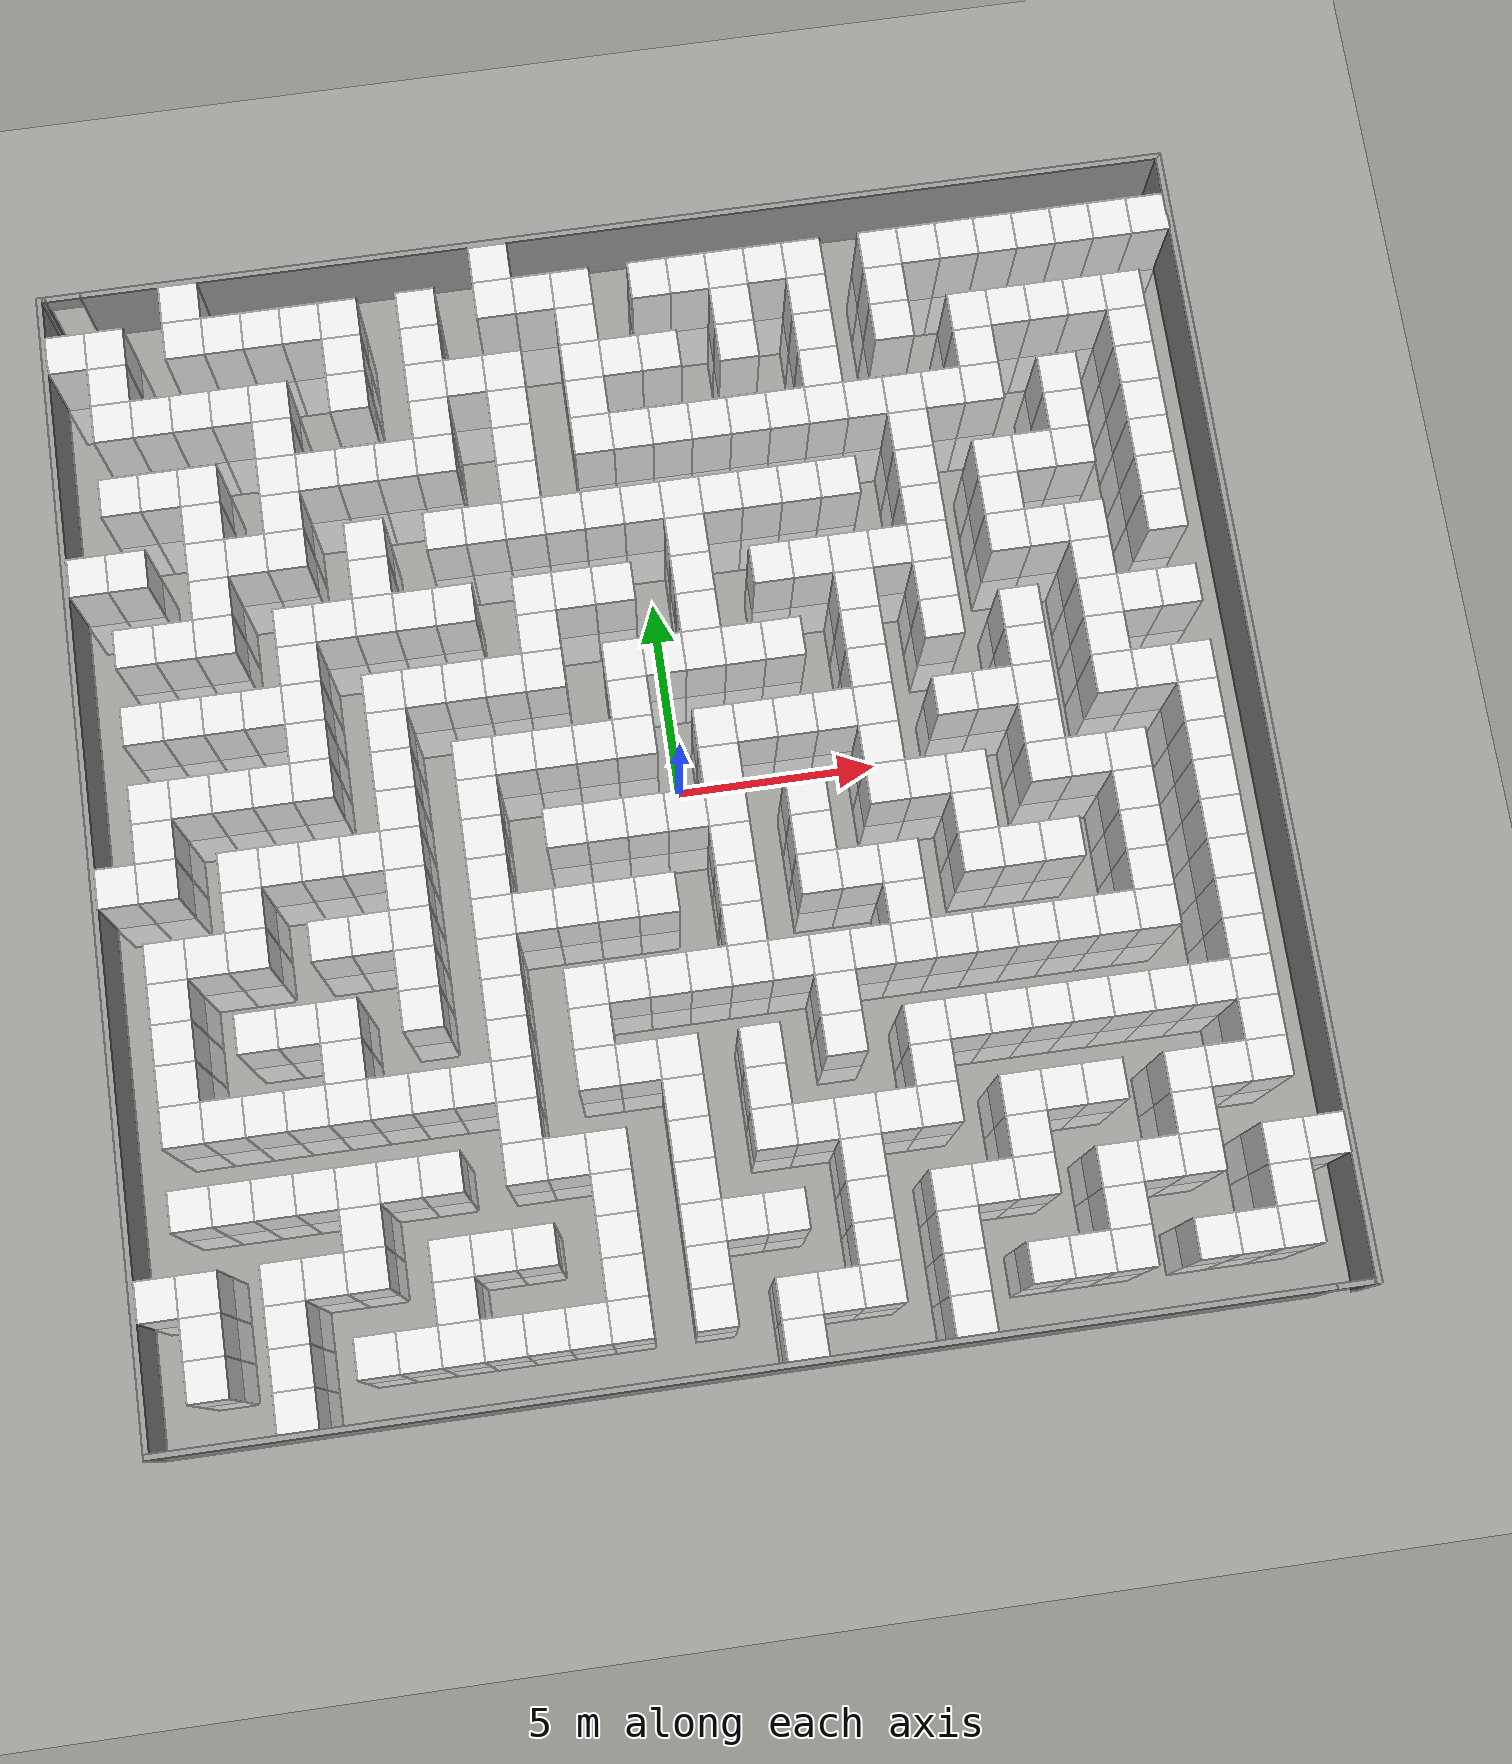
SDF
<sdf version="1.6">
 <world name="default">
  <light name="sun" type="directional">
   <pose>0 0 10 0 -0 0</pose>
   <diffuse>0.8 0.8 0.8 1</diffuse>
   <specular>0.1 0.1 0.1 1</specular>
   <attenuation>
    <range>1000</range>
    <constant>0.9</constant>
    <linear>0.01</linear>
    <quadratic>0.001</quadratic>
   </attenuation>
   <direction>-0.5 0.5 -1</direction>
  </light>
  <model name="ground_plane">
   <static>1</static>
   <link name="link">
    <collision name="collision">
     <geometry><plane><normal>0 0 1</normal><size>100 100</size></plane></geometry>
     <surface><friction><ode><mu>100</mu><mu2>50</mu2></ode></friction></surface>
    </collision>
    <visual name="visual">
     <cast_shadows>0</cast_shadows>
     <geometry><plane><normal>0 0 1</normal><size>100 100</size></plane></geometry>
     <material>
      <script><uri>file://media/materials/scripts/gazebo.material</uri><name>Gazebo/Grey</name></script>
     </material>
    </visual>
   </link>
  </model>
  <gravity>0 0 -9.8</gravity>
  <magnetic_field>6e-06 2.3e-05 -4.2e-05</magnetic_field>
  <atmosphere type="adiabatic"/>
  <physics name="default_physics" default="0" type="ode">
   <max_step_size>0.001</max_step_size>
   <real_time_factor>1</real_time_factor>
   <real_time_update_rate>1000</real_time_update_rate>
  </physics>
  <scene><ambient>0.4 0.4 0.4 1</ambient><background>0.7 0.7 0.7 1</background><shadows>1</shadows></scene>
  <spherical_coordinates>
   <surface_model>EARTH_WGS84</surface_model>
   <latitude_deg>0</latitude_deg>
   <longitude_deg>0</longitude_deg>
   <elevation>0</elevation>
   <heading_deg>0</heading_deg>
  </spherical_coordinates>
  <model name="Unit_box_-11_14">
   <pose>-11 14 0 0 0 0</pose>
   <link name="Unit_box_-11_14_collision">
    <collision name="collision"><geometry><box><size>1 1 5</size></box></geometry></collision>
    <visual name="Unit_box_-11_14_visual">
     <geometry><box><size>1 1 5</size></box></geometry>
     <material>
      <script><name>Gazebo/White</name><uri>file://media/materials/scripts/gazebo.material</uri></script>
     </material>
    </visual>
   </link>
   <static>1</static>
  </model>
  <model name="Unit_box_-3_14">
   <pose>-3 14 0 0 0 0</pose>
   <link name="Unit_box_-3_14_collision">
    <collision name="collision"><geometry><box><size>1 1 5</size></box></geometry></collision>
    <visual name="Unit_box_-3_14_visual">
     <geometry><box><size>1 1 5</size></box></geometry>
     <material>
      <script><name>Gazebo/White</name><uri>file://media/materials/scripts/gazebo.material</uri></script>
     </material>
    </visual>
   </link>
   <static>1</static>
  </model>
  <model name="Unit_box_-14_13">
   <pose>-14 13 0 0 0 0</pose>
   <link name="Unit_box_-14_13_collision">
    <collision name="collision"><geometry><box><size>1 1 5</size></box></geometry></collision>
    <visual name="Unit_box_-14_13_visual">
     <geometry><box><size>1 1 5</size></box></geometry>
     <material>
      <script><name>Gazebo/White</name><uri>file://media/materials/scripts/gazebo.material</uri></script>
     </material>
    </visual>
   </link>
   <static>1</static>
  </model>
  <model name="Unit_box_-13_13">
   <pose>-13 13 0 0 0 0</pose>
   <link name="Unit_box_-13_13_collision">
    <collision name="collision"><geometry><box><size>1 1 5</size></box></geometry></collision>
    <visual name="Unit_box_-13_13_visual">
     <geometry><box><size>1 1 5</size></box></geometry>
     <material>
      <script><name>Gazebo/White</name><uri>file://media/materials/scripts/gazebo.material</uri></script>
     </material>
    </visual>
   </link>
   <static>1</static>
  </model>
  <model name="Unit_box_-11_13">
   <pose>-11 13 0 0 0 0</pose>
   <link name="Unit_box_-11_13_collision">
    <collision name="collision"><geometry><box><size>1 1 5</size></box></geometry></collision>
    <visual name="Unit_box_-11_13_visual">
     <geometry><box><size>1 1 5</size></box></geometry>
     <material>
      <script><name>Gazebo/White</name><uri>file://media/materials/scripts/gazebo.material</uri></script>
     </material>
    </visual>
   </link>
   <static>1</static>
  </model>
  <model name="Unit_box_-10_13">
   <pose>-10 13 0 0 0 0</pose>
   <link name="Unit_box_-10_13_collision">
    <collision name="collision"><geometry><box><size>1 1 5</size></box></geometry></collision>
    <visual name="Unit_box_-10_13_visual">
     <geometry><box><size>1 1 5</size></box></geometry>
     <material>
      <script><name>Gazebo/White</name><uri>file://media/materials/scripts/gazebo.material</uri></script>
     </material>
    </visual>
   </link>
   <static>1</static>
  </model>
  <model name="Unit_box_-9_13">
   <pose>-9 13 0 0 0 0</pose>
   <link name="Unit_box_-9_13_collision">
    <collision name="collision"><geometry><box><size>1 1 5</size></box></geometry></collision>
    <visual name="Unit_box_-9_13_visual">
     <geometry><box><size>1 1 5</size></box></geometry>
     <material>
      <script><name>Gazebo/White</name><uri>file://media/materials/scripts/gazebo.material</uri></script>
     </material>
    </visual>
   </link>
   <static>1</static>
  </model>
  <model name="Unit_box_-8_13">
   <pose>-8 13 0 0 0 0</pose>
   <link name="Unit_box_-8_13_collision">
    <collision name="collision"><geometry><box><size>1 1 5</size></box></geometry></collision>
    <visual name="Unit_box_-8_13_visual">
     <geometry><box><size>1 1 5</size></box></geometry>
     <material>
      <script><name>Gazebo/White</name><uri>file://media/materials/scripts/gazebo.material</uri></script>
     </material>
    </visual>
   </link>
   <static>1</static>
  </model>
  <model name="Unit_box_-7_13">
   <pose>-7 13 0 0 0 0</pose>
   <link name="Unit_box_-7_13_collision">
    <collision name="collision"><geometry><box><size>1 1 5</size></box></geometry></collision>
    <visual name="Unit_box_-7_13_visual">
     <geometry><box><size>1 1 5</size></box></geometry>
     <material>
      <script><name>Gazebo/White</name><uri>file://media/materials/scripts/gazebo.material</uri></script>
     </material>
    </visual>
   </link>
   <static>1</static>
  </model>
  <model name="Unit_box_-5_13">
   <pose>-5 13 0 0 0 0</pose>
   <link name="Unit_box_-5_13_collision">
    <collision name="collision"><geometry><box><size>1 1 5</size></box></geometry></collision>
    <visual name="Unit_box_-5_13_visual">
     <geometry><box><size>1 1 5</size></box></geometry>
     <material>
      <script><name>Gazebo/White</name><uri>file://media/materials/scripts/gazebo.material</uri></script>
     </material>
    </visual>
   </link>
   <static>1</static>
  </model>
  <model name="Unit_box_-3_13">
   <pose>-3 13 0 0 0 0</pose>
   <link name="Unit_box_-3_13_collision">
    <collision name="collision"><geometry><box><size>1 1 5</size></box></geometry></collision>
    <visual name="Unit_box_-3_13_visual">
     <geometry><box><size>1 1 5</size></box></geometry>
     <material>
      <script><name>Gazebo/White</name><uri>file://media/materials/scripts/gazebo.material</uri></script>
     </material>
    </visual>
   </link>
   <static>1</static>
  </model>
  <model name="Unit_box_-2_13">
   <pose>-2 13 0 0 0 0</pose>
   <link name="Unit_box_-2_13_collision">
    <collision name="collision"><geometry><box><size>1 1 5</size></box></geometry></collision>
    <visual name="Unit_box_-2_13_visual">
     <geometry><box><size>1 1 5</size></box></geometry>
     <material>
      <script><name>Gazebo/White</name><uri>file://media/materials/scripts/gazebo.material</uri></script>
     </material>
    </visual>
   </link>
   <static>1</static>
  </model>
  <model name="Unit_box_-1_13">
   <pose>-1 13 0 0 0 0</pose>
   <link name="Unit_box_-1_13_collision">
    <collision name="collision"><geometry><box><size>1 1 5</size></box></geometry></collision>
    <visual name="Unit_box_-1_13_visual">
     <geometry><box><size>1 1 5</size></box></geometry>
     <material>
      <script><name>Gazebo/White</name><uri>file://media/materials/scripts/gazebo.material</uri></script>
     </material>
    </visual>
   </link>
   <static>1</static>
  </model>
  <model name="Unit_box_1_13">
   <pose>1 13 0 0 0 0</pose>
   <link name="Unit_box_1_13_collision">
    <collision name="collision"><geometry><box><size>1 1 5</size></box></geometry></collision>
    <visual name="Unit_box_1_13_visual">
     <geometry><box><size>1 1 5</size></box></geometry>
     <material>
      <script><name>Gazebo/White</name><uri>file://media/materials/scripts/gazebo.material</uri></script>
     </material>
    </visual>
   </link>
   <static>1</static>
  </model>
  <model name="Unit_box_2_13">
   <pose>2 13 0 0 0 0</pose>
   <link name="Unit_box_2_13_collision">
    <collision name="collision"><geometry><box><size>1 1 5</size></box></geometry></collision>
    <visual name="Unit_box_2_13_visual">
     <geometry><box><size>1 1 5</size></box></geometry>
     <material>
      <script><name>Gazebo/White</name><uri>file://media/materials/scripts/gazebo.material</uri></script>
     </material>
    </visual>
   </link>
   <static>1</static>
  </model>
  <model name="Unit_box_3_13">
   <pose>3 13 0 0 0 0</pose>
   <link name="Unit_box_3_13_collision">
    <collision name="collision"><geometry><box><size>1 1 5</size></box></geometry></collision>
    <visual name="Unit_box_3_13_visual">
     <geometry><box><size>1 1 5</size></box></geometry>
     <material>
      <script><name>Gazebo/White</name><uri>file://media/materials/scripts/gazebo.material</uri></script>
     </material>
    </visual>
   </link>
   <static>1</static>
  </model>
  <model name="Unit_box_4_13">
   <pose>4 13 0 0 0 0</pose>
   <link name="Unit_box_4_13_collision">
    <collision name="collision"><geometry><box><size>1 1 5</size></box></geometry></collision>
    <visual name="Unit_box_4_13_visual">
     <geometry><box><size>1 1 5</size></box></geometry>
     <material>
      <script><name>Gazebo/White</name><uri>file://media/materials/scripts/gazebo.material</uri></script>
     </material>
    </visual>
   </link>
   <static>1</static>
  </model>
  <model name="Unit_box_5_13">
   <pose>5 13 0 0 0 0</pose>
   <link name="Unit_box_5_13_collision">
    <collision name="collision"><geometry><box><size>1 1 5</size></box></geometry></collision>
    <visual name="Unit_box_5_13_visual">
     <geometry><box><size>1 1 5</size></box></geometry>
     <material>
      <script><name>Gazebo/White</name><uri>file://media/materials/scripts/gazebo.material</uri></script>
     </material>
    </visual>
   </link>
   <static>1</static>
  </model>
  <model name="Unit_box_7_13">
   <pose>7 13 0 0 0 0</pose>
   <link name="Unit_box_7_13_collision">
    <collision name="collision"><geometry><box><size>1 1 5</size></box></geometry></collision>
    <visual name="Unit_box_7_13_visual">
     <geometry><box><size>1 1 5</size></box></geometry>
     <material>
      <script><name>Gazebo/White</name><uri>file://media/materials/scripts/gazebo.material</uri></script>
     </material>
    </visual>
   </link>
   <static>1</static>
  </model>
  <model name="Unit_box_8_13">
   <pose>8 13 0 0 0 0</pose>
   <link name="Unit_box_8_13_collision">
    <collision name="collision"><geometry><box><size>1 1 5</size></box></geometry></collision>
    <visual name="Unit_box_8_13_visual">
     <geometry><box><size>1 1 5</size></box></geometry>
     <material>
      <script><name>Gazebo/White</name><uri>file://media/materials/scripts/gazebo.material</uri></script>
     </material>
    </visual>
   </link>
   <static>1</static>
  </model>
  <model name="Unit_box_9_13">
   <pose>9 13 0 0 0 0</pose>
   <link name="Unit_box_9_13_collision">
    <collision name="collision"><geometry><box><size>1 1 5</size></box></geometry></collision>
    <visual name="Unit_box_9_13_visual">
     <geometry><box><size>1 1 5</size></box></geometry>
     <material>
      <script><name>Gazebo/White</name><uri>file://media/materials/scripts/gazebo.material</uri></script>
     </material>
    </visual>
   </link>
   <static>1</static>
  </model>
  <model name="Unit_box_10_13">
   <pose>10 13 0 0 0 0</pose>
   <link name="Unit_box_10_13_collision">
    <collision name="collision"><geometry><box><size>1 1 5</size></box></geometry></collision>
    <visual name="Unit_box_10_13_visual">
     <geometry><box><size>1 1 5</size></box></geometry>
     <material>
      <script><name>Gazebo/White</name><uri>file://media/materials/scripts/gazebo.material</uri></script>
     </material>
    </visual>
   </link>
   <static>1</static>
  </model>
  <model name="Unit_box_11_13">
   <pose>11 13 0 0 0 0</pose>
   <link name="Unit_box_11_13_collision">
    <collision name="collision"><geometry><box><size>1 1 5</size></box></geometry></collision>
    <visual name="Unit_box_11_13_visual">
     <geometry><box><size>1 1 5</size></box></geometry>
     <material>
      <script><name>Gazebo/White</name><uri>file://media/materials/scripts/gazebo.material</uri></script>
     </material>
    </visual>
   </link>
   <static>1</static>
  </model>
  <model name="Unit_box_12_13">
   <pose>12 13 0 0 0 0</pose>
   <link name="Unit_box_12_13_collision">
    <collision name="collision"><geometry><box><size>1 1 5</size></box></geometry></collision>
    <visual name="Unit_box_12_13_visual">
     <geometry><box><size>1 1 5</size></box></geometry>
     <material>
      <script><name>Gazebo/White</name><uri>file://media/materials/scripts/gazebo.material</uri></script>
     </material>
    </visual>
   </link>
   <static>1</static>
  </model>
  <model name="Unit_box_13_13">
   <pose>13 13 0 0 0 0</pose>
   <link name="Unit_box_13_13_collision">
    <collision name="collision"><geometry><box><size>1 1 5</size></box></geometry></collision>
    <visual name="Unit_box_13_13_visual">
     <geometry><box><size>1 1 5</size></box></geometry>
     <material>
      <script><name>Gazebo/White</name><uri>file://media/materials/scripts/gazebo.material</uri></script>
     </material>
    </visual>
   </link>
   <static>1</static>
  </model>
  <model name="Unit_box_14_13">
   <pose>14 13 0 0 0 0</pose>
   <link name="Unit_box_14_13_collision">
    <collision name="collision"><geometry><box><size>1 1 5</size></box></geometry></collision>
    <visual name="Unit_box_14_13_visual">
     <geometry><box><size>1 1 5</size></box></geometry>
     <material>
      <script><name>Gazebo/White</name><uri>file://media/materials/scripts/gazebo.material</uri></script>
     </material>
    </visual>
   </link>
   <static>1</static>
  </model>
  <model name="Unit_box_-13_12">
   <pose>-13 12 0 0 0 0</pose>
   <link name="Unit_box_-13_12_collision">
    <collision name="collision"><geometry><box><size>1 1 5</size></box></geometry></collision>
    <visual name="Unit_box_-13_12_visual">
     <geometry><box><size>1 1 5</size></box></geometry>
     <material>
      <script><name>Gazebo/White</name><uri>file://media/materials/scripts/gazebo.material</uri></script>
     </material>
    </visual>
   </link>
   <static>1</static>
  </model>
  <model name="Unit_box_-7_12">
   <pose>-7 12 0 0 0 0</pose>
   <link name="Unit_box_-7_12_collision">
    <collision name="collision"><geometry><box><size>1 1 5</size></box></geometry></collision>
    <visual name="Unit_box_-7_12_visual">
     <geometry><box><size>1 1 5</size></box></geometry>
     <material>
      <script><name>Gazebo/White</name><uri>file://media/materials/scripts/gazebo.material</uri></script>
     </material>
    </visual>
   </link>
   <static>1</static>
  </model>
  <model name="Unit_box_-5_12">
   <pose>-5 12 0 0 0 0</pose>
   <link name="Unit_box_-5_12_collision">
    <collision name="collision"><geometry><box><size>1 1 5</size></box></geometry></collision>
    <visual name="Unit_box_-5_12_visual">
     <geometry><box><size>1 1 5</size></box></geometry>
     <material>
      <script><name>Gazebo/White</name><uri>file://media/materials/scripts/gazebo.material</uri></script>
     </material>
    </visual>
   </link>
   <static>1</static>
  </model>
  <model name="Unit_box_-1_12">
   <pose>-1 12 0 0 0 0</pose>
   <link name="Unit_box_-1_12_collision">
    <collision name="collision"><geometry><box><size>1 1 5</size></box></geometry></collision>
    <visual name="Unit_box_-1_12_visual">
     <geometry><box><size>1 1 5</size></box></geometry>
     <material>
      <script><name>Gazebo/White</name><uri>file://media/materials/scripts/gazebo.material</uri></script>
     </material>
    </visual>
   </link>
   <static>1</static>
  </model>
  <model name="Unit_box_3_12">
   <pose>3 12 0 0 0 0</pose>
   <link name="Unit_box_3_12_collision">
    <collision name="collision"><geometry><box><size>1 1 5</size></box></geometry></collision>
    <visual name="Unit_box_3_12_visual">
     <geometry><box><size>1 1 5</size></box></geometry>
     <material>
      <script><name>Gazebo/White</name><uri>file://media/materials/scripts/gazebo.material</uri></script>
     </material>
    </visual>
   </link>
   <static>1</static>
  </model>
  <model name="Unit_box_5_12">
   <pose>5 12 0 0 0 0</pose>
   <link name="Unit_box_5_12_collision">
    <collision name="collision"><geometry><box><size>1 1 5</size></box></geometry></collision>
    <visual name="Unit_box_5_12_visual">
     <geometry><box><size>1 1 5</size></box></geometry>
     <material>
      <script><name>Gazebo/White</name><uri>file://media/materials/scripts/gazebo.material</uri></script>
     </material>
    </visual>
   </link>
   <static>1</static>
  </model>
  <model name="Unit_box_7_12">
   <pose>7 12 0 0 0 0</pose>
   <link name="Unit_box_7_12_collision">
    <collision name="collision"><geometry><box><size>1 1 5</size></box></geometry></collision>
    <visual name="Unit_box_7_12_visual">
     <geometry><box><size>1 1 5</size></box></geometry>
     <material>
      <script><name>Gazebo/White</name><uri>file://media/materials/scripts/gazebo.material</uri></script>
     </material>
    </visual>
   </link>
   <static>1</static>
  </model>
  <model name="Unit_box_-13_11">
   <pose>-13 11 0 0 0 0</pose>
   <link name="Unit_box_-13_11_collision">
    <collision name="collision"><geometry><box><size>1 1 5</size></box></geometry></collision>
    <visual name="Unit_box_-13_11_visual">
     <geometry><box><size>1 1 5</size></box></geometry>
     <material>
      <script><name>Gazebo/White</name><uri>file://media/materials/scripts/gazebo.material</uri></script>
     </material>
    </visual>
   </link>
   <static>1</static>
  </model>
  <model name="Unit_box_-12_11">
   <pose>-12 11 0 0 0 0</pose>
   <link name="Unit_box_-12_11_collision">
    <collision name="collision"><geometry><box><size>1 1 5</size></box></geometry></collision>
    <visual name="Unit_box_-12_11_visual">
     <geometry><box><size>1 1 5</size></box></geometry>
     <material>
      <script><name>Gazebo/White</name><uri>file://media/materials/scripts/gazebo.material</uri></script>
     </material>
    </visual>
   </link>
   <static>1</static>
  </model>
  <model name="Unit_box_-11_11">
   <pose>-11 11 0 0 0 0</pose>
   <link name="Unit_box_-11_11_collision">
    <collision name="collision"><geometry><box><size>1 1 5</size></box></geometry></collision>
    <visual name="Unit_box_-11_11_visual">
     <geometry><box><size>1 1 5</size></box></geometry>
     <material>
      <script><name>Gazebo/White</name><uri>file://media/materials/scripts/gazebo.material</uri></script>
     </material>
    </visual>
   </link>
   <static>1</static>
  </model>
  <model name="Unit_box_-10_11">
   <pose>-10 11 0 0 0 0</pose>
   <link name="Unit_box_-10_11_collision">
    <collision name="collision"><geometry><box><size>1 1 5</size></box></geometry></collision>
    <visual name="Unit_box_-10_11_visual">
     <geometry><box><size>1 1 5</size></box></geometry>
     <material>
      <script><name>Gazebo/White</name><uri>file://media/materials/scripts/gazebo.material</uri></script>
     </material>
    </visual>
   </link>
   <static>1</static>
  </model>
  <model name="Unit_box_-9_11">
   <pose>-9 11 0 0 0 0</pose>
   <link name="Unit_box_-9_11_collision">
    <collision name="collision"><geometry><box><size>1 1 5</size></box></geometry></collision>
    <visual name="Unit_box_-9_11_visual">
     <geometry><box><size>1 1 5</size></box></geometry>
     <material>
      <script><name>Gazebo/White</name><uri>file://media/materials/scripts/gazebo.material</uri></script>
     </material>
    </visual>
   </link>
   <static>1</static>
  </model>
  <model name="Unit_box_-7_11">
   <pose>-7 11 0 0 0 0</pose>
   <link name="Unit_box_-7_11_collision">
    <collision name="collision"><geometry><box><size>1 1 5</size></box></geometry></collision>
    <visual name="Unit_box_-7_11_visual">
     <geometry><box><size>1 1 5</size></box></geometry>
     <material>
      <script><name>Gazebo/White</name><uri>file://media/materials/scripts/gazebo.material</uri></script>
     </material>
    </visual>
   </link>
   <static>1</static>
  </model>
  <model name="Unit_box_-5_11">
   <pose>-5 11 0 0 0 0</pose>
   <link name="Unit_box_-5_11_collision">
    <collision name="collision"><geometry><box><size>1 1 5</size></box></geometry></collision>
    <visual name="Unit_box_-5_11_visual">
     <geometry><box><size>1 1 5</size></box></geometry>
     <material>
      <script><name>Gazebo/White</name><uri>file://media/materials/scripts/gazebo.material</uri></script>
     </material>
    </visual>
   </link>
   <static>1</static>
  </model>
  <model name="Unit_box_-4_11">
   <pose>-4 11 0 0 0 0</pose>
   <link name="Unit_box_-4_11_collision">
    <collision name="collision"><geometry><box><size>1 1 5</size></box></geometry></collision>
    <visual name="Unit_box_-4_11_visual">
     <geometry><box><size>1 1 5</size></box></geometry>
     <material>
      <script><name>Gazebo/White</name><uri>file://media/materials/scripts/gazebo.material</uri></script>
     </material>
    </visual>
   </link>
   <static>1</static>
  </model>
  <model name="Unit_box_-3_11">
   <pose>-3 11 0 0 0 0</pose>
   <link name="Unit_box_-3_11_collision">
    <collision name="collision"><geometry><box><size>1 1 5</size></box></geometry></collision>
    <visual name="Unit_box_-3_11_visual">
     <geometry><box><size>1 1 5</size></box></geometry>
     <material>
      <script><name>Gazebo/White</name><uri>file://media/materials/scripts/gazebo.material</uri></script>
     </material>
    </visual>
   </link>
   <static>1</static>
  </model>
  <model name="Unit_box_-1_11">
   <pose>-1 11 0 0 0 0</pose>
   <link name="Unit_box_-1_11_collision">
    <collision name="collision"><geometry><box><size>1 1 5</size></box></geometry></collision>
    <visual name="Unit_box_-1_11_visual">
     <geometry><box><size>1 1 5</size></box></geometry>
     <material>
      <script><name>Gazebo/White</name><uri>file://media/materials/scripts/gazebo.material</uri></script>
     </material>
    </visual>
   </link>
   <static>1</static>
  </model>
  <model name="Unit_box_0_11">
   <pose>0 11 0 0 0 0</pose>
   <link name="Unit_box_0_11_collision">
    <collision name="collision"><geometry><box><size>1 1 5</size></box></geometry></collision>
    <visual name="Unit_box_0_11_visual">
     <geometry><box><size>1 1 5</size></box></geometry>
     <material>
      <script><name>Gazebo/White</name><uri>file://media/materials/scripts/gazebo.material</uri></script>
     </material>
    </visual>
   </link>
   <static>1</static>
  </model>
  <model name="Unit_box_1_11">
   <pose>1 11 0 0 0 0</pose>
   <link name="Unit_box_1_11_collision">
    <collision name="collision"><geometry><box><size>1 1 5</size></box></geometry></collision>
    <visual name="Unit_box_1_11_visual">
     <geometry><box><size>1 1 5</size></box></geometry>
     <material>
      <script><name>Gazebo/White</name><uri>file://media/materials/scripts/gazebo.material</uri></script>
     </material>
    </visual>
   </link>
   <static>1</static>
  </model>
  <model name="Unit_box_3_11">
   <pose>3 11 0 0 0 0</pose>
   <link name="Unit_box_3_11_collision">
    <collision name="collision"><geometry><box><size>1 1 5</size></box></geometry></collision>
    <visual name="Unit_box_3_11_visual">
     <geometry><box><size>1 1 5</size></box></geometry>
     <material>
      <script><name>Gazebo/White</name><uri>file://media/materials/scripts/gazebo.material</uri></script>
     </material>
    </visual>
   </link>
   <static>1</static>
  </model>
  <model name="Unit_box_5_11">
   <pose>5 11 0 0 0 0</pose>
   <link name="Unit_box_5_11_collision">
    <collision name="collision"><geometry><box><size>1 1 5</size></box></geometry></collision>
    <visual name="Unit_box_5_11_visual">
     <geometry><box><size>1 1 5</size></box></geometry>
     <material>
      <script><name>Gazebo/White</name><uri>file://media/materials/scripts/gazebo.material</uri></script>
     </material>
    </visual>
   </link>
   <static>1</static>
  </model>
  <model name="Unit_box_7_11">
   <pose>7 11 0 0 0 0</pose>
   <link name="Unit_box_7_11_collision">
    <collision name="collision"><geometry><box><size>1 1 5</size></box></geometry></collision>
    <visual name="Unit_box_7_11_visual">
     <geometry><box><size>1 1 5</size></box></geometry>
     <material>
      <script><name>Gazebo/White</name><uri>file://media/materials/scripts/gazebo.material</uri></script>
     </material>
    </visual>
   </link>
   <static>1</static>
  </model>
  <model name="Unit_box_9_11">
   <pose>9 11 0 0 0 0</pose>
   <link name="Unit_box_9_11_collision">
    <collision name="collision"><geometry><box><size>1 1 5</size></box></geometry></collision>
    <visual name="Unit_box_9_11_visual">
     <geometry><box><size>1 1 5</size></box></geometry>
     <material>
      <script><name>Gazebo/White</name><uri>file://media/materials/scripts/gazebo.material</uri></script>
     </material>
    </visual>
   </link>
   <static>1</static>
  </model>
  <model name="Unit_box_10_11">
   <pose>10 11 0 0 0 0</pose>
   <link name="Unit_box_10_11_collision">
    <collision name="collision"><geometry><box><size>1 1 5</size></box></geometry></collision>
    <visual name="Unit_box_10_11_visual">
     <geometry><box><size>1 1 5</size></box></geometry>
     <material>
      <script><name>Gazebo/White</name><uri>file://media/materials/scripts/gazebo.material</uri></script>
     </material>
    </visual>
   </link>
   <static>1</static>
  </model>
  <model name="Unit_box_11_11">
   <pose>11 11 0 0 0 0</pose>
   <link name="Unit_box_11_11_collision">
    <collision name="collision"><geometry><box><size>1 1 5</size></box></geometry></collision>
    <visual name="Unit_box_11_11_visual">
     <geometry><box><size>1 1 5</size></box></geometry>
     <material>
      <script><name>Gazebo/White</name><uri>file://media/materials/scripts/gazebo.material</uri></script>
     </material>
    </visual>
   </link>
   <static>1</static>
  </model>
  <model name="Unit_box_12_11">
   <pose>12 11 0 0 0 0</pose>
   <link name="Unit_box_12_11_collision">
    <collision name="collision"><geometry><box><size>1 1 5</size></box></geometry></collision>
    <visual name="Unit_box_12_11_visual">
     <geometry><box><size>1 1 5</size></box></geometry>
     <material>
      <script><name>Gazebo/White</name><uri>file://media/materials/scripts/gazebo.material</uri></script>
     </material>
    </visual>
   </link>
   <static>1</static>
  </model>
  <model name="Unit_box_13_11">
   <pose>13 11 0 0 0 0</pose>
   <link name="Unit_box_13_11_collision">
    <collision name="collision"><geometry><box><size>1 1 5</size></box></geometry></collision>
    <visual name="Unit_box_13_11_visual">
     <geometry><box><size>1 1 5</size></box></geometry>
     <material>
      <script><name>Gazebo/White</name><uri>file://media/materials/scripts/gazebo.material</uri></script>
     </material>
    </visual>
   </link>
   <static>1</static>
  </model>
  <model name="Unit_box_-9_10">
   <pose>-9 10 0 0 0 0</pose>
   <link name="Unit_box_-9_10_collision">
    <collision name="collision"><geometry><box><size>1 1 5</size></box></geometry></collision>
    <visual name="Unit_box_-9_10_visual">
     <geometry><box><size>1 1 5</size></box></geometry>
     <material>
      <script><name>Gazebo/White</name><uri>file://media/materials/scripts/gazebo.material</uri></script>
     </material>
    </visual>
   </link>
   <static>1</static>
  </model>
  <model name="Unit_box_-5_10">
   <pose>-5 10 0 0 0 0</pose>
   <link name="Unit_box_-5_10_collision">
    <collision name="collision"><geometry><box><size>1 1 5</size></box></geometry></collision>
    <visual name="Unit_box_-5_10_visual">
     <geometry><box><size>1 1 5</size></box></geometry>
     <material>
      <script><name>Gazebo/White</name><uri>file://media/materials/scripts/gazebo.material</uri></script>
     </material>
    </visual>
   </link>
   <static>1</static>
  </model>
  <model name="Unit_box_-3_10">
   <pose>-3 10 0 0 0 0</pose>
   <link name="Unit_box_-3_10_collision">
    <collision name="collision"><geometry><box><size>1 1 5</size></box></geometry></collision>
    <visual name="Unit_box_-3_10_visual">
     <geometry><box><size>1 1 5</size></box></geometry>
     <material>
      <script><name>Gazebo/White</name><uri>file://media/materials/scripts/gazebo.material</uri></script>
     </material>
    </visual>
   </link>
   <static>1</static>
  </model>
  <model name="Unit_box_-1_10">
   <pose>-1 10 0 0 0 0</pose>
   <link name="Unit_box_-1_10_collision">
    <collision name="collision"><geometry><box><size>1 1 5</size></box></geometry></collision>
    <visual name="Unit_box_-1_10_visual">
     <geometry><box><size>1 1 5</size></box></geometry>
     <material>
      <script><name>Gazebo/White</name><uri>file://media/materials/scripts/gazebo.material</uri></script>
     </material>
    </visual>
   </link>
   <static>1</static>
  </model>
  <model name="Unit_box_5_10">
   <pose>5 10 0 0 0 0</pose>
   <link name="Unit_box_5_10_collision">
    <collision name="collision"><geometry><box><size>1 1 5</size></box></geometry></collision>
    <visual name="Unit_box_5_10_visual">
     <geometry><box><size>1 1 5</size></box></geometry>
     <material>
      <script><name>Gazebo/White</name><uri>file://media/materials/scripts/gazebo.material</uri></script>
     </material>
    </visual>
   </link>
   <static>1</static>
  </model>
  <model name="Unit_box_9_10">
   <pose>9 10 0 0 0 0</pose>
   <link name="Unit_box_9_10_collision">
    <collision name="collision"><geometry><box><size>1 1 5</size></box></geometry></collision>
    <visual name="Unit_box_9_10_visual">
     <geometry><box><size>1 1 5</size></box></geometry>
     <material>
      <script><name>Gazebo/White</name><uri>file://media/materials/scripts/gazebo.material</uri></script>
     </material>
    </visual>
   </link>
   <static>1</static>
  </model>
  <model name="Unit_box_13_10">
   <pose>13 10 0 0 0 0</pose>
   <link name="Unit_box_13_10_collision">
    <collision name="collision"><geometry><box><size>1 1 5</size></box></geometry></collision>
    <visual name="Unit_box_13_10_visual">
     <geometry><box><size>1 1 5</size></box></geometry>
     <material>
      <script><name>Gazebo/White</name><uri>file://media/materials/scripts/gazebo.material</uri></script>
     </material>
    </visual>
   </link>
   <static>1</static>
  </model>
  <model name="Unit_box_-13_9">
   <pose>-13 9 0 0 0 0</pose>
   <link name="Unit_box_-13_9_collision">
    <collision name="collision"><geometry><box><size>1 1 5</size></box></geometry></collision>
    <visual name="Unit_box_-13_9_visual">
     <geometry><box><size>1 1 5</size></box></geometry>
     <material>
      <script><name>Gazebo/White</name><uri>file://media/materials/scripts/gazebo.material</uri></script>
     </material>
    </visual>
   </link>
   <static>1</static>
  </model>
  <model name="Unit_box_-12_9">
   <pose>-12 9 0 0 0 0</pose>
   <link name="Unit_box_-12_9_collision">
    <collision name="collision"><geometry><box><size>1 1 5</size></box></geometry></collision>
    <visual name="Unit_box_-12_9_visual">
     <geometry><box><size>1 1 5</size></box></geometry>
     <material>
      <script><name>Gazebo/White</name><uri>file://media/materials/scripts/gazebo.material</uri></script>
     </material>
    </visual>
   </link>
   <static>1</static>
  </model>
  <model name="Unit_box_-11_9">
   <pose>-11 9 0 0 0 0</pose>
   <link name="Unit_box_-11_9_collision">
    <collision name="collision"><geometry><box><size>1 1 5</size></box></geometry></collision>
    <visual name="Unit_box_-11_9_visual">
     <geometry><box><size>1 1 5</size></box></geometry>
     <material>
      <script><name>Gazebo/White</name><uri>file://media/materials/scripts/gazebo.material</uri></script>
     </material>
    </visual>
   </link>
   <static>1</static>
  </model>
  <model name="Unit_box_-9_9">
   <pose>-9 9 0 0 0 0</pose>
   <link name="Unit_box_-9_9_collision">
    <collision name="collision"><geometry><box><size>1 1 5</size></box></geometry></collision>
    <visual name="Unit_box_-9_9_visual">
     <geometry><box><size>1 1 5</size></box></geometry>
     <material>
      <script><name>Gazebo/White</name><uri>file://media/materials/scripts/gazebo.material</uri></script>
     </material>
    </visual>
   </link>
   <static>1</static>
  </model>
  <model name="Unit_box_-8_9">
   <pose>-8 9 0 0 0 0</pose>
   <link name="Unit_box_-8_9_collision">
    <collision name="collision"><geometry><box><size>1 1 5</size></box></geometry></collision>
    <visual name="Unit_box_-8_9_visual">
     <geometry><box><size>1 1 5</size></box></geometry>
     <material>
      <script><name>Gazebo/White</name><uri>file://media/materials/scripts/gazebo.material</uri></script>
     </material>
    </visual>
   </link>
   <static>1</static>
  </model>
  <model name="Unit_box_-7_9">
   <pose>-7 9 0 0 0 0</pose>
   <link name="Unit_box_-7_9_collision">
    <collision name="collision"><geometry><box><size>1 1 5</size></box></geometry></collision>
    <visual name="Unit_box_-7_9_visual">
     <geometry><box><size>1 1 5</size></box></geometry>
     <material>
      <script><name>Gazebo/White</name><uri>file://media/materials/scripts/gazebo.material</uri></script>
     </material>
    </visual>
   </link>
   <static>1</static>
  </model>
  <model name="Unit_box_-6_9">
   <pose>-6 9 0 0 0 0</pose>
   <link name="Unit_box_-6_9_collision">
    <collision name="collision"><geometry><box><size>1 1 5</size></box></geometry></collision>
    <visual name="Unit_box_-6_9_visual">
     <geometry><box><size>1 1 5</size></box></geometry>
     <material>
      <script><name>Gazebo/White</name><uri>file://media/materials/scripts/gazebo.material</uri></script>
     </material>
    </visual>
   </link>
   <static>1</static>
  </model>
  <model name="Unit_box_-5_9">
   <pose>-5 9 0 0 0 0</pose>
   <link name="Unit_box_-5_9_collision">
    <collision name="collision"><geometry><box><size>1 1 5</size></box></geometry></collision>
    <visual name="Unit_box_-5_9_visual">
     <geometry><box><size>1 1 5</size></box></geometry>
     <material>
      <script><name>Gazebo/White</name><uri>file://media/materials/scripts/gazebo.material</uri></script>
     </material>
    </visual>
   </link>
   <static>1</static>
  </model>
  <model name="Unit_box_-3_9">
   <pose>-3 9 0 0 0 0</pose>
   <link name="Unit_box_-3_9_collision">
    <collision name="collision"><geometry><box><size>1 1 5</size></box></geometry></collision>
    <visual name="Unit_box_-3_9_visual">
     <geometry><box><size>1 1 5</size></box></geometry>
     <material>
      <script><name>Gazebo/White</name><uri>file://media/materials/scripts/gazebo.material</uri></script>
     </material>
    </visual>
   </link>
   <static>1</static>
  </model>
  <model name="Unit_box_-1_9">
   <pose>-1 9 0 0 0 0</pose>
   <link name="Unit_box_-1_9_collision">
    <collision name="collision"><geometry><box><size>1 1 5</size></box></geometry></collision>
    <visual name="Unit_box_-1_9_visual">
     <geometry><box><size>1 1 5</size></box></geometry>
     <material>
      <script><name>Gazebo/White</name><uri>file://media/materials/scripts/gazebo.material</uri></script>
     </material>
    </visual>
   </link>
   <static>1</static>
  </model>
  <model name="Unit_box_0_9">
   <pose>0 9 0 0 0 0</pose>
   <link name="Unit_box_0_9_collision">
    <collision name="collision"><geometry><box><size>1 1 5</size></box></geometry></collision>
    <visual name="Unit_box_0_9_visual">
     <geometry><box><size>1 1 5</size></box></geometry>
     <material>
      <script><name>Gazebo/White</name><uri>file://media/materials/scripts/gazebo.material</uri></script>
     </material>
    </visual>
   </link>
   <static>1</static>
  </model>
  <model name="Unit_box_1_9">
   <pose>1 9 0 0 0 0</pose>
   <link name="Unit_box_1_9_collision">
    <collision name="collision"><geometry><box><size>1 1 5</size></box></geometry></collision>
    <visual name="Unit_box_1_9_visual">
     <geometry><box><size>1 1 5</size></box></geometry>
     <material>
      <script><name>Gazebo/White</name><uri>file://media/materials/scripts/gazebo.material</uri></script>
     </material>
    </visual>
   </link>
   <static>1</static>
  </model>
  <model name="Unit_box_2_9">
   <pose>2 9 0 0 0 0</pose>
   <link name="Unit_box_2_9_collision">
    <collision name="collision"><geometry><box><size>1 1 5</size></box></geometry></collision>
    <visual name="Unit_box_2_9_visual">
     <geometry><box><size>1 1 5</size></box></geometry>
     <material>
      <script><name>Gazebo/White</name><uri>file://media/materials/scripts/gazebo.material</uri></script>
     </material>
    </visual>
   </link>
   <static>1</static>
  </model>
  <model name="Unit_box_3_9">
   <pose>3 9 0 0 0 0</pose>
   <link name="Unit_box_3_9_collision">
    <collision name="collision"><geometry><box><size>1 1 5</size></box></geometry></collision>
    <visual name="Unit_box_3_9_visual">
     <geometry><box><size>1 1 5</size></box></geometry>
     <material>
      <script><name>Gazebo/White</name><uri>file://media/materials/scripts/gazebo.material</uri></script>
     </material>
    </visual>
   </link>
   <static>1</static>
  </model>
  <model name="Unit_box_4_9">
   <pose>4 9 0 0 0 0</pose>
   <link name="Unit_box_4_9_collision">
    <collision name="collision"><geometry><box><size>1 1 5</size></box></geometry></collision>
    <visual name="Unit_box_4_9_visual">
     <geometry><box><size>1 1 5</size></box></geometry>
     <material>
      <script><name>Gazebo/White</name><uri>file://media/materials/scripts/gazebo.material</uri></script>
     </material>
    </visual>
   </link>
   <static>1</static>
  </model>
  <model name="Unit_box_5_9">
   <pose>5 9 0 0 0 0</pose>
   <link name="Unit_box_5_9_collision">
    <collision name="collision"><geometry><box><size>1 1 5</size></box></geometry></collision>
    <visual name="Unit_box_5_9_visual">
     <geometry><box><size>1 1 5</size></box></geometry>
     <material>
      <script><name>Gazebo/White</name><uri>file://media/materials/scripts/gazebo.material</uri></script>
     </material>
    </visual>
   </link>
   <static>1</static>
  </model>
  <model name="Unit_box_6_9">
   <pose>6 9 0 0 0 0</pose>
   <link name="Unit_box_6_9_collision">
    <collision name="collision"><geometry><box><size>1 1 5</size></box></geometry></collision>
    <visual name="Unit_box_6_9_visual">
     <geometry><box><size>1 1 5</size></box></geometry>
     <material>
      <script><name>Gazebo/White</name><uri>file://media/materials/scripts/gazebo.material</uri></script>
     </material>
    </visual>
   </link>
   <static>1</static>
  </model>
  <model name="Unit_box_7_9">
   <pose>7 9 0 0 0 0</pose>
   <link name="Unit_box_7_9_collision">
    <collision name="collision"><geometry><box><size>1 1 5</size></box></geometry></collision>
    <visual name="Unit_box_7_9_visual">
     <geometry><box><size>1 1 5</size></box></geometry>
     <material>
      <script><name>Gazebo/White</name><uri>file://media/materials/scripts/gazebo.material</uri></script>
     </material>
    </visual>
   </link>
   <static>1</static>
  </model>
  <model name="Unit_box_8_9">
   <pose>8 9 0 0 0 0</pose>
   <link name="Unit_box_8_9_collision">
    <collision name="collision"><geometry><box><size>1 1 5</size></box></geometry></collision>
    <visual name="Unit_box_8_9_visual">
     <geometry><box><size>1 1 5</size></box></geometry>
     <material>
      <script><name>Gazebo/White</name><uri>file://media/materials/scripts/gazebo.material</uri></script>
     </material>
    </visual>
   </link>
   <static>1</static>
  </model>
  <model name="Unit_box_9_9">
   <pose>9 9 0 0 0 0</pose>
   <link name="Unit_box_9_9_collision">
    <collision name="collision"><geometry><box><size>1 1 5</size></box></geometry></collision>
    <visual name="Unit_box_9_9_visual">
     <geometry><box><size>1 1 5</size></box></geometry>
     <material>
      <script><name>Gazebo/White</name><uri>file://media/materials/scripts/gazebo.material</uri></script>
     </material>
    </visual>
   </link>
   <static>1</static>
  </model>
  <model name="Unit_box_11_9">
   <pose>11 9 0 0 0 0</pose>
   <link name="Unit_box_11_9_collision">
    <collision name="collision"><geometry><box><size>1 1 5</size></box></geometry></collision>
    <visual name="Unit_box_11_9_visual">
     <geometry><box><size>1 1 5</size></box></geometry>
     <material>
      <script><name>Gazebo/White</name><uri>file://media/materials/scripts/gazebo.material</uri></script>
     </material>
    </visual>
   </link>
   <static>1</static>
  </model>
  <model name="Unit_box_13_9">
   <pose>13 9 0 0 0 0</pose>
   <link name="Unit_box_13_9_collision">
    <collision name="collision"><geometry><box><size>1 1 5</size></box></geometry></collision>
    <visual name="Unit_box_13_9_visual">
     <geometry><box><size>1 1 5</size></box></geometry>
     <material>
      <script><name>Gazebo/White</name><uri>file://media/materials/scripts/gazebo.material</uri></script>
     </material>
    </visual>
   </link>
   <static>1</static>
  </model>
  <model name="Unit_box_-11_8">
   <pose>-11 8 0 0 0 0</pose>
   <link name="Unit_box_-11_8_collision">
    <collision name="collision"><geometry><box><size>1 1 5</size></box></geometry></collision>
    <visual name="Unit_box_-11_8_visual">
     <geometry><box><size>1 1 5</size></box></geometry>
     <material>
      <script><name>Gazebo/White</name><uri>file://media/materials/scripts/gazebo.material</uri></script>
     </material>
    </visual>
   </link>
   <static>1</static>
  </model>
  <model name="Unit_box_-9_8">
   <pose>-9 8 0 0 0 0</pose>
   <link name="Unit_box_-9_8_collision">
    <collision name="collision"><geometry><box><size>1 1 5</size></box></geometry></collision>
    <visual name="Unit_box_-9_8_visual">
     <geometry><box><size>1 1 5</size></box></geometry>
     <material>
      <script><name>Gazebo/White</name><uri>file://media/materials/scripts/gazebo.material</uri></script>
     </material>
    </visual>
   </link>
   <static>1</static>
  </model>
  <model name="Unit_box_-3_8">
   <pose>-3 8 0 0 0 0</pose>
   <link name="Unit_box_-3_8_collision">
    <collision name="collision"><geometry><box><size>1 1 5</size></box></geometry></collision>
    <visual name="Unit_box_-3_8_visual">
     <geometry><box><size>1 1 5</size></box></geometry>
     <material>
      <script><name>Gazebo/White</name><uri>file://media/materials/scripts/gazebo.material</uri></script>
     </material>
    </visual>
   </link>
   <static>1</static>
  </model>
  <model name="Unit_box_7_8">
   <pose>7 8 0 0 0 0</pose>
   <link name="Unit_box_7_8_collision">
    <collision name="collision"><geometry><box><size>1 1 5</size></box></geometry></collision>
    <visual name="Unit_box_7_8_visual">
     <geometry><box><size>1 1 5</size></box></geometry>
     <material>
      <script><name>Gazebo/White</name><uri>file://media/materials/scripts/gazebo.material</uri></script>
     </material>
    </visual>
   </link>
   <static>1</static>
  </model>
  <model name="Unit_box_11_8">
   <pose>11 8 0 0 0 0</pose>
   <link name="Unit_box_11_8_collision">
    <collision name="collision"><geometry><box><size>1 1 5</size></box></geometry></collision>
    <visual name="Unit_box_11_8_visual">
     <geometry><box><size>1 1 5</size></box></geometry>
     <material>
      <script><name>Gazebo/White</name><uri>file://media/materials/scripts/gazebo.material</uri></script>
     </material>
    </visual>
   </link>
   <static>1</static>
  </model>
  <model name="Unit_box_13_8">
   <pose>13 8 0 0 0 0</pose>
   <link name="Unit_box_13_8_collision">
    <collision name="collision"><geometry><box><size>1 1 5</size></box></geometry></collision>
    <visual name="Unit_box_13_8_visual">
     <geometry><box><size>1 1 5</size></box></geometry>
     <material>
      <script><name>Gazebo/White</name><uri>file://media/materials/scripts/gazebo.material</uri></script>
     </material>
    </visual>
   </link>
   <static>1</static>
  </model>
  <model name="Unit_box_-14_7">
   <pose>-14 7 0 0 0 0</pose>
   <link name="Unit_box_-14_7_collision">
    <collision name="collision"><geometry><box><size>1 1 5</size></box></geometry></collision>
    <visual name="Unit_box_-14_7_visual">
     <geometry><box><size>1 1 5</size></box></geometry>
     <material>
      <script><name>Gazebo/White</name><uri>file://media/materials/scripts/gazebo.material</uri></script>
     </material>
    </visual>
   </link>
   <static>1</static>
  </model>
  <model name="Unit_box_-13_7">
   <pose>-13 7 0 0 0 0</pose>
   <link name="Unit_box_-13_7_collision">
    <collision name="collision"><geometry><box><size>1 1 5</size></box></geometry></collision>
    <visual name="Unit_box_-13_7_visual">
     <geometry><box><size>1 1 5</size></box></geometry>
     <material>
      <script><name>Gazebo/White</name><uri>file://media/materials/scripts/gazebo.material</uri></script>
     </material>
    </visual>
   </link>
   <static>1</static>
  </model>
  <model name="Unit_box_-11_7">
   <pose>-11 7 0 0 0 0</pose>
   <link name="Unit_box_-11_7_collision">
    <collision name="collision"><geometry><box><size>1 1 5</size></box></geometry></collision>
    <visual name="Unit_box_-11_7_visual">
     <geometry><box><size>1 1 5</size></box></geometry>
     <material>
      <script><name>Gazebo/White</name><uri>file://media/materials/scripts/gazebo.material</uri></script>
     </material>
    </visual>
   </link>
   <static>1</static>
  </model>
  <model name="Unit_box_-10_7">
   <pose>-10 7 0 0 0 0</pose>
   <link name="Unit_box_-10_7_collision">
    <collision name="collision"><geometry><box><size>1 1 5</size></box></geometry></collision>
    <visual name="Unit_box_-10_7_visual">
     <geometry><box><size>1 1 5</size></box></geometry>
     <material>
      <script><name>Gazebo/White</name><uri>file://media/materials/scripts/gazebo.material</uri></script>
     </material>
    </visual>
   </link>
   <static>1</static>
  </model>
  <model name="Unit_box_-9_7">
   <pose>-9 7 0 0 0 0</pose>
   <link name="Unit_box_-9_7_collision">
    <collision name="collision"><geometry><box><size>1 1 5</size></box></geometry></collision>
    <visual name="Unit_box_-9_7_visual">
     <geometry><box><size>1 1 5</size></box></geometry>
     <material>
      <script><name>Gazebo/White</name><uri>file://media/materials/scripts/gazebo.material</uri></script>
     </material>
    </visual>
   </link>
   <static>1</static>
  </model>
  <model name="Unit_box_-7_7">
   <pose>-7 7 0 0 0 0</pose>
   <link name="Unit_box_-7_7_collision">
    <collision name="collision"><geometry><box><size>1 1 5</size></box></geometry></collision>
    <visual name="Unit_box_-7_7_visual">
     <geometry><box><size>1 1 5</size></box></geometry>
     <material>
      <script><name>Gazebo/White</name><uri>file://media/materials/scripts/gazebo.material</uri></script>
     </material>
    </visual>
   </link>
   <static>1</static>
  </model>
  <model name="Unit_box_-5_7">
   <pose>-5 7 0 0 0 0</pose>
   <link name="Unit_box_-5_7_collision">
    <collision name="collision"><geometry><box><size>1 1 5</size></box></geometry></collision>
    <visual name="Unit_box_-5_7_visual">
     <geometry><box><size>1 1 5</size></box></geometry>
     <material>
      <script><name>Gazebo/White</name><uri>file://media/materials/scripts/gazebo.material</uri></script>
     </material>
    </visual>
   </link>
   <static>1</static>
  </model>
  <model name="Unit_box_-4_7">
   <pose>-4 7 0 0 0 0</pose>
   <link name="Unit_box_-4_7_collision">
    <collision name="collision"><geometry><box><size>1 1 5</size></box></geometry></collision>
    <visual name="Unit_box_-4_7_visual">
     <geometry><box><size>1 1 5</size></box></geometry>
     <material>
      <script><name>Gazebo/White</name><uri>file://media/materials/scripts/gazebo.material</uri></script>
     </material>
    </visual>
   </link>
   <static>1</static>
  </model>
  <model name="Unit_box_-3_7">
   <pose>-3 7 0 0 0 0</pose>
   <link name="Unit_box_-3_7_collision">
    <collision name="collision"><geometry><box><size>1 1 5</size></box></geometry></collision>
    <visual name="Unit_box_-3_7_visual">
     <geometry><box><size>1 1 5</size></box></geometry>
     <material>
      <script><name>Gazebo/White</name><uri>file://media/materials/scripts/gazebo.material</uri></script>
     </material>
    </visual>
   </link>
   <static>1</static>
  </model>
  <model name="Unit_box_-2_7">
   <pose>-2 7 0 0 0 0</pose>
   <link name="Unit_box_-2_7_collision">
    <collision name="collision"><geometry><box><size>1 1 5</size></box></geometry></collision>
    <visual name="Unit_box_-2_7_visual">
     <geometry><box><size>1 1 5</size></box></geometry>
     <material>
      <script><name>Gazebo/White</name><uri>file://media/materials/scripts/gazebo.material</uri></script>
     </material>
    </visual>
   </link>
   <static>1</static>
  </model>
  <model name="Unit_box_-1_7">
   <pose>-1 7 0 0 0 0</pose>
   <link name="Unit_box_-1_7_collision">
    <collision name="collision"><geometry><box><size>1 1 5</size></box></geometry></collision>
    <visual name="Unit_box_-1_7_visual">
     <geometry><box><size>1 1 5</size></box></geometry>
     <material>
      <script><name>Gazebo/White</name><uri>file://media/materials/scripts/gazebo.material</uri></script>
     </material>
    </visual>
   </link>
   <static>1</static>
  </model>
  <model name="Unit_box_0_7">
   <pose>0 7 0 0 0 0</pose>
   <link name="Unit_box_0_7_collision">
    <collision name="collision"><geometry><box><size>1 1 5</size></box></geometry></collision>
    <visual name="Unit_box_0_7_visual">
     <geometry><box><size>1 1 5</size></box></geometry>
     <material>
      <script><name>Gazebo/White</name><uri>file://media/materials/scripts/gazebo.material</uri></script>
     </material>
    </visual>
   </link>
   <static>1</static>
  </model>
  <model name="Unit_box_1_7">
   <pose>1 7 0 0 0 0</pose>
   <link name="Unit_box_1_7_collision">
    <collision name="collision"><geometry><box><size>1 1 5</size></box></geometry></collision>
    <visual name="Unit_box_1_7_visual">
     <geometry><box><size>1 1 5</size></box></geometry>
     <material>
      <script><name>Gazebo/White</name><uri>file://media/materials/scripts/gazebo.material</uri></script>
     </material>
    </visual>
   </link>
   <static>1</static>
  </model>
  <model name="Unit_box_2_7">
   <pose>2 7 0 0 0 0</pose>
   <link name="Unit_box_2_7_collision">
    <collision name="collision"><geometry><box><size>1 1 5</size></box></geometry></collision>
    <visual name="Unit_box_2_7_visual">
     <geometry><box><size>1 1 5</size></box></geometry>
     <material>
      <script><name>Gazebo/White</name><uri>file://media/materials/scripts/gazebo.material</uri></script>
     </material>
    </visual>
   </link>
   <static>1</static>
  </model>
  <model name="Unit_box_3_7">
   <pose>3 7 0 0 0 0</pose>
   <link name="Unit_box_3_7_collision">
    <collision name="collision"><geometry><box><size>1 1 5</size></box></geometry></collision>
    <visual name="Unit_box_3_7_visual">
     <geometry><box><size>1 1 5</size></box></geometry>
     <material>
      <script><name>Gazebo/White</name><uri>file://media/materials/scripts/gazebo.material</uri></script>
     </material>
    </visual>
   </link>
   <static>1</static>
  </model>
  <model name="Unit_box_4_7">
   <pose>4 7 0 0 0 0</pose>
   <link name="Unit_box_4_7_collision">
    <collision name="collision"><geometry><box><size>1 1 5</size></box></geometry></collision>
    <visual name="Unit_box_4_7_visual">
     <geometry><box><size>1 1 5</size></box></geometry>
     <material>
      <script><name>Gazebo/White</name><uri>file://media/materials/scripts/gazebo.material</uri></script>
     </material>
    </visual>
   </link>
   <static>1</static>
  </model>
  <model name="Unit_box_5_7">
   <pose>5 7 0 0 0 0</pose>
   <link name="Unit_box_5_7_collision">
    <collision name="collision"><geometry><box><size>1 1 5</size></box></geometry></collision>
    <visual name="Unit_box_5_7_visual">
     <geometry><box><size>1 1 5</size></box></geometry>
     <material>
      <script><name>Gazebo/White</name><uri>file://media/materials/scripts/gazebo.material</uri></script>
     </material>
    </visual>
   </link>
   <static>1</static>
  </model>
  <model name="Unit_box_7_7">
   <pose>7 7 0 0 0 0</pose>
   <link name="Unit_box_7_7_collision">
    <collision name="collision"><geometry><box><size>1 1 5</size></box></geometry></collision>
    <visual name="Unit_box_7_7_visual">
     <geometry><box><size>1 1 5</size></box></geometry>
     <material>
      <script><name>Gazebo/White</name><uri>file://media/materials/scripts/gazebo.material</uri></script>
     </material>
    </visual>
   </link>
   <static>1</static>
  </model>
  <model name="Unit_box_9_7">
   <pose>9 7 0 0 0 0</pose>
   <link name="Unit_box_9_7_collision">
    <collision name="collision"><geometry><box><size>1 1 5</size></box></geometry></collision>
    <visual name="Unit_box_9_7_visual">
     <geometry><box><size>1 1 5</size></box></geometry>
     <material>
      <script><name>Gazebo/White</name><uri>file://media/materials/scripts/gazebo.material</uri></script>
     </material>
    </visual>
   </link>
   <static>1</static>
  </model>
  <model name="Unit_box_10_7">
   <pose>10 7 0 0 0 0</pose>
   <link name="Unit_box_10_7_collision">
    <collision name="collision"><geometry><box><size>1 1 5</size></box></geometry></collision>
    <visual name="Unit_box_10_7_visual">
     <geometry><box><size>1 1 5</size></box></geometry>
     <material>
      <script><name>Gazebo/White</name><uri>file://media/materials/scripts/gazebo.material</uri></script>
     </material>
    </visual>
   </link>
   <static>1</static>
  </model>
  <model name="Unit_box_11_7">
   <pose>11 7 0 0 0 0</pose>
   <link name="Unit_box_11_7_collision">
    <collision name="collision"><geometry><box><size>1 1 5</size></box></geometry></collision>
    <visual name="Unit_box_11_7_visual">
     <geometry><box><size>1 1 5</size></box></geometry>
     <material>
      <script><name>Gazebo/White</name><uri>file://media/materials/scripts/gazebo.material</uri></script>
     </material>
    </visual>
   </link>
   <static>1</static>
  </model>
  <model name="Unit_box_13_7">
   <pose>13 7 0 0 0 0</pose>
   <link name="Unit_box_13_7_collision">
    <collision name="collision"><geometry><box><size>1 1 5</size></box></geometry></collision>
    <visual name="Unit_box_13_7_visual">
     <geometry><box><size>1 1 5</size></box></geometry>
     <material>
      <script><name>Gazebo/White</name><uri>file://media/materials/scripts/gazebo.material</uri></script>
     </material>
    </visual>
   </link>
   <static>1</static>
  </model>
  <model name="Unit_box_-11_6">
   <pose>-11 6 0 0 0 0</pose>
   <link name="Unit_box_-11_6_collision">
    <collision name="collision"><geometry><box><size>1 1 5</size></box></geometry></collision>
    <visual name="Unit_box_-11_6_visual">
     <geometry><box><size>1 1 5</size></box></geometry>
     <material>
      <script><name>Gazebo/White</name><uri>file://media/materials/scripts/gazebo.material</uri></script>
     </material>
    </visual>
   </link>
   <static>1</static>
  </model>
  <model name="Unit_box_-7_6">
   <pose>-7 6 0 0 0 0</pose>
   <link name="Unit_box_-7_6_collision">
    <collision name="collision"><geometry><box><size>1 1 5</size></box></geometry></collision>
    <visual name="Unit_box_-7_6_visual">
     <geometry><box><size>1 1 5</size></box></geometry>
     <material>
      <script><name>Gazebo/White</name><uri>file://media/materials/scripts/gazebo.material</uri></script>
     </material>
    </visual>
   </link>
   <static>1</static>
  </model>
  <model name="Unit_box_1_6">
   <pose>1 6 0 0 0 0</pose>
   <link name="Unit_box_1_6_collision">
    <collision name="collision"><geometry><box><size>1 1 5</size></box></geometry></collision>
    <visual name="Unit_box_1_6_visual">
     <geometry><box><size>1 1 5</size></box></geometry>
     <material>
      <script><name>Gazebo/White</name><uri>file://media/materials/scripts/gazebo.material</uri></script>
     </material>
    </visual>
   </link>
   <static>1</static>
  </model>
  <model name="Unit_box_7_6">
   <pose>7 6 0 0 0 0</pose>
   <link name="Unit_box_7_6_collision">
    <collision name="collision"><geometry><box><size>1 1 5</size></box></geometry></collision>
    <visual name="Unit_box_7_6_visual">
     <geometry><box><size>1 1 5</size></box></geometry>
     <material>
      <script><name>Gazebo/White</name><uri>file://media/materials/scripts/gazebo.material</uri></script>
     </material>
    </visual>
   </link>
   <static>1</static>
  </model>
  <model name="Unit_box_9_6">
   <pose>9 6 0 0 0 0</pose>
   <link name="Unit_box_9_6_collision">
    <collision name="collision"><geometry><box><size>1 1 5</size></box></geometry></collision>
    <visual name="Unit_box_9_6_visual">
     <geometry><box><size>1 1 5</size></box></geometry>
     <material>
      <script><name>Gazebo/White</name><uri>file://media/materials/scripts/gazebo.material</uri></script>
     </material>
    </visual>
   </link>
   <static>1</static>
  </model>
  <model name="Unit_box_13_6">
   <pose>13 6 0 0 0 0</pose>
   <link name="Unit_box_13_6_collision">
    <collision name="collision"><geometry><box><size>1 1 5</size></box></geometry></collision>
    <visual name="Unit_box_13_6_visual">
     <geometry><box><size>1 1 5</size></box></geometry>
     <material>
      <script><name>Gazebo/White</name><uri>file://media/materials/scripts/gazebo.material</uri></script>
     </material>
    </visual>
   </link>
   <static>1</static>
  </model>
  <model name="Unit_box_-13_5">
   <pose>-13 5 0 0 0 0</pose>
   <link name="Unit_box_-13_5_collision">
    <collision name="collision"><geometry><box><size>1 1 5</size></box></geometry></collision>
    <visual name="Unit_box_-13_5_visual">
     <geometry><box><size>1 1 5</size></box></geometry>
     <material>
      <script><name>Gazebo/White</name><uri>file://media/materials/scripts/gazebo.material</uri></script>
     </material>
    </visual>
   </link>
   <static>1</static>
  </model>
  <model name="Unit_box_-12_5">
   <pose>-12 5 0 0 0 0</pose>
   <link name="Unit_box_-12_5_collision">
    <collision name="collision"><geometry><box><size>1 1 5</size></box></geometry></collision>
    <visual name="Unit_box_-12_5_visual">
     <geometry><box><size>1 1 5</size></box></geometry>
     <material>
      <script><name>Gazebo/White</name><uri>file://media/materials/scripts/gazebo.material</uri></script>
     </material>
    </visual>
   </link>
   <static>1</static>
  </model>
  <model name="Unit_box_-11_5">
   <pose>-11 5 0 0 0 0</pose>
   <link name="Unit_box_-11_5_collision">
    <collision name="collision"><geometry><box><size>1 1 5</size></box></geometry></collision>
    <visual name="Unit_box_-11_5_visual">
     <geometry><box><size>1 1 5</size></box></geometry>
     <material>
      <script><name>Gazebo/White</name><uri>file://media/materials/scripts/gazebo.material</uri></script>
     </material>
    </visual>
   </link>
   <static>1</static>
  </model>
  <model name="Unit_box_-9_5">
   <pose>-9 5 0 0 0 0</pose>
   <link name="Unit_box_-9_5_collision">
    <collision name="collision"><geometry><box><size>1 1 5</size></box></geometry></collision>
    <visual name="Unit_box_-9_5_visual">
     <geometry><box><size>1 1 5</size></box></geometry>
     <material>
      <script><name>Gazebo/White</name><uri>file://media/materials/scripts/gazebo.material</uri></script>
     </material>
    </visual>
   </link>
   <static>1</static>
  </model>
  <model name="Unit_box_-8_5">
   <pose>-8 5 0 0 0 0</pose>
   <link name="Unit_box_-8_5_collision">
    <collision name="collision"><geometry><box><size>1 1 5</size></box></geometry></collision>
    <visual name="Unit_box_-8_5_visual">
     <geometry><box><size>1 1 5</size></box></geometry>
     <material>
      <script><name>Gazebo/White</name><uri>file://media/materials/scripts/gazebo.material</uri></script>
     </material>
    </visual>
   </link>
   <static>1</static>
  </model>
  <model name="Unit_box_-7_5">
   <pose>-7 5 0 0 0 0</pose>
   <link name="Unit_box_-7_5_collision">
    <collision name="collision"><geometry><box><size>1 1 5</size></box></geometry></collision>
    <visual name="Unit_box_-7_5_visual">
     <geometry><box><size>1 1 5</size></box></geometry>
     <material>
      <script><name>Gazebo/White</name><uri>file://media/materials/scripts/gazebo.material</uri></script>
     </material>
    </visual>
   </link>
   <static>1</static>
  </model>
  <model name="Unit_box_-6_5">
   <pose>-6 5 0 0 0 0</pose>
   <link name="Unit_box_-6_5_collision">
    <collision name="collision"><geometry><box><size>1 1 5</size></box></geometry></collision>
    <visual name="Unit_box_-6_5_visual">
     <geometry><box><size>1 1 5</size></box></geometry>
     <material>
      <script><name>Gazebo/White</name><uri>file://media/materials/scripts/gazebo.material</uri></script>
     </material>
    </visual>
   </link>
   <static>1</static>
  </model>
  <model name="Unit_box_-5_5">
   <pose>-5 5 0 0 0 0</pose>
   <link name="Unit_box_-5_5_collision">
    <collision name="collision"><geometry><box><size>1 1 5</size></box></geometry></collision>
    <visual name="Unit_box_-5_5_visual">
     <geometry><box><size>1 1 5</size></box></geometry>
     <material>
      <script><name>Gazebo/White</name><uri>file://media/materials/scripts/gazebo.material</uri></script>
     </material>
    </visual>
   </link>
   <static>1</static>
  </model>
  <model name="Unit_box_-3_5">
   <pose>-3 5 0 0 0 0</pose>
   <link name="Unit_box_-3_5_collision">
    <collision name="collision"><geometry><box><size>1 1 5</size></box></geometry></collision>
    <visual name="Unit_box_-3_5_visual">
     <geometry><box><size>1 1 5</size></box></geometry>
     <material>
      <script><name>Gazebo/White</name><uri>file://media/materials/scripts/gazebo.material</uri></script>
     </material>
    </visual>
   </link>
   <static>1</static>
  </model>
  <model name="Unit_box_-2_5">
   <pose>-2 5 0 0 0 0</pose>
   <link name="Unit_box_-2_5_collision">
    <collision name="collision"><geometry><box><size>1 1 5</size></box></geometry></collision>
    <visual name="Unit_box_-2_5_visual">
     <geometry><box><size>1 1 5</size></box></geometry>
     <material>
      <script><name>Gazebo/White</name><uri>file://media/materials/scripts/gazebo.material</uri></script>
     </material>
    </visual>
   </link>
   <static>1</static>
  </model>
  <model name="Unit_box_-1_5">
   <pose>-1 5 0 0 0 0</pose>
   <link name="Unit_box_-1_5_collision">
    <collision name="collision"><geometry><box><size>1 1 5</size></box></geometry></collision>
    <visual name="Unit_box_-1_5_visual">
     <geometry><box><size>1 1 5</size></box></geometry>
     <material>
      <script><name>Gazebo/White</name><uri>file://media/materials/scripts/gazebo.material</uri></script>
     </material>
    </visual>
   </link>
   <static>1</static>
  </model>
  <model name="Unit_box_1_5">
   <pose>1 5 0 0 0 0</pose>
   <link name="Unit_box_1_5_collision">
    <collision name="collision"><geometry><box><size>1 1 5</size></box></geometry></collision>
    <visual name="Unit_box_1_5_visual">
     <geometry><box><size>1 1 5</size></box></geometry>
     <material>
      <script><name>Gazebo/White</name><uri>file://media/materials/scripts/gazebo.material</uri></script>
     </material>
    </visual>
   </link>
   <static>1</static>
  </model>
  <model name="Unit_box_3_5">
   <pose>3 5 0 0 0 0</pose>
   <link name="Unit_box_3_5_collision">
    <collision name="collision"><geometry><box><size>1 1 5</size></box></geometry></collision>
    <visual name="Unit_box_3_5_visual">
     <geometry><box><size>1 1 5</size></box></geometry>
     <material>
      <script><name>Gazebo/White</name><uri>file://media/materials/scripts/gazebo.material</uri></script>
     </material>
    </visual>
   </link>
   <static>1</static>
  </model>
  <model name="Unit_box_4_5">
   <pose>4 5 0 0 0 0</pose>
   <link name="Unit_box_4_5_collision">
    <collision name="collision"><geometry><box><size>1 1 5</size></box></geometry></collision>
    <visual name="Unit_box_4_5_visual">
     <geometry><box><size>1 1 5</size></box></geometry>
     <material>
      <script><name>Gazebo/White</name><uri>file://media/materials/scripts/gazebo.material</uri></script>
     </material>
    </visual>
   </link>
   <static>1</static>
  </model>
  <model name="Unit_box_5_5">
   <pose>5 5 0 0 0 0</pose>
   <link name="Unit_box_5_5_collision">
    <collision name="collision"><geometry><box><size>1 1 5</size></box></geometry></collision>
    <visual name="Unit_box_5_5_visual">
     <geometry><box><size>1 1 5</size></box></geometry>
     <material>
      <script><name>Gazebo/White</name><uri>file://media/materials/scripts/gazebo.material</uri></script>
     </material>
    </visual>
   </link>
   <static>1</static>
  </model>
  <model name="Unit_box_6_5">
   <pose>6 5 0 0 0 0</pose>
   <link name="Unit_box_6_5_collision">
    <collision name="collision"><geometry><box><size>1 1 5</size></box></geometry></collision>
    <visual name="Unit_box_6_5_visual">
     <geometry><box><size>1 1 5</size></box></geometry>
     <material>
      <script><name>Gazebo/White</name><uri>file://media/materials/scripts/gazebo.material</uri></script>
     </material>
    </visual>
   </link>
   <static>1</static>
  </model>
  <model name="Unit_box_7_5">
   <pose>7 5 0 0 0 0</pose>
   <link name="Unit_box_7_5_collision">
    <collision name="collision"><geometry><box><size>1 1 5</size></box></geometry></collision>
    <visual name="Unit_box_7_5_visual">
     <geometry><box><size>1 1 5</size></box></geometry>
     <material>
      <script><name>Gazebo/White</name><uri>file://media/materials/scripts/gazebo.material</uri></script>
     </material>
    </visual>
   </link>
   <static>1</static>
  </model>
  <model name="Unit_box_9_5">
   <pose>9 5 0 0 0 0</pose>
   <link name="Unit_box_9_5_collision">
    <collision name="collision"><geometry><box><size>1 1 5</size></box></geometry></collision>
    <visual name="Unit_box_9_5_visual">
     <geometry><box><size>1 1 5</size></box></geometry>
     <material>
      <script><name>Gazebo/White</name><uri>file://media/materials/scripts/gazebo.material</uri></script>
     </material>
    </visual>
   </link>
   <static>1</static>
  </model>
  <model name="Unit_box_10_5">
   <pose>10 5 0 0 0 0</pose>
   <link name="Unit_box_10_5_collision">
    <collision name="collision"><geometry><box><size>1 1 5</size></box></geometry></collision>
    <visual name="Unit_box_10_5_visual">
     <geometry><box><size>1 1 5</size></box></geometry>
     <material>
      <script><name>Gazebo/White</name><uri>file://media/materials/scripts/gazebo.material</uri></script>
     </material>
    </visual>
   </link>
   <static>1</static>
  </model>
  <model name="Unit_box_11_5">
   <pose>11 5 0 0 0 0</pose>
   <link name="Unit_box_11_5_collision">
    <collision name="collision"><geometry><box><size>1 1 5</size></box></geometry></collision>
    <visual name="Unit_box_11_5_visual">
     <geometry><box><size>1 1 5</size></box></geometry>
     <material>
      <script><name>Gazebo/White</name><uri>file://media/materials/scripts/gazebo.material</uri></script>
     </material>
    </visual>
   </link>
   <static>1</static>
  </model>
  <model name="Unit_box_13_5">
   <pose>13 5 0 0 0 0</pose>
   <link name="Unit_box_13_5_collision">
    <collision name="collision"><geometry><box><size>1 1 5</size></box></geometry></collision>
    <visual name="Unit_box_13_5_visual">
     <geometry><box><size>1 1 5</size></box></geometry>
     <material>
      <script><name>Gazebo/White</name><uri>file://media/materials/scripts/gazebo.material</uri></script>
     </material>
    </visual>
   </link>
   <static>1</static>
  </model>
  <model name="Unit_box_-9_4">
   <pose>-9 4 0 0 0 0</pose>
   <link name="Unit_box_-9_4_collision">
    <collision name="collision"><geometry><box><size>1 1 5</size></box></geometry></collision>
    <visual name="Unit_box_-9_4_visual">
     <geometry><box><size>1 1 5</size></box></geometry>
     <material>
      <script><name>Gazebo/White</name><uri>file://media/materials/scripts/gazebo.material</uri></script>
     </material>
    </visual>
   </link>
   <static>1</static>
  </model>
  <model name="Unit_box_-3_4">
   <pose>-3 4 0 0 0 0</pose>
   <link name="Unit_box_-3_4_collision">
    <collision name="collision"><geometry><box><size>1 1 5</size></box></geometry></collision>
    <visual name="Unit_box_-3_4_visual">
     <geometry><box><size>1 1 5</size></box></geometry>
     <material>
      <script><name>Gazebo/White</name><uri>file://media/materials/scripts/gazebo.material</uri></script>
     </material>
    </visual>
   </link>
   <static>1</static>
  </model>
  <model name="Unit_box_1_4">
   <pose>1 4 0 0 0 0</pose>
   <link name="Unit_box_1_4_collision">
    <collision name="collision"><geometry><box><size>1 1 5</size></box></geometry></collision>
    <visual name="Unit_box_1_4_visual">
     <geometry><box><size>1 1 5</size></box></geometry>
     <material>
      <script><name>Gazebo/White</name><uri>file://media/materials/scripts/gazebo.material</uri></script>
     </material>
    </visual>
   </link>
   <static>1</static>
  </model>
  <model name="Unit_box_5_4">
   <pose>5 4 0 0 0 0</pose>
   <link name="Unit_box_5_4_collision">
    <collision name="collision"><geometry><box><size>1 1 5</size></box></geometry></collision>
    <visual name="Unit_box_5_4_visual">
     <geometry><box><size>1 1 5</size></box></geometry>
     <material>
      <script><name>Gazebo/White</name><uri>file://media/materials/scripts/gazebo.material</uri></script>
     </material>
    </visual>
   </link>
   <static>1</static>
  </model>
  <model name="Unit_box_7_4">
   <pose>7 4 0 0 0 0</pose>
   <link name="Unit_box_7_4_collision">
    <collision name="collision"><geometry><box><size>1 1 5</size></box></geometry></collision>
    <visual name="Unit_box_7_4_visual">
     <geometry><box><size>1 1 5</size></box></geometry>
     <material>
      <script><name>Gazebo/White</name><uri>file://media/materials/scripts/gazebo.material</uri></script>
     </material>
    </visual>
   </link>
   <static>1</static>
  </model>
  <model name="Unit_box_11_4">
   <pose>11 4 0 0 0 0</pose>
   <link name="Unit_box_11_4_collision">
    <collision name="collision"><geometry><box><size>1 1 5</size></box></geometry></collision>
    <visual name="Unit_box_11_4_visual">
     <geometry><box><size>1 1 5</size></box></geometry>
     <material>
      <script><name>Gazebo/White</name><uri>file://media/materials/scripts/gazebo.material</uri></script>
     </material>
    </visual>
   </link>
   <static>1</static>
  </model>
  <model name="Unit_box_-13_3">
   <pose>-13 3 0 0 0 0</pose>
   <link name="Unit_box_-13_3_collision">
    <collision name="collision"><geometry><box><size>1 1 5</size></box></geometry></collision>
    <visual name="Unit_box_-13_3_visual">
     <geometry><box><size>1 1 5</size></box></geometry>
     <material>
      <script><name>Gazebo/White</name><uri>file://media/materials/scripts/gazebo.material</uri></script>
     </material>
    </visual>
   </link>
   <static>1</static>
  </model>
  <model name="Unit_box_-12_3">
   <pose>-12 3 0 0 0 0</pose>
   <link name="Unit_box_-12_3_collision">
    <collision name="collision"><geometry><box><size>1 1 5</size></box></geometry></collision>
    <visual name="Unit_box_-12_3_visual">
     <geometry><box><size>1 1 5</size></box></geometry>
     <material>
      <script><name>Gazebo/White</name><uri>file://media/materials/scripts/gazebo.material</uri></script>
     </material>
    </visual>
   </link>
   <static>1</static>
  </model>
  <model name="Unit_box_-11_3">
   <pose>-11 3 0 0 0 0</pose>
   <link name="Unit_box_-11_3_collision">
    <collision name="collision"><geometry><box><size>1 1 5</size></box></geometry></collision>
    <visual name="Unit_box_-11_3_visual">
     <geometry><box><size>1 1 5</size></box></geometry>
     <material>
      <script><name>Gazebo/White</name><uri>file://media/materials/scripts/gazebo.material</uri></script>
     </material>
    </visual>
   </link>
   <static>1</static>
  </model>
  <model name="Unit_box_-10_3">
   <pose>-10 3 0 0 0 0</pose>
   <link name="Unit_box_-10_3_collision">
    <collision name="collision"><geometry><box><size>1 1 5</size></box></geometry></collision>
    <visual name="Unit_box_-10_3_visual">
     <geometry><box><size>1 1 5</size></box></geometry>
     <material>
      <script><name>Gazebo/White</name><uri>file://media/materials/scripts/gazebo.material</uri></script>
     </material>
    </visual>
   </link>
   <static>1</static>
  </model>
  <model name="Unit_box_-9_3">
   <pose>-9 3 0 0 0 0</pose>
   <link name="Unit_box_-9_3_collision">
    <collision name="collision"><geometry><box><size>1 1 5</size></box></geometry></collision>
    <visual name="Unit_box_-9_3_visual">
     <geometry><box><size>1 1 5</size></box></geometry>
     <material>
      <script><name>Gazebo/White</name><uri>file://media/materials/scripts/gazebo.material</uri></script>
     </material>
    </visual>
   </link>
   <static>1</static>
  </model>
  <model name="Unit_box_-7_3">
   <pose>-7 3 0 0 0 0</pose>
   <link name="Unit_box_-7_3_collision">
    <collision name="collision"><geometry><box><size>1 1 5</size></box></geometry></collision>
    <visual name="Unit_box_-7_3_visual">
     <geometry><box><size>1 1 5</size></box></geometry>
     <material>
      <script><name>Gazebo/White</name><uri>file://media/materials/scripts/gazebo.material</uri></script>
     </material>
    </visual>
   </link>
   <static>1</static>
  </model>
  <model name="Unit_box_-6_3">
   <pose>-6 3 0 0 0 0</pose>
   <link name="Unit_box_-6_3_collision">
    <collision name="collision"><geometry><box><size>1 1 5</size></box></geometry></collision>
    <visual name="Unit_box_-6_3_visual">
     <geometry><box><size>1 1 5</size></box></geometry>
     <material>
      <script><name>Gazebo/White</name><uri>file://media/materials/scripts/gazebo.material</uri></script>
     </material>
    </visual>
   </link>
   <static>1</static>
  </model>
  <model name="Unit_box_-5_3">
   <pose>-5 3 0 0 0 0</pose>
   <link name="Unit_box_-5_3_collision">
    <collision name="collision"><geometry><box><size>1 1 5</size></box></geometry></collision>
    <visual name="Unit_box_-5_3_visual">
     <geometry><box><size>1 1 5</size></box></geometry>
     <material>
      <script><name>Gazebo/White</name><uri>file://media/materials/scripts/gazebo.material</uri></script>
     </material>
    </visual>
   </link>
   <static>1</static>
  </model>
  <model name="Unit_box_-4_3">
   <pose>-4 3 0 0 0 0</pose>
   <link name="Unit_box_-4_3_collision">
    <collision name="collision"><geometry><box><size>1 1 5</size></box></geometry></collision>
    <visual name="Unit_box_-4_3_visual">
     <geometry><box><size>1 1 5</size></box></geometry>
     <material>
      <script><name>Gazebo/White</name><uri>file://media/materials/scripts/gazebo.material</uri></script>
     </material>
    </visual>
   </link>
   <static>1</static>
  </model>
  <model name="Unit_box_-3_3">
   <pose>-3 3 0 0 0 0</pose>
   <link name="Unit_box_-3_3_collision">
    <collision name="collision"><geometry><box><size>1 1 5</size></box></geometry></collision>
    <visual name="Unit_box_-3_3_visual">
     <geometry><box><size>1 1 5</size></box></geometry>
     <material>
      <script><name>Gazebo/White</name><uri>file://media/materials/scripts/gazebo.material</uri></script>
     </material>
    </visual>
   </link>
   <static>1</static>
  </model>
  <model name="Unit_box_-1_3">
   <pose>-1 3 0 0 0 0</pose>
   <link name="Unit_box_-1_3_collision">
    <collision name="collision"><geometry><box><size>1 1 5</size></box></geometry></collision>
    <visual name="Unit_box_-1_3_visual">
     <geometry><box><size>1 1 5</size></box></geometry>
     <material>
      <script><name>Gazebo/White</name><uri>file://media/materials/scripts/gazebo.material</uri></script>
     </material>
    </visual>
   </link>
   <static>1</static>
  </model>
  <model name="Unit_box_0_3">
   <pose>0 3 0 0 0 0</pose>
   <link name="Unit_box_0_3_collision">
    <collision name="collision"><geometry><box><size>1 1 5</size></box></geometry></collision>
    <visual name="Unit_box_0_3_visual">
     <geometry><box><size>1 1 5</size></box></geometry>
     <material>
      <script><name>Gazebo/White</name><uri>file://media/materials/scripts/gazebo.material</uri></script>
     </material>
    </visual>
   </link>
   <static>1</static>
  </model>
  <model name="Unit_box_1_3">
   <pose>1 3 0 0 0 0</pose>
   <link name="Unit_box_1_3_collision">
    <collision name="collision"><geometry><box><size>1 1 5</size></box></geometry></collision>
    <visual name="Unit_box_1_3_visual">
     <geometry><box><size>1 1 5</size></box></geometry>
     <material>
      <script><name>Gazebo/White</name><uri>file://media/materials/scripts/gazebo.material</uri></script>
     </material>
    </visual>
   </link>
   <static>1</static>
  </model>
  <model name="Unit_box_2_3">
   <pose>2 3 0 0 0 0</pose>
   <link name="Unit_box_2_3_collision">
    <collision name="collision"><geometry><box><size>1 1 5</size></box></geometry></collision>
    <visual name="Unit_box_2_3_visual">
     <geometry><box><size>1 1 5</size></box></geometry>
     <material>
      <script><name>Gazebo/White</name><uri>file://media/materials/scripts/gazebo.material</uri></script>
     </material>
    </visual>
   </link>
   <static>1</static>
  </model>
  <model name="Unit_box_3_3">
   <pose>3 3 0 0 0 0</pose>
   <link name="Unit_box_3_3_collision">
    <collision name="collision"><geometry><box><size>1 1 5</size></box></geometry></collision>
    <visual name="Unit_box_3_3_visual">
     <geometry><box><size>1 1 5</size></box></geometry>
     <material>
      <script><name>Gazebo/White</name><uri>file://media/materials/scripts/gazebo.material</uri></script>
     </material>
    </visual>
   </link>
   <static>1</static>
  </model>
  <model name="Unit_box_5_3">
   <pose>5 3 0 0 0 0</pose>
   <link name="Unit_box_5_3_collision">
    <collision name="collision"><geometry><box><size>1 1 5</size></box></geometry></collision>
    <visual name="Unit_box_5_3_visual">
     <geometry><box><size>1 1 5</size></box></geometry>
     <material>
      <script><name>Gazebo/White</name><uri>file://media/materials/scripts/gazebo.material</uri></script>
     </material>
    </visual>
   </link>
   <static>1</static>
  </model>
  <model name="Unit_box_7_3">
   <pose>7 3 0 0 0 0</pose>
   <link name="Unit_box_7_3_collision">
    <collision name="collision"><geometry><box><size>1 1 5</size></box></geometry></collision>
    <visual name="Unit_box_7_3_visual">
     <geometry><box><size>1 1 5</size></box></geometry>
     <material>
      <script><name>Gazebo/White</name><uri>file://media/materials/scripts/gazebo.material</uri></script>
     </material>
    </visual>
   </link>
   <static>1</static>
  </model>
  <model name="Unit_box_9_3">
   <pose>9 3 0 0 0 0</pose>
   <link name="Unit_box_9_3_collision">
    <collision name="collision"><geometry><box><size>1 1 5</size></box></geometry></collision>
    <visual name="Unit_box_9_3_visual">
     <geometry><box><size>1 1 5</size></box></geometry>
     <material>
      <script><name>Gazebo/White</name><uri>file://media/materials/scripts/gazebo.material</uri></script>
     </material>
    </visual>
   </link>
   <static>1</static>
  </model>
  <model name="Unit_box_11_3">
   <pose>11 3 0 0 0 0</pose>
   <link name="Unit_box_11_3_collision">
    <collision name="collision"><geometry><box><size>1 1 5</size></box></geometry></collision>
    <visual name="Unit_box_11_3_visual">
     <geometry><box><size>1 1 5</size></box></geometry>
     <material>
      <script><name>Gazebo/White</name><uri>file://media/materials/scripts/gazebo.material</uri></script>
     </material>
    </visual>
   </link>
   <static>1</static>
  </model>
  <model name="Unit_box_12_3">
   <pose>12 3 0 0 0 0</pose>
   <link name="Unit_box_12_3_collision">
    <collision name="collision"><geometry><box><size>1 1 5</size></box></geometry></collision>
    <visual name="Unit_box_12_3_visual">
     <geometry><box><size>1 1 5</size></box></geometry>
     <material>
      <script><name>Gazebo/White</name><uri>file://media/materials/scripts/gazebo.material</uri></script>
     </material>
    </visual>
   </link>
   <static>1</static>
  </model>
  <model name="Unit_box_13_3">
   <pose>13 3 0 0 0 0</pose>
   <link name="Unit_box_13_3_collision">
    <collision name="collision"><geometry><box><size>1 1 5</size></box></geometry></collision>
    <visual name="Unit_box_13_3_visual">
     <geometry><box><size>1 1 5</size></box></geometry>
     <material>
      <script><name>Gazebo/White</name><uri>file://media/materials/scripts/gazebo.material</uri></script>
     </material>
    </visual>
   </link>
   <static>1</static>
  </model>
  <model name="Unit_box_-9_2">
   <pose>-9 2 0 0 0 0</pose>
   <link name="Unit_box_-9_2_collision">
    <collision name="collision"><geometry><box><size>1 1 5</size></box></geometry></collision>
    <visual name="Unit_box_-9_2_visual">
     <geometry><box><size>1 1 5</size></box></geometry>
     <material>
      <script><name>Gazebo/White</name><uri>file://media/materials/scripts/gazebo.material</uri></script>
     </material>
    </visual>
   </link>
   <static>1</static>
  </model>
  <model name="Unit_box_-7_2">
   <pose>-7 2 0 0 0 0</pose>
   <link name="Unit_box_-7_2_collision">
    <collision name="collision"><geometry><box><size>1 1 5</size></box></geometry></collision>
    <visual name="Unit_box_-7_2_visual">
     <geometry><box><size>1 1 5</size></box></geometry>
     <material>
      <script><name>Gazebo/White</name><uri>file://media/materials/scripts/gazebo.material</uri></script>
     </material>
    </visual>
   </link>
   <static>1</static>
  </model>
  <model name="Unit_box_-1_2">
   <pose>-1 2 0 0 0 0</pose>
   <link name="Unit_box_-1_2_collision">
    <collision name="collision"><geometry><box><size>1 1 5</size></box></geometry></collision>
    <visual name="Unit_box_-1_2_visual">
     <geometry><box><size>1 1 5</size></box></geometry>
     <material>
      <script><name>Gazebo/White</name><uri>file://media/materials/scripts/gazebo.material</uri></script>
     </material>
    </visual>
   </link>
   <static>1</static>
  </model>
  <model name="Unit_box_5_2">
   <pose>5 2 0 0 0 0</pose>
   <link name="Unit_box_5_2_collision">
    <collision name="collision"><geometry><box><size>1 1 5</size></box></geometry></collision>
    <visual name="Unit_box_5_2_visual">
     <geometry><box><size>1 1 5</size></box></geometry>
     <material>
      <script><name>Gazebo/White</name><uri>file://media/materials/scripts/gazebo.material</uri></script>
     </material>
    </visual>
   </link>
   <static>1</static>
  </model>
  <model name="Unit_box_9_2">
   <pose>9 2 0 0 0 0</pose>
   <link name="Unit_box_9_2_collision">
    <collision name="collision"><geometry><box><size>1 1 5</size></box></geometry></collision>
    <visual name="Unit_box_9_2_visual">
     <geometry><box><size>1 1 5</size></box></geometry>
     <material>
      <script><name>Gazebo/White</name><uri>file://media/materials/scripts/gazebo.material</uri></script>
     </material>
    </visual>
   </link>
   <static>1</static>
  </model>
  <model name="Unit_box_11_2">
   <pose>11 2 0 0 0 0</pose>
   <link name="Unit_box_11_2_collision">
    <collision name="collision"><geometry><box><size>1 1 5</size></box></geometry></collision>
    <visual name="Unit_box_11_2_visual">
     <geometry><box><size>1 1 5</size></box></geometry>
     <material>
      <script><name>Gazebo/White</name><uri>file://media/materials/scripts/gazebo.material</uri></script>
     </material>
    </visual>
   </link>
   <static>1</static>
  </model>
  <model name="Unit_box_-13_1">
   <pose>-13 1 0 0 0 0</pose>
   <link name="Unit_box_-13_1_collision">
    <collision name="collision"><geometry><box><size>1 1 5</size></box></geometry></collision>
    <visual name="Unit_box_-13_1_visual">
     <geometry><box><size>1 1 5</size></box></geometry>
     <material>
      <script><name>Gazebo/White</name><uri>file://media/materials/scripts/gazebo.material</uri></script>
     </material>
    </visual>
   </link>
   <static>1</static>
  </model>
  <model name="Unit_box_-12_1">
   <pose>-12 1 0 0 0 0</pose>
   <link name="Unit_box_-12_1_collision">
    <collision name="collision"><geometry><box><size>1 1 5</size></box></geometry></collision>
    <visual name="Unit_box_-12_1_visual">
     <geometry><box><size>1 1 5</size></box></geometry>
     <material>
      <script><name>Gazebo/White</name><uri>file://media/materials/scripts/gazebo.material</uri></script>
     </material>
    </visual>
   </link>
   <static>1</static>
  </model>
  <model name="Unit_box_-11_1">
   <pose>-11 1 0 0 0 0</pose>
   <link name="Unit_box_-11_1_collision">
    <collision name="collision"><geometry><box><size>1 1 5</size></box></geometry></collision>
    <visual name="Unit_box_-11_1_visual">
     <geometry><box><size>1 1 5</size></box></geometry>
     <material>
      <script><name>Gazebo/White</name><uri>file://media/materials/scripts/gazebo.material</uri></script>
     </material>
    </visual>
   </link>
   <static>1</static>
  </model>
  <model name="Unit_box_-10_1">
   <pose>-10 1 0 0 0 0</pose>
   <link name="Unit_box_-10_1_collision">
    <collision name="collision"><geometry><box><size>1 1 5</size></box></geometry></collision>
    <visual name="Unit_box_-10_1_visual">
     <geometry><box><size>1 1 5</size></box></geometry>
     <material>
      <script><name>Gazebo/White</name><uri>file://media/materials/scripts/gazebo.material</uri></script>
     </material>
    </visual>
   </link>
   <static>1</static>
  </model>
  <model name="Unit_box_-9_1">
   <pose>-9 1 0 0 0 0</pose>
   <link name="Unit_box_-9_1_collision">
    <collision name="collision"><geometry><box><size>1 1 5</size></box></geometry></collision>
    <visual name="Unit_box_-9_1_visual">
     <geometry><box><size>1 1 5</size></box></geometry>
     <material>
      <script><name>Gazebo/White</name><uri>file://media/materials/scripts/gazebo.material</uri></script>
     </material>
    </visual>
   </link>
   <static>1</static>
  </model>
  <model name="Unit_box_-7_1">
   <pose>-7 1 0 0 0 0</pose>
   <link name="Unit_box_-7_1_collision">
    <collision name="collision"><geometry><box><size>1 1 5</size></box></geometry></collision>
    <visual name="Unit_box_-7_1_visual">
     <geometry><box><size>1 1 5</size></box></geometry>
     <material>
      <script><name>Gazebo/White</name><uri>file://media/materials/scripts/gazebo.material</uri></script>
     </material>
    </visual>
   </link>
   <static>1</static>
  </model>
  <model name="Unit_box_-5_1">
   <pose>-5 1 0 0 0 0</pose>
   <link name="Unit_box_-5_1_collision">
    <collision name="collision"><geometry><box><size>1 1 5</size></box></geometry></collision>
    <visual name="Unit_box_-5_1_visual">
     <geometry><box><size>1 1 5</size></box></geometry>
     <material>
      <script><name>Gazebo/White</name><uri>file://media/materials/scripts/gazebo.material</uri></script>
     </material>
    </visual>
   </link>
   <static>1</static>
  </model>
  <model name="Unit_box_-4_1">
   <pose>-4 1 0 0 0 0</pose>
   <link name="Unit_box_-4_1_collision">
    <collision name="collision"><geometry><box><size>1 1 5</size></box></geometry></collision>
    <visual name="Unit_box_-4_1_visual">
     <geometry><box><size>1 1 5</size></box></geometry>
     <material>
      <script><name>Gazebo/White</name><uri>file://media/materials/scripts/gazebo.material</uri></script>
     </material>
    </visual>
   </link>
   <static>1</static>
  </model>
  <model name="Unit_box_-3_1">
   <pose>-3 1 0 0 0 0</pose>
   <link name="Unit_box_-3_1_collision">
    <collision name="collision"><geometry><box><size>1 1 5</size></box></geometry></collision>
    <visual name="Unit_box_-3_1_visual">
     <geometry><box><size>1 1 5</size></box></geometry>
     <material>
      <script><name>Gazebo/White</name><uri>file://media/materials/scripts/gazebo.material</uri></script>
     </material>
    </visual>
   </link>
   <static>1</static>
  </model>
  <model name="Unit_box_-2_1">
   <pose>-2 1 0 0 0 0</pose>
   <link name="Unit_box_-2_1_collision">
    <collision name="collision"><geometry><box><size>1 1 5</size></box></geometry></collision>
    <visual name="Unit_box_-2_1_visual">
     <geometry><box><size>1 1 5</size></box></geometry>
     <material>
      <script><name>Gazebo/White</name><uri>file://media/materials/scripts/gazebo.material</uri></script>
     </material>
    </visual>
   </link>
   <static>1</static>
  </model>
  <model name="Unit_box_-1_1">
   <pose>-1 1 0 0 0 0</pose>
   <link name="Unit_box_-1_1_collision">
    <collision name="collision"><geometry><box><size>1 1 5</size></box></geometry></collision>
    <visual name="Unit_box_-1_1_visual">
     <geometry><box><size>1 1 5</size></box></geometry>
     <material>
      <script><name>Gazebo/White</name><uri>file://media/materials/scripts/gazebo.material</uri></script>
     </material>
    </visual>
   </link>
   <static>1</static>
  </model>
  <model name="Unit_box_1_1">
   <pose>1 1 0 0 0 0</pose>
   <link name="Unit_box_1_1_collision">
    <collision name="collision"><geometry><box><size>1 1 5</size></box></geometry></collision>
    <visual name="Unit_box_1_1_visual">
     <geometry><box><size>1 1 5</size></box></geometry>
     <material>
      <script><name>Gazebo/White</name><uri>file://media/materials/scripts/gazebo.material</uri></script>
     </material>
    </visual>
   </link>
   <static>1</static>
  </model>
  <model name="Unit_box_2_1">
   <pose>2 1 0 0 0 0</pose>
   <link name="Unit_box_2_1_collision">
    <collision name="collision"><geometry><box><size>1 1 5</size></box></geometry></collision>
    <visual name="Unit_box_2_1_visual">
     <geometry><box><size>1 1 5</size></box></geometry>
     <material>
      <script><name>Gazebo/White</name><uri>file://media/materials/scripts/gazebo.material</uri></script>
     </material>
    </visual>
   </link>
   <static>1</static>
  </model>
  <model name="Unit_box_3_1">
   <pose>3 1 0 0 0 0</pose>
   <link name="Unit_box_3_1_collision">
    <collision name="collision"><geometry><box><size>1 1 5</size></box></geometry></collision>
    <visual name="Unit_box_3_1_visual">
     <geometry><box><size>1 1 5</size></box></geometry>
     <material>
      <script><name>Gazebo/White</name><uri>file://media/materials/scripts/gazebo.material</uri></script>
     </material>
    </visual>
   </link>
   <static>1</static>
  </model>
  <model name="Unit_box_4_1">
   <pose>4 1 0 0 0 0</pose>
   <link name="Unit_box_4_1_collision">
    <collision name="collision"><geometry><box><size>1 1 5</size></box></geometry></collision>
    <visual name="Unit_box_4_1_visual">
     <geometry><box><size>1 1 5</size></box></geometry>
     <material>
      <script><name>Gazebo/White</name><uri>file://media/materials/scripts/gazebo.material</uri></script>
     </material>
    </visual>
   </link>
   <static>1</static>
  </model>
  <model name="Unit_box_5_1">
   <pose>5 1 0 0 0 0</pose>
   <link name="Unit_box_5_1_collision">
    <collision name="collision"><geometry><box><size>1 1 5</size></box></geometry></collision>
    <visual name="Unit_box_5_1_visual">
     <geometry><box><size>1 1 5</size></box></geometry>
     <material>
      <script><name>Gazebo/White</name><uri>file://media/materials/scripts/gazebo.material</uri></script>
     </material>
    </visual>
   </link>
   <static>1</static>
  </model>
  <model name="Unit_box_7_1">
   <pose>7 1 0 0 0 0</pose>
   <link name="Unit_box_7_1_collision">
    <collision name="collision"><geometry><box><size>1 1 5</size></box></geometry></collision>
    <visual name="Unit_box_7_1_visual">
     <geometry><box><size>1 1 5</size></box></geometry>
     <material>
      <script><name>Gazebo/White</name><uri>file://media/materials/scripts/gazebo.material</uri></script>
     </material>
    </visual>
   </link>
   <static>1</static>
  </model>
  <model name="Unit_box_8_1">
   <pose>8 1 0 0 0 0</pose>
   <link name="Unit_box_8_1_collision">
    <collision name="collision"><geometry><box><size>1 1 5</size></box></geometry></collision>
    <visual name="Unit_box_8_1_visual">
     <geometry><box><size>1 1 5</size></box></geometry>
     <material>
      <script><name>Gazebo/White</name><uri>file://media/materials/scripts/gazebo.material</uri></script>
     </material>
    </visual>
   </link>
   <static>1</static>
  </model>
  <model name="Unit_box_9_1">
   <pose>9 1 0 0 0 0</pose>
   <link name="Unit_box_9_1_collision">
    <collision name="collision"><geometry><box><size>1 1 5</size></box></geometry></collision>
    <visual name="Unit_box_9_1_visual">
     <geometry><box><size>1 1 5</size></box></geometry>
     <material>
      <script><name>Gazebo/White</name><uri>file://media/materials/scripts/gazebo.material</uri></script>
     </material>
    </visual>
   </link>
   <static>1</static>
  </model>
  <model name="Unit_box_11_1">
   <pose>11 1 0 0 0 0</pose>
   <link name="Unit_box_11_1_collision">
    <collision name="collision"><geometry><box><size>1 1 5</size></box></geometry></collision>
    <visual name="Unit_box_11_1_visual">
     <geometry><box><size>1 1 5</size></box></geometry>
     <material>
      <script><name>Gazebo/White</name><uri>file://media/materials/scripts/gazebo.material</uri></script>
     </material>
    </visual>
   </link>
   <static>1</static>
  </model>
  <model name="Unit_box_12_1">
   <pose>12 1 0 0 0 0</pose>
   <link name="Unit_box_12_1_collision">
    <collision name="collision"><geometry><box><size>1 1 5</size></box></geometry></collision>
    <visual name="Unit_box_12_1_visual">
     <geometry><box><size>1 1 5</size></box></geometry>
     <material>
      <script><name>Gazebo/White</name><uri>file://media/materials/scripts/gazebo.material</uri></script>
     </material>
    </visual>
   </link>
   <static>1</static>
  </model>
  <model name="Unit_box_13_1">
   <pose>13 1 0 0 0 0</pose>
   <link name="Unit_box_13_1_collision">
    <collision name="collision"><geometry><box><size>1 1 5</size></box></geometry></collision>
    <visual name="Unit_box_13_1_visual">
     <geometry><box><size>1 1 5</size></box></geometry>
     <material>
      <script><name>Gazebo/White</name><uri>file://media/materials/scripts/gazebo.material</uri></script>
     </material>
    </visual>
   </link>
   <static>1</static>
  </model>
  <model name="Unit_box_-13_0">
   <pose>-13 0 0 0 0 0</pose>
   <link name="Unit_box_-13_0_collision">
    <collision name="collision"><geometry><box><size>1 1 5</size></box></geometry></collision>
    <visual name="Unit_box_-13_0_visual">
     <geometry><box><size>1 1 5</size></box></geometry>
     <material>
      <script><name>Gazebo/White</name><uri>file://media/materials/scripts/gazebo.material</uri></script>
     </material>
    </visual>
   </link>
   <static>1</static>
  </model>
  <model name="Unit_box_-7_0">
   <pose>-7 0 0 0 0 0</pose>
   <link name="Unit_box_-7_0_collision">
    <collision name="collision"><geometry><box><size>1 1 5</size></box></geometry></collision>
    <visual name="Unit_box_-7_0_visual">
     <geometry><box><size>1 1 5</size></box></geometry>
     <material>
      <script><name>Gazebo/White</name><uri>file://media/materials/scripts/gazebo.material</uri></script>
     </material>
    </visual>
   </link>
   <static>1</static>
  </model>
  <model name="Unit_box_-5_0">
   <pose>-5 0 0 0 0 0</pose>
   <link name="Unit_box_-5_0_collision">
    <collision name="collision"><geometry><box><size>1 1 5</size></box></geometry></collision>
    <visual name="Unit_box_-5_0_visual">
     <geometry><box><size>1 1 5</size></box></geometry>
     <material>
      <script><name>Gazebo/White</name><uri>file://media/materials/scripts/gazebo.material</uri></script>
     </material>
    </visual>
   </link>
   <static>1</static>
  </model>
  <model name="Unit_box_1_0">
   <pose>1 0 0 0 0 0</pose>
   <link name="Unit_box_1_0_collision">
    <collision name="collision"><geometry><box><size>1 1 5</size></box></geometry></collision>
    <visual name="Unit_box_1_0_visual">
     <geometry><box><size>1 1 5</size></box></geometry>
     <material>
      <script><name>Gazebo/White</name><uri>file://media/materials/scripts/gazebo.material</uri></script>
     </material>
    </visual>
   </link>
   <static>1</static>
  </model>
  <model name="Unit_box_5_0">
   <pose>5 0 0 0 0 0</pose>
   <link name="Unit_box_5_0_collision">
    <collision name="collision"><geometry><box><size>1 1 5</size></box></geometry></collision>
    <visual name="Unit_box_5_0_visual">
     <geometry><box><size>1 1 5</size></box></geometry>
     <material>
      <script><name>Gazebo/White</name><uri>file://media/materials/scripts/gazebo.material</uri></script>
     </material>
    </visual>
   </link>
   <static>1</static>
  </model>
  <model name="Unit_box_9_0">
   <pose>9 0 0 0 0 0</pose>
   <link name="Unit_box_9_0_collision">
    <collision name="collision"><geometry><box><size>1 1 5</size></box></geometry></collision>
    <visual name="Unit_box_9_0_visual">
     <geometry><box><size>1 1 5</size></box></geometry>
     <material>
      <script><name>Gazebo/White</name><uri>file://media/materials/scripts/gazebo.material</uri></script>
     </material>
    </visual>
   </link>
   <static>1</static>
  </model>
  <model name="Unit_box_13_0">
   <pose>13 0 0 0 0 0</pose>
   <link name="Unit_box_13_0_collision">
    <collision name="collision"><geometry><box><size>1 1 5</size></box></geometry></collision>
    <visual name="Unit_box_13_0_visual">
     <geometry><box><size>1 1 5</size></box></geometry>
     <material>
      <script><name>Gazebo/White</name><uri>file://media/materials/scripts/gazebo.material</uri></script>
     </material>
    </visual>
   </link>
   <static>1</static>
  </model>
  <model name="Unit_box_-14_-1">
   <pose>-14 -1 0 0 0 0</pose>
   <link name="Unit_box_-14_-1_collision">
    <collision name="collision"><geometry><box><size>1 1 5</size></box></geometry></collision>
    <visual name="Unit_box_-14_-1_visual">
     <geometry><box><size>1 1 5</size></box></geometry>
     <material>
      <script><name>Gazebo/White</name><uri>file://media/materials/scripts/gazebo.material</uri></script>
     </material>
    </visual>
   </link>
   <static>1</static>
  </model>
  <model name="Unit_box_-13_-1">
   <pose>-13 -1 0 0 0 0</pose>
   <link name="Unit_box_-13_-1_collision">
    <collision name="collision"><geometry><box><size>1 1 5</size></box></geometry></collision>
    <visual name="Unit_box_-13_-1_visual">
     <geometry><box><size>1 1 5</size></box></geometry>
     <material>
      <script><name>Gazebo/White</name><uri>file://media/materials/scripts/gazebo.material</uri></script>
     </material>
    </visual>
   </link>
   <static>1</static>
  </model>
  <model name="Unit_box_-11_-1">
   <pose>-11 -1 0 0 0 0</pose>
   <link name="Unit_box_-11_-1_collision">
    <collision name="collision"><geometry><box><size>1 1 5</size></box></geometry></collision>
    <visual name="Unit_box_-11_-1_visual">
     <geometry><box><size>1 1 5</size></box></geometry>
     <material>
      <script><name>Gazebo/White</name><uri>file://media/materials/scripts/gazebo.material</uri></script>
     </material>
    </visual>
   </link>
   <static>1</static>
  </model>
  <model name="Unit_box_-10_-1">
   <pose>-10 -1 0 0 0 0</pose>
   <link name="Unit_box_-10_-1_collision">
    <collision name="collision"><geometry><box><size>1 1 5</size></box></geometry></collision>
    <visual name="Unit_box_-10_-1_visual">
     <geometry><box><size>1 1 5</size></box></geometry>
     <material>
      <script><name>Gazebo/White</name><uri>file://media/materials/scripts/gazebo.material</uri></script>
     </material>
    </visual>
   </link>
   <static>1</static>
  </model>
  <model name="Unit_box_-9_-1">
   <pose>-9 -1 0 0 0 0</pose>
   <link name="Unit_box_-9_-1_collision">
    <collision name="collision"><geometry><box><size>1 1 5</size></box></geometry></collision>
    <visual name="Unit_box_-9_-1_visual">
     <geometry><box><size>1 1 5</size></box></geometry>
     <material>
      <script><name>Gazebo/White</name><uri>file://media/materials/scripts/gazebo.material</uri></script>
     </material>
    </visual>
   </link>
   <static>1</static>
  </model>
  <model name="Unit_box_-8_-1">
   <pose>-8 -1 0 0 0 0</pose>
   <link name="Unit_box_-8_-1_collision">
    <collision name="collision"><geometry><box><size>1 1 5</size></box></geometry></collision>
    <visual name="Unit_box_-8_-1_visual">
     <geometry><box><size>1 1 5</size></box></geometry>
     <material>
      <script><name>Gazebo/White</name><uri>file://media/materials/scripts/gazebo.material</uri></script>
     </material>
    </visual>
   </link>
   <static>1</static>
  </model>
  <model name="Unit_box_-7_-1">
   <pose>-7 -1 0 0 0 0</pose>
   <link name="Unit_box_-7_-1_collision">
    <collision name="collision"><geometry><box><size>1 1 5</size></box></geometry></collision>
    <visual name="Unit_box_-7_-1_visual">
     <geometry><box><size>1 1 5</size></box></geometry>
     <material>
      <script><name>Gazebo/White</name><uri>file://media/materials/scripts/gazebo.material</uri></script>
     </material>
    </visual>
   </link>
   <static>1</static>
  </model>
  <model name="Unit_box_-5_-1">
   <pose>-5 -1 0 0 0 0</pose>
   <link name="Unit_box_-5_-1_collision">
    <collision name="collision"><geometry><box><size>1 1 5</size></box></geometry></collision>
    <visual name="Unit_box_-5_-1_visual">
     <geometry><box><size>1 1 5</size></box></geometry>
     <material>
      <script><name>Gazebo/White</name><uri>file://media/materials/scripts/gazebo.material</uri></script>
     </material>
    </visual>
   </link>
   <static>1</static>
  </model>
  <model name="Unit_box_-3_-1">
   <pose>-3 -1 0 0 0 0</pose>
   <link name="Unit_box_-3_-1_collision">
    <collision name="collision"><geometry><box><size>1 1 5</size></box></geometry></collision>
    <visual name="Unit_box_-3_-1_visual">
     <geometry><box><size>1 1 5</size></box></geometry>
     <material>
      <script><name>Gazebo/White</name><uri>file://media/materials/scripts/gazebo.material</uri></script>
     </material>
    </visual>
   </link>
   <static>1</static>
  </model>
  <model name="Unit_box_-2_-1">
   <pose>-2 -1 0 0 0 0</pose>
   <link name="Unit_box_-2_-1_collision">
    <collision name="collision"><geometry><box><size>1 1 5</size></box></geometry></collision>
    <visual name="Unit_box_-2_-1_visual">
     <geometry><box><size>1 1 5</size></box></geometry>
     <material>
      <script><name>Gazebo/White</name><uri>file://media/materials/scripts/gazebo.material</uri></script>
     </material>
    </visual>
   </link>
   <static>1</static>
  </model>
  <model name="Unit_box_-1_-1">
   <pose>-1 -1 0 0 0 0</pose>
   <link name="Unit_box_-1_-1_collision">
    <collision name="collision"><geometry><box><size>1 1 5</size></box></geometry></collision>
    <visual name="Unit_box_-1_-1_visual">
     <geometry><box><size>1 1 5</size></box></geometry>
     <material>
      <script><name>Gazebo/White</name><uri>file://media/materials/scripts/gazebo.material</uri></script>
     </material>
    </visual>
   </link>
   <static>1</static>
  </model>
  <model name="Unit_box_0_-1">
   <pose>0 -1 0 0 0 0</pose>
   <link name="Unit_box_0_-1_collision">
    <collision name="collision"><geometry><box><size>1 1 5</size></box></geometry></collision>
    <visual name="Unit_box_0_-1_visual">
     <geometry><box><size>1 1 5</size></box></geometry>
     <material>
      <script><name>Gazebo/White</name><uri>file://media/materials/scripts/gazebo.material</uri></script>
     </material>
    </visual>
   </link>
   <static>1</static>
  </model>
  <model name="Unit_box_1_-1">
   <pose>1 -1 0 0 0 0</pose>
   <link name="Unit_box_1_-1_collision">
    <collision name="collision"><geometry><box><size>1 1 5</size></box></geometry></collision>
    <visual name="Unit_box_1_-1_visual">
     <geometry><box><size>1 1 5</size></box></geometry>
     <material>
      <script><name>Gazebo/White</name><uri>file://media/materials/scripts/gazebo.material</uri></script>
     </material>
    </visual>
   </link>
   <static>1</static>
  </model>
  <model name="Unit_box_3_-1">
   <pose>3 -1 0 0 0 0</pose>
   <link name="Unit_box_3_-1_collision">
    <collision name="collision"><geometry><box><size>1 1 5</size></box></geometry></collision>
    <visual name="Unit_box_3_-1_visual">
     <geometry><box><size>1 1 5</size></box></geometry>
     <material>
      <script><name>Gazebo/White</name><uri>file://media/materials/scripts/gazebo.material</uri></script>
     </material>
    </visual>
   </link>
   <static>1</static>
  </model>
  <model name="Unit_box_5_-1">
   <pose>5 -1 0 0 0 0</pose>
   <link name="Unit_box_5_-1_collision">
    <collision name="collision"><geometry><box><size>1 1 5</size></box></geometry></collision>
    <visual name="Unit_box_5_-1_visual">
     <geometry><box><size>1 1 5</size></box></geometry>
     <material>
      <script><name>Gazebo/White</name><uri>file://media/materials/scripts/gazebo.material</uri></script>
     </material>
    </visual>
   </link>
   <static>1</static>
  </model>
  <model name="Unit_box_6_-1">
   <pose>6 -1 0 0 0 0</pose>
   <link name="Unit_box_6_-1_collision">
    <collision name="collision"><geometry><box><size>1 1 5</size></box></geometry></collision>
    <visual name="Unit_box_6_-1_visual">
     <geometry><box><size>1 1 5</size></box></geometry>
     <material>
      <script><name>Gazebo/White</name><uri>file://media/materials/scripts/gazebo.material</uri></script>
     </material>
    </visual>
   </link>
   <static>1</static>
  </model>
  <model name="Unit_box_7_-1">
   <pose>7 -1 0 0 0 0</pose>
   <link name="Unit_box_7_-1_collision">
    <collision name="collision"><geometry><box><size>1 1 5</size></box></geometry></collision>
    <visual name="Unit_box_7_-1_visual">
     <geometry><box><size>1 1 5</size></box></geometry>
     <material>
      <script><name>Gazebo/White</name><uri>file://media/materials/scripts/gazebo.material</uri></script>
     </material>
    </visual>
   </link>
   <static>1</static>
  </model>
  <model name="Unit_box_9_-1">
   <pose>9 -1 0 0 0 0</pose>
   <link name="Unit_box_9_-1_collision">
    <collision name="collision"><geometry><box><size>1 1 5</size></box></geometry></collision>
    <visual name="Unit_box_9_-1_visual">
     <geometry><box><size>1 1 5</size></box></geometry>
     <material>
      <script><name>Gazebo/White</name><uri>file://media/materials/scripts/gazebo.material</uri></script>
     </material>
    </visual>
   </link>
   <static>1</static>
  </model>
  <model name="Unit_box_10_-1">
   <pose>10 -1 0 0 0 0</pose>
   <link name="Unit_box_10_-1_collision">
    <collision name="collision"><geometry><box><size>1 1 5</size></box></geometry></collision>
    <visual name="Unit_box_10_-1_visual">
     <geometry><box><size>1 1 5</size></box></geometry>
     <material>
      <script><name>Gazebo/White</name><uri>file://media/materials/scripts/gazebo.material</uri></script>
     </material>
    </visual>
   </link>
   <static>1</static>
  </model>
  <model name="Unit_box_11_-1">
   <pose>11 -1 0 0 0 0</pose>
   <link name="Unit_box_11_-1_collision">
    <collision name="collision"><geometry><box><size>1 1 5</size></box></geometry></collision>
    <visual name="Unit_box_11_-1_visual">
     <geometry><box><size>1 1 5</size></box></geometry>
     <material>
      <script><name>Gazebo/White</name><uri>file://media/materials/scripts/gazebo.material</uri></script>
     </material>
    </visual>
   </link>
   <static>1</static>
  </model>
  <model name="Unit_box_13_-1">
   <pose>13 -1 0 0 0 0</pose>
   <link name="Unit_box_13_-1_collision">
    <collision name="collision"><geometry><box><size>1 1 5</size></box></geometry></collision>
    <visual name="Unit_box_13_-1_visual">
     <geometry><box><size>1 1 5</size></box></geometry>
     <material>
      <script><name>Gazebo/White</name><uri>file://media/materials/scripts/gazebo.material</uri></script>
     </material>
    </visual>
   </link>
   <static>1</static>
  </model>
  <model name="Unit_box_-11_-2">
   <pose>-11 -2 0 0 0 0</pose>
   <link name="Unit_box_-11_-2_collision">
    <collision name="collision"><geometry><box><size>1 1 5</size></box></geometry></collision>
    <visual name="Unit_box_-11_-2_visual">
     <geometry><box><size>1 1 5</size></box></geometry>
     <material>
      <script><name>Gazebo/White</name><uri>file://media/materials/scripts/gazebo.material</uri></script>
     </material>
    </visual>
   </link>
   <static>1</static>
  </model>
  <model name="Unit_box_-7_-2">
   <pose>-7 -2 0 0 0 0</pose>
   <link name="Unit_box_-7_-2_collision">
    <collision name="collision"><geometry><box><size>1 1 5</size></box></geometry></collision>
    <visual name="Unit_box_-7_-2_visual">
     <geometry><box><size>1 1 5</size></box></geometry>
     <material>
      <script><name>Gazebo/White</name><uri>file://media/materials/scripts/gazebo.material</uri></script>
     </material>
    </visual>
   </link>
   <static>1</static>
  </model>
  <model name="Unit_box_-5_-2">
   <pose>-5 -2 0 0 0 0</pose>
   <link name="Unit_box_-5_-2_collision">
    <collision name="collision"><geometry><box><size>1 1 5</size></box></geometry></collision>
    <visual name="Unit_box_-5_-2_visual">
     <geometry><box><size>1 1 5</size></box></geometry>
     <material>
      <script><name>Gazebo/White</name><uri>file://media/materials/scripts/gazebo.material</uri></script>
     </material>
    </visual>
   </link>
   <static>1</static>
  </model>
  <model name="Unit_box_1_-2">
   <pose>1 -2 0 0 0 0</pose>
   <link name="Unit_box_1_-2_collision">
    <collision name="collision"><geometry><box><size>1 1 5</size></box></geometry></collision>
    <visual name="Unit_box_1_-2_visual">
     <geometry><box><size>1 1 5</size></box></geometry>
     <material>
      <script><name>Gazebo/White</name><uri>file://media/materials/scripts/gazebo.material</uri></script>
     </material>
    </visual>
   </link>
   <static>1</static>
  </model>
  <model name="Unit_box_3_-2">
   <pose>3 -2 0 0 0 0</pose>
   <link name="Unit_box_3_-2_collision">
    <collision name="collision"><geometry><box><size>1 1 5</size></box></geometry></collision>
    <visual name="Unit_box_3_-2_visual">
     <geometry><box><size>1 1 5</size></box></geometry>
     <material>
      <script><name>Gazebo/White</name><uri>file://media/materials/scripts/gazebo.material</uri></script>
     </material>
    </visual>
   </link>
   <static>1</static>
  </model>
  <model name="Unit_box_7_-2">
   <pose>7 -2 0 0 0 0</pose>
   <link name="Unit_box_7_-2_collision">
    <collision name="collision"><geometry><box><size>1 1 5</size></box></geometry></collision>
    <visual name="Unit_box_7_-2_visual">
     <geometry><box><size>1 1 5</size></box></geometry>
     <material>
      <script><name>Gazebo/White</name><uri>file://media/materials/scripts/gazebo.material</uri></script>
     </material>
    </visual>
   </link>
   <static>1</static>
  </model>
  <model name="Unit_box_11_-2">
   <pose>11 -2 0 0 0 0</pose>
   <link name="Unit_box_11_-2_collision">
    <collision name="collision"><geometry><box><size>1 1 5</size></box></geometry></collision>
    <visual name="Unit_box_11_-2_visual">
     <geometry><box><size>1 1 5</size></box></geometry>
     <material>
      <script><name>Gazebo/White</name><uri>file://media/materials/scripts/gazebo.material</uri></script>
     </material>
    </visual>
   </link>
   <static>1</static>
  </model>
  <model name="Unit_box_13_-2">
   <pose>13 -2 0 0 0 0</pose>
   <link name="Unit_box_13_-2_collision">
    <collision name="collision"><geometry><box><size>1 1 5</size></box></geometry></collision>
    <visual name="Unit_box_13_-2_visual">
     <geometry><box><size>1 1 5</size></box></geometry>
     <material>
      <script><name>Gazebo/White</name><uri>file://media/materials/scripts/gazebo.material</uri></script>
     </material>
    </visual>
   </link>
   <static>1</static>
  </model>
  <model name="Unit_box_-13_-3">
   <pose>-13 -3 0 0 0 0</pose>
   <link name="Unit_box_-13_-3_collision">
    <collision name="collision"><geometry><box><size>1 1 5</size></box></geometry></collision>
    <visual name="Unit_box_-13_-3_visual">
     <geometry><box><size>1 1 5</size></box></geometry>
     <material>
      <script><name>Gazebo/White</name><uri>file://media/materials/scripts/gazebo.material</uri></script>
     </material>
    </visual>
   </link>
   <static>1</static>
  </model>
  <model name="Unit_box_-12_-3">
   <pose>-12 -3 0 0 0 0</pose>
   <link name="Unit_box_-12_-3_collision">
    <collision name="collision"><geometry><box><size>1 1 5</size></box></geometry></collision>
    <visual name="Unit_box_-12_-3_visual">
     <geometry><box><size>1 1 5</size></box></geometry>
     <material>
      <script><name>Gazebo/White</name><uri>file://media/materials/scripts/gazebo.material</uri></script>
     </material>
    </visual>
   </link>
   <static>1</static>
  </model>
  <model name="Unit_box_-11_-3">
   <pose>-11 -3 0 0 0 0</pose>
   <link name="Unit_box_-11_-3_collision">
    <collision name="collision"><geometry><box><size>1 1 5</size></box></geometry></collision>
    <visual name="Unit_box_-11_-3_visual">
     <geometry><box><size>1 1 5</size></box></geometry>
     <material>
      <script><name>Gazebo/White</name><uri>file://media/materials/scripts/gazebo.material</uri></script>
     </material>
    </visual>
   </link>
   <static>1</static>
  </model>
  <model name="Unit_box_-9_-3">
   <pose>-9 -3 0 0 0 0</pose>
   <link name="Unit_box_-9_-3_collision">
    <collision name="collision"><geometry><box><size>1 1 5</size></box></geometry></collision>
    <visual name="Unit_box_-9_-3_visual">
     <geometry><box><size>1 1 5</size></box></geometry>
     <material>
      <script><name>Gazebo/White</name><uri>file://media/materials/scripts/gazebo.material</uri></script>
     </material>
    </visual>
   </link>
   <static>1</static>
  </model>
  <model name="Unit_box_-8_-3">
   <pose>-8 -3 0 0 0 0</pose>
   <link name="Unit_box_-8_-3_collision">
    <collision name="collision"><geometry><box><size>1 1 5</size></box></geometry></collision>
    <visual name="Unit_box_-8_-3_visual">
     <geometry><box><size>1 1 5</size></box></geometry>
     <material>
      <script><name>Gazebo/White</name><uri>file://media/materials/scripts/gazebo.material</uri></script>
     </material>
    </visual>
   </link>
   <static>1</static>
  </model>
  <model name="Unit_box_-7_-3">
   <pose>-7 -3 0 0 0 0</pose>
   <link name="Unit_box_-7_-3_collision">
    <collision name="collision"><geometry><box><size>1 1 5</size></box></geometry></collision>
    <visual name="Unit_box_-7_-3_visual">
     <geometry><box><size>1 1 5</size></box></geometry>
     <material>
      <script><name>Gazebo/White</name><uri>file://media/materials/scripts/gazebo.material</uri></script>
     </material>
    </visual>
   </link>
   <static>1</static>
  </model>
  <model name="Unit_box_-5_-3">
   <pose>-5 -3 0 0 0 0</pose>
   <link name="Unit_box_-5_-3_collision">
    <collision name="collision"><geometry><box><size>1 1 5</size></box></geometry></collision>
    <visual name="Unit_box_-5_-3_visual">
     <geometry><box><size>1 1 5</size></box></geometry>
     <material>
      <script><name>Gazebo/White</name><uri>file://media/materials/scripts/gazebo.material</uri></script>
     </material>
    </visual>
   </link>
   <static>1</static>
  </model>
  <model name="Unit_box_-4_-3">
   <pose>-4 -3 0 0 0 0</pose>
   <link name="Unit_box_-4_-3_collision">
    <collision name="collision"><geometry><box><size>1 1 5</size></box></geometry></collision>
    <visual name="Unit_box_-4_-3_visual">
     <geometry><box><size>1 1 5</size></box></geometry>
     <material>
      <script><name>Gazebo/White</name><uri>file://media/materials/scripts/gazebo.material</uri></script>
     </material>
    </visual>
   </link>
   <static>1</static>
  </model>
  <model name="Unit_box_-3_-3">
   <pose>-3 -3 0 0 0 0</pose>
   <link name="Unit_box_-3_-3_collision">
    <collision name="collision"><geometry><box><size>1 1 5</size></box></geometry></collision>
    <visual name="Unit_box_-3_-3_visual">
     <geometry><box><size>1 1 5</size></box></geometry>
     <material>
      <script><name>Gazebo/White</name><uri>file://media/materials/scripts/gazebo.material</uri></script>
     </material>
    </visual>
   </link>
   <static>1</static>
  </model>
  <model name="Unit_box_-2_-3">
   <pose>-2 -3 0 0 0 0</pose>
   <link name="Unit_box_-2_-3_collision">
    <collision name="collision"><geometry><box><size>1 1 5</size></box></geometry></collision>
    <visual name="Unit_box_-2_-3_visual">
     <geometry><box><size>1 1 5</size></box></geometry>
     <material>
      <script><name>Gazebo/White</name><uri>file://media/materials/scripts/gazebo.material</uri></script>
     </material>
    </visual>
   </link>
   <static>1</static>
  </model>
  <model name="Unit_box_-1_-3">
   <pose>-1 -3 0 0 0 0</pose>
   <link name="Unit_box_-1_-3_collision">
    <collision name="collision"><geometry><box><size>1 1 5</size></box></geometry></collision>
    <visual name="Unit_box_-1_-3_visual">
     <geometry><box><size>1 1 5</size></box></geometry>
     <material>
      <script><name>Gazebo/White</name><uri>file://media/materials/scripts/gazebo.material</uri></script>
     </material>
    </visual>
   </link>
   <static>1</static>
  </model>
  <model name="Unit_box_1_-3">
   <pose>1 -3 0 0 0 0</pose>
   <link name="Unit_box_1_-3_collision">
    <collision name="collision"><geometry><box><size>1 1 5</size></box></geometry></collision>
    <visual name="Unit_box_1_-3_visual">
     <geometry><box><size>1 1 5</size></box></geometry>
     <material>
      <script><name>Gazebo/White</name><uri>file://media/materials/scripts/gazebo.material</uri></script>
     </material>
    </visual>
   </link>
   <static>1</static>
  </model>
  <model name="Unit_box_3_-3">
   <pose>3 -3 0 0 0 0</pose>
   <link name="Unit_box_3_-3_collision">
    <collision name="collision"><geometry><box><size>1 1 5</size></box></geometry></collision>
    <visual name="Unit_box_3_-3_visual">
     <geometry><box><size>1 1 5</size></box></geometry>
     <material>
      <script><name>Gazebo/White</name><uri>file://media/materials/scripts/gazebo.material</uri></script>
     </material>
    </visual>
   </link>
   <static>1</static>
  </model>
  <model name="Unit_box_4_-3">
   <pose>4 -3 0 0 0 0</pose>
   <link name="Unit_box_4_-3_collision">
    <collision name="collision"><geometry><box><size>1 1 5</size></box></geometry></collision>
    <visual name="Unit_box_4_-3_visual">
     <geometry><box><size>1 1 5</size></box></geometry>
     <material>
      <script><name>Gazebo/White</name><uri>file://media/materials/scripts/gazebo.material</uri></script>
     </material>
    </visual>
   </link>
   <static>1</static>
  </model>
  <model name="Unit_box_5_-3">
   <pose>5 -3 0 0 0 0</pose>
   <link name="Unit_box_5_-3_collision">
    <collision name="collision"><geometry><box><size>1 1 5</size></box></geometry></collision>
    <visual name="Unit_box_5_-3_visual">
     <geometry><box><size>1 1 5</size></box></geometry>
     <material>
      <script><name>Gazebo/White</name><uri>file://media/materials/scripts/gazebo.material</uri></script>
     </material>
    </visual>
   </link>
   <static>1</static>
  </model>
  <model name="Unit_box_7_-3">
   <pose>7 -3 0 0 0 0</pose>
   <link name="Unit_box_7_-3_collision">
    <collision name="collision"><geometry><box><size>1 1 5</size></box></geometry></collision>
    <visual name="Unit_box_7_-3_visual">
     <geometry><box><size>1 1 5</size></box></geometry>
     <material>
      <script><name>Gazebo/White</name><uri>file://media/materials/scripts/gazebo.material</uri></script>
     </material>
    </visual>
   </link>
   <static>1</static>
  </model>
  <model name="Unit_box_8_-3">
   <pose>8 -3 0 0 0 0</pose>
   <link name="Unit_box_8_-3_collision">
    <collision name="collision"><geometry><box><size>1 1 5</size></box></geometry></collision>
    <visual name="Unit_box_8_-3_visual">
     <geometry><box><size>1 1 5</size></box></geometry>
     <material>
      <script><name>Gazebo/White</name><uri>file://media/materials/scripts/gazebo.material</uri></script>
     </material>
    </visual>
   </link>
   <static>1</static>
  </model>
  <model name="Unit_box_9_-3">
   <pose>9 -3 0 0 0 0</pose>
   <link name="Unit_box_9_-3_collision">
    <collision name="collision"><geometry><box><size>1 1 5</size></box></geometry></collision>
    <visual name="Unit_box_9_-3_visual">
     <geometry><box><size>1 1 5</size></box></geometry>
     <material>
      <script><name>Gazebo/White</name><uri>file://media/materials/scripts/gazebo.material</uri></script>
     </material>
    </visual>
   </link>
   <static>1</static>
  </model>
  <model name="Unit_box_11_-3">
   <pose>11 -3 0 0 0 0</pose>
   <link name="Unit_box_11_-3_collision">
    <collision name="collision"><geometry><box><size>1 1 5</size></box></geometry></collision>
    <visual name="Unit_box_11_-3_visual">
     <geometry><box><size>1 1 5</size></box></geometry>
     <material>
      <script><name>Gazebo/White</name><uri>file://media/materials/scripts/gazebo.material</uri></script>
     </material>
    </visual>
   </link>
   <static>1</static>
  </model>
  <model name="Unit_box_13_-3">
   <pose>13 -3 0 0 0 0</pose>
   <link name="Unit_box_13_-3_collision">
    <collision name="collision"><geometry><box><size>1 1 5</size></box></geometry></collision>
    <visual name="Unit_box_13_-3_visual">
     <geometry><box><size>1 1 5</size></box></geometry>
     <material>
      <script><name>Gazebo/White</name><uri>file://media/materials/scripts/gazebo.material</uri></script>
     </material>
    </visual>
   </link>
   <static>1</static>
  </model>
  <model name="Unit_box_-13_-4">
   <pose>-13 -4 0 0 0 0</pose>
   <link name="Unit_box_-13_-4_collision">
    <collision name="collision"><geometry><box><size>1 1 5</size></box></geometry></collision>
    <visual name="Unit_box_-13_-4_visual">
     <geometry><box><size>1 1 5</size></box></geometry>
     <material>
      <script><name>Gazebo/White</name><uri>file://media/materials/scripts/gazebo.material</uri></script>
     </material>
    </visual>
   </link>
   <static>1</static>
  </model>
  <model name="Unit_box_-7_-4">
   <pose>-7 -4 0 0 0 0</pose>
   <link name="Unit_box_-7_-4_collision">
    <collision name="collision"><geometry><box><size>1 1 5</size></box></geometry></collision>
    <visual name="Unit_box_-7_-4_visual">
     <geometry><box><size>1 1 5</size></box></geometry>
     <material>
      <script><name>Gazebo/White</name><uri>file://media/materials/scripts/gazebo.material</uri></script>
     </material>
    </visual>
   </link>
   <static>1</static>
  </model>
  <model name="Unit_box_-5_-4">
   <pose>-5 -4 0 0 0 0</pose>
   <link name="Unit_box_-5_-4_collision">
    <collision name="collision"><geometry><box><size>1 1 5</size></box></geometry></collision>
    <visual name="Unit_box_-5_-4_visual">
     <geometry><box><size>1 1 5</size></box></geometry>
     <material>
      <script><name>Gazebo/White</name><uri>file://media/materials/scripts/gazebo.material</uri></script>
     </material>
    </visual>
   </link>
   <static>1</static>
  </model>
  <model name="Unit_box_1_-4">
   <pose>1 -4 0 0 0 0</pose>
   <link name="Unit_box_1_-4_collision">
    <collision name="collision"><geometry><box><size>1 1 5</size></box></geometry></collision>
    <visual name="Unit_box_1_-4_visual">
     <geometry><box><size>1 1 5</size></box></geometry>
     <material>
      <script><name>Gazebo/White</name><uri>file://media/materials/scripts/gazebo.material</uri></script>
     </material>
    </visual>
   </link>
   <static>1</static>
  </model>
  <model name="Unit_box_5_-4">
   <pose>5 -4 0 0 0 0</pose>
   <link name="Unit_box_5_-4_collision">
    <collision name="collision"><geometry><box><size>1 1 5</size></box></geometry></collision>
    <visual name="Unit_box_5_-4_visual">
     <geometry><box><size>1 1 5</size></box></geometry>
     <material>
      <script><name>Gazebo/White</name><uri>file://media/materials/scripts/gazebo.material</uri></script>
     </material>
    </visual>
   </link>
   <static>1</static>
  </model>
  <model name="Unit_box_11_-4">
   <pose>11 -4 0 0 0 0</pose>
   <link name="Unit_box_11_-4_collision">
    <collision name="collision"><geometry><box><size>1 1 5</size></box></geometry></collision>
    <visual name="Unit_box_11_-4_visual">
     <geometry><box><size>1 1 5</size></box></geometry>
     <material>
      <script><name>Gazebo/White</name><uri>file://media/materials/scripts/gazebo.material</uri></script>
     </material>
    </visual>
   </link>
   <static>1</static>
  </model>
  <model name="Unit_box_13_-4">
   <pose>13 -4 0 0 0 0</pose>
   <link name="Unit_box_13_-4_collision">
    <collision name="collision"><geometry><box><size>1 1 5</size></box></geometry></collision>
    <visual name="Unit_box_13_-4_visual">
     <geometry><box><size>1 1 5</size></box></geometry>
     <material>
      <script><name>Gazebo/White</name><uri>file://media/materials/scripts/gazebo.material</uri></script>
     </material>
    </visual>
   </link>
   <static>1</static>
  </model>
  <model name="Unit_box_-13_-5">
   <pose>-13 -5 0 0 0 0</pose>
   <link name="Unit_box_-13_-5_collision">
    <collision name="collision"><geometry><box><size>1 1 5</size></box></geometry></collision>
    <visual name="Unit_box_-13_-5_visual">
     <geometry><box><size>1 1 5</size></box></geometry>
     <material>
      <script><name>Gazebo/White</name><uri>file://media/materials/scripts/gazebo.material</uri></script>
     </material>
    </visual>
   </link>
   <static>1</static>
  </model>
  <model name="Unit_box_-11_-5">
   <pose>-11 -5 0 0 0 0</pose>
   <link name="Unit_box_-11_-5_collision">
    <collision name="collision"><geometry><box><size>1 1 5</size></box></geometry></collision>
    <visual name="Unit_box_-11_-5_visual">
     <geometry><box><size>1 1 5</size></box></geometry>
     <material>
      <script><name>Gazebo/White</name><uri>file://media/materials/scripts/gazebo.material</uri></script>
     </material>
    </visual>
   </link>
   <static>1</static>
  </model>
  <model name="Unit_box_-10_-5">
   <pose>-10 -5 0 0 0 0</pose>
   <link name="Unit_box_-10_-5_collision">
    <collision name="collision"><geometry><box><size>1 1 5</size></box></geometry></collision>
    <visual name="Unit_box_-10_-5_visual">
     <geometry><box><size>1 1 5</size></box></geometry>
     <material>
      <script><name>Gazebo/White</name><uri>file://media/materials/scripts/gazebo.material</uri></script>
     </material>
    </visual>
   </link>
   <static>1</static>
  </model>
  <model name="Unit_box_-9_-5">
   <pose>-9 -5 0 0 0 0</pose>
   <link name="Unit_box_-9_-5_collision">
    <collision name="collision"><geometry><box><size>1 1 5</size></box></geometry></collision>
    <visual name="Unit_box_-9_-5_visual">
     <geometry><box><size>1 1 5</size></box></geometry>
     <material>
      <script><name>Gazebo/White</name><uri>file://media/materials/scripts/gazebo.material</uri></script>
     </material>
    </visual>
   </link>
   <static>1</static>
  </model>
  <model name="Unit_box_-7_-5">
   <pose>-7 -5 0 0 0 0</pose>
   <link name="Unit_box_-7_-5_collision">
    <collision name="collision"><geometry><box><size>1 1 5</size></box></geometry></collision>
    <visual name="Unit_box_-7_-5_visual">
     <geometry><box><size>1 1 5</size></box></geometry>
     <material>
      <script><name>Gazebo/White</name><uri>file://media/materials/scripts/gazebo.material</uri></script>
     </material>
    </visual>
   </link>
   <static>1</static>
  </model>
  <model name="Unit_box_-5_-5">
   <pose>-5 -5 0 0 0 0</pose>
   <link name="Unit_box_-5_-5_collision">
    <collision name="collision"><geometry><box><size>1 1 5</size></box></geometry></collision>
    <visual name="Unit_box_-5_-5_visual">
     <geometry><box><size>1 1 5</size></box></geometry>
     <material>
      <script><name>Gazebo/White</name><uri>file://media/materials/scripts/gazebo.material</uri></script>
     </material>
    </visual>
   </link>
   <static>1</static>
  </model>
  <model name="Unit_box_-3_-5">
   <pose>-3 -5 0 0 0 0</pose>
   <link name="Unit_box_-3_-5_collision">
    <collision name="collision"><geometry><box><size>1 1 5</size></box></geometry></collision>
    <visual name="Unit_box_-3_-5_visual">
     <geometry><box><size>1 1 5</size></box></geometry>
     <material>
      <script><name>Gazebo/White</name><uri>file://media/materials/scripts/gazebo.material</uri></script>
     </material>
    </visual>
   </link>
   <static>1</static>
  </model>
  <model name="Unit_box_-2_-5">
   <pose>-2 -5 0 0 0 0</pose>
   <link name="Unit_box_-2_-5_collision">
    <collision name="collision"><geometry><box><size>1 1 5</size></box></geometry></collision>
    <visual name="Unit_box_-2_-5_visual">
     <geometry><box><size>1 1 5</size></box></geometry>
     <material>
      <script><name>Gazebo/White</name><uri>file://media/materials/scripts/gazebo.material</uri></script>
     </material>
    </visual>
   </link>
   <static>1</static>
  </model>
  <model name="Unit_box_-1_-5">
   <pose>-1 -5 0 0 0 0</pose>
   <link name="Unit_box_-1_-5_collision">
    <collision name="collision"><geometry><box><size>1 1 5</size></box></geometry></collision>
    <visual name="Unit_box_-1_-5_visual">
     <geometry><box><size>1 1 5</size></box></geometry>
     <material>
      <script><name>Gazebo/White</name><uri>file://media/materials/scripts/gazebo.material</uri></script>
     </material>
    </visual>
   </link>
   <static>1</static>
  </model>
  <model name="Unit_box_0_-5">
   <pose>0 -5 0 0 0 0</pose>
   <link name="Unit_box_0_-5_collision">
    <collision name="collision"><geometry><box><size>1 1 5</size></box></geometry></collision>
    <visual name="Unit_box_0_-5_visual">
     <geometry><box><size>1 1 5</size></box></geometry>
     <material>
      <script><name>Gazebo/White</name><uri>file://media/materials/scripts/gazebo.material</uri></script>
     </material>
    </visual>
   </link>
   <static>1</static>
  </model>
  <model name="Unit_box_1_-5">
   <pose>1 -5 0 0 0 0</pose>
   <link name="Unit_box_1_-5_collision">
    <collision name="collision"><geometry><box><size>1 1 5</size></box></geometry></collision>
    <visual name="Unit_box_1_-5_visual">
     <geometry><box><size>1 1 5</size></box></geometry>
     <material>
      <script><name>Gazebo/White</name><uri>file://media/materials/scripts/gazebo.material</uri></script>
     </material>
    </visual>
   </link>
   <static>1</static>
  </model>
  <model name="Unit_box_2_-5">
   <pose>2 -5 0 0 0 0</pose>
   <link name="Unit_box_2_-5_collision">
    <collision name="collision"><geometry><box><size>1 1 5</size></box></geometry></collision>
    <visual name="Unit_box_2_-5_visual">
     <geometry><box><size>1 1 5</size></box></geometry>
     <material>
      <script><name>Gazebo/White</name><uri>file://media/materials/scripts/gazebo.material</uri></script>
     </material>
    </visual>
   </link>
   <static>1</static>
  </model>
  <model name="Unit_box_3_-5">
   <pose>3 -5 0 0 0 0</pose>
   <link name="Unit_box_3_-5_collision">
    <collision name="collision"><geometry><box><size>1 1 5</size></box></geometry></collision>
    <visual name="Unit_box_3_-5_visual">
     <geometry><box><size>1 1 5</size></box></geometry>
     <material>
      <script><name>Gazebo/White</name><uri>file://media/materials/scripts/gazebo.material</uri></script>
     </material>
    </visual>
   </link>
   <static>1</static>
  </model>
  <model name="Unit_box_4_-5">
   <pose>4 -5 0 0 0 0</pose>
   <link name="Unit_box_4_-5_collision">
    <collision name="collision"><geometry><box><size>1 1 5</size></box></geometry></collision>
    <visual name="Unit_box_4_-5_visual">
     <geometry><box><size>1 1 5</size></box></geometry>
     <material>
      <script><name>Gazebo/White</name><uri>file://media/materials/scripts/gazebo.material</uri></script>
     </material>
    </visual>
   </link>
   <static>1</static>
  </model>
  <model name="Unit_box_5_-5">
   <pose>5 -5 0 0 0 0</pose>
   <link name="Unit_box_5_-5_collision">
    <collision name="collision"><geometry><box><size>1 1 5</size></box></geometry></collision>
    <visual name="Unit_box_5_-5_visual">
     <geometry><box><size>1 1 5</size></box></geometry>
     <material>
      <script><name>Gazebo/White</name><uri>file://media/materials/scripts/gazebo.material</uri></script>
     </material>
    </visual>
   </link>
   <static>1</static>
  </model>
  <model name="Unit_box_6_-5">
   <pose>6 -5 0 0 0 0</pose>
   <link name="Unit_box_6_-5_collision">
    <collision name="collision"><geometry><box><size>1 1 5</size></box></geometry></collision>
    <visual name="Unit_box_6_-5_visual">
     <geometry><box><size>1 1 5</size></box></geometry>
     <material>
      <script><name>Gazebo/White</name><uri>file://media/materials/scripts/gazebo.material</uri></script>
     </material>
    </visual>
   </link>
   <static>1</static>
  </model>
  <model name="Unit_box_7_-5">
   <pose>7 -5 0 0 0 0</pose>
   <link name="Unit_box_7_-5_collision">
    <collision name="collision"><geometry><box><size>1 1 5</size></box></geometry></collision>
    <visual name="Unit_box_7_-5_visual">
     <geometry><box><size>1 1 5</size></box></geometry>
     <material>
      <script><name>Gazebo/White</name><uri>file://media/materials/scripts/gazebo.material</uri></script>
     </material>
    </visual>
   </link>
   <static>1</static>
  </model>
  <model name="Unit_box_8_-5">
   <pose>8 -5 0 0 0 0</pose>
   <link name="Unit_box_8_-5_collision">
    <collision name="collision"><geometry><box><size>1 1 5</size></box></geometry></collision>
    <visual name="Unit_box_8_-5_visual">
     <geometry><box><size>1 1 5</size></box></geometry>
     <material>
      <script><name>Gazebo/White</name><uri>file://media/materials/scripts/gazebo.material</uri></script>
     </material>
    </visual>
   </link>
   <static>1</static>
  </model>
  <model name="Unit_box_9_-5">
   <pose>9 -5 0 0 0 0</pose>
   <link name="Unit_box_9_-5_collision">
    <collision name="collision"><geometry><box><size>1 1 5</size></box></geometry></collision>
    <visual name="Unit_box_9_-5_visual">
     <geometry><box><size>1 1 5</size></box></geometry>
     <material>
      <script><name>Gazebo/White</name><uri>file://media/materials/scripts/gazebo.material</uri></script>
     </material>
    </visual>
   </link>
   <static>1</static>
  </model>
  <model name="Unit_box_10_-5">
   <pose>10 -5 0 0 0 0</pose>
   <link name="Unit_box_10_-5_collision">
    <collision name="collision"><geometry><box><size>1 1 5</size></box></geometry></collision>
    <visual name="Unit_box_10_-5_visual">
     <geometry><box><size>1 1 5</size></box></geometry>
     <material>
      <script><name>Gazebo/White</name><uri>file://media/materials/scripts/gazebo.material</uri></script>
     </material>
    </visual>
   </link>
   <static>1</static>
  </model>
  <model name="Unit_box_11_-5">
   <pose>11 -5 0 0 0 0</pose>
   <link name="Unit_box_11_-5_collision">
    <collision name="collision"><geometry><box><size>1 1 5</size></box></geometry></collision>
    <visual name="Unit_box_11_-5_visual">
     <geometry><box><size>1 1 5</size></box></geometry>
     <material>
      <script><name>Gazebo/White</name><uri>file://media/materials/scripts/gazebo.material</uri></script>
     </material>
    </visual>
   </link>
   <static>1</static>
  </model>
  <model name="Unit_box_13_-5">
   <pose>13 -5 0 0 0 0</pose>
   <link name="Unit_box_13_-5_collision">
    <collision name="collision"><geometry><box><size>1 1 5</size></box></geometry></collision>
    <visual name="Unit_box_13_-5_visual">
     <geometry><box><size>1 1 5</size></box></geometry>
     <material>
      <script><name>Gazebo/White</name><uri>file://media/materials/scripts/gazebo.material</uri></script>
     </material>
    </visual>
   </link>
   <static>1</static>
  </model>
  <model name="Unit_box_-13_-6">
   <pose>-13 -6 0 0 0 0</pose>
   <link name="Unit_box_-13_-6_collision">
    <collision name="collision"><geometry><box><size>1 1 5</size></box></geometry></collision>
    <visual name="Unit_box_-13_-6_visual">
     <geometry><box><size>1 1 5</size></box></geometry>
     <material>
      <script><name>Gazebo/White</name><uri>file://media/materials/scripts/gazebo.material</uri></script>
     </material>
    </visual>
   </link>
   <static>1</static>
  </model>
  <model name="Unit_box_-9_-6">
   <pose>-9 -6 0 0 0 0</pose>
   <link name="Unit_box_-9_-6_collision">
    <collision name="collision"><geometry><box><size>1 1 5</size></box></geometry></collision>
    <visual name="Unit_box_-9_-6_visual">
     <geometry><box><size>1 1 5</size></box></geometry>
     <material>
      <script><name>Gazebo/White</name><uri>file://media/materials/scripts/gazebo.material</uri></script>
     </material>
    </visual>
   </link>
   <static>1</static>
  </model>
  <model name="Unit_box_-5_-6">
   <pose>-5 -6 0 0 0 0</pose>
   <link name="Unit_box_-5_-6_collision">
    <collision name="collision"><geometry><box><size>1 1 5</size></box></geometry></collision>
    <visual name="Unit_box_-5_-6_visual">
     <geometry><box><size>1 1 5</size></box></geometry>
     <material>
      <script><name>Gazebo/White</name><uri>file://media/materials/scripts/gazebo.material</uri></script>
     </material>
    </visual>
   </link>
   <static>1</static>
  </model>
  <model name="Unit_box_-3_-6">
   <pose>-3 -6 0 0 0 0</pose>
   <link name="Unit_box_-3_-6_collision">
    <collision name="collision"><geometry><box><size>1 1 5</size></box></geometry></collision>
    <visual name="Unit_box_-3_-6_visual">
     <geometry><box><size>1 1 5</size></box></geometry>
     <material>
      <script><name>Gazebo/White</name><uri>file://media/materials/scripts/gazebo.material</uri></script>
     </material>
    </visual>
   </link>
   <static>1</static>
  </model>
  <model name="Unit_box_3_-6">
   <pose>3 -6 0 0 0 0</pose>
   <link name="Unit_box_3_-6_collision">
    <collision name="collision"><geometry><box><size>1 1 5</size></box></geometry></collision>
    <visual name="Unit_box_3_-6_visual">
     <geometry><box><size>1 1 5</size></box></geometry>
     <material>
      <script><name>Gazebo/White</name><uri>file://media/materials/scripts/gazebo.material</uri></script>
     </material>
    </visual>
   </link>
   <static>1</static>
  </model>
  <model name="Unit_box_13_-6">
   <pose>13 -6 0 0 0 0</pose>
   <link name="Unit_box_13_-6_collision">
    <collision name="collision"><geometry><box><size>1 1 5</size></box></geometry></collision>
    <visual name="Unit_box_13_-6_visual">
     <geometry><box><size>1 1 5</size></box></geometry>
     <material>
      <script><name>Gazebo/White</name><uri>file://media/materials/scripts/gazebo.material</uri></script>
     </material>
    </visual>
   </link>
   <static>1</static>
  </model>
  <model name="Unit_box_-13_-7">
   <pose>-13 -7 0 0 0 0</pose>
   <link name="Unit_box_-13_-7_collision">
    <collision name="collision"><geometry><box><size>1 1 5</size></box></geometry></collision>
    <visual name="Unit_box_-13_-7_visual">
     <geometry><box><size>1 1 5</size></box></geometry>
     <material>
      <script><name>Gazebo/White</name><uri>file://media/materials/scripts/gazebo.material</uri></script>
     </material>
    </visual>
   </link>
   <static>1</static>
  </model>
  <model name="Unit_box_-12_-7">
   <pose>-12 -7 0 0 0 0</pose>
   <link name="Unit_box_-12_-7_collision">
    <collision name="collision"><geometry><box><size>1 1 5</size></box></geometry></collision>
    <visual name="Unit_box_-12_-7_visual">
     <geometry><box><size>1 1 5</size></box></geometry>
     <material>
      <script><name>Gazebo/White</name><uri>file://media/materials/scripts/gazebo.material</uri></script>
     </material>
    </visual>
   </link>
   <static>1</static>
  </model>
  <model name="Unit_box_-11_-7">
   <pose>-11 -7 0 0 0 0</pose>
   <link name="Unit_box_-11_-7_collision">
    <collision name="collision"><geometry><box><size>1 1 5</size></box></geometry></collision>
    <visual name="Unit_box_-11_-7_visual">
     <geometry><box><size>1 1 5</size></box></geometry>
     <material>
      <script><name>Gazebo/White</name><uri>file://media/materials/scripts/gazebo.material</uri></script>
     </material>
    </visual>
   </link>
   <static>1</static>
  </model>
  <model name="Unit_box_-10_-7">
   <pose>-10 -7 0 0 0 0</pose>
   <link name="Unit_box_-10_-7_collision">
    <collision name="collision"><geometry><box><size>1 1 5</size></box></geometry></collision>
    <visual name="Unit_box_-10_-7_visual">
     <geometry><box><size>1 1 5</size></box></geometry>
     <material>
      <script><name>Gazebo/White</name><uri>file://media/materials/scripts/gazebo.material</uri></script>
     </material>
    </visual>
   </link>
   <static>1</static>
  </model>
  <model name="Unit_box_-9_-7">
   <pose>-9 -7 0 0 0 0</pose>
   <link name="Unit_box_-9_-7_collision">
    <collision name="collision"><geometry><box><size>1 1 5</size></box></geometry></collision>
    <visual name="Unit_box_-9_-7_visual">
     <geometry><box><size>1 1 5</size></box></geometry>
     <material>
      <script><name>Gazebo/White</name><uri>file://media/materials/scripts/gazebo.material</uri></script>
     </material>
    </visual>
   </link>
   <static>1</static>
  </model>
  <model name="Unit_box_-8_-7">
   <pose>-8 -7 0 0 0 0</pose>
   <link name="Unit_box_-8_-7_collision">
    <collision name="collision"><geometry><box><size>1 1 5</size></box></geometry></collision>
    <visual name="Unit_box_-8_-7_visual">
     <geometry><box><size>1 1 5</size></box></geometry>
     <material>
      <script><name>Gazebo/White</name><uri>file://media/materials/scripts/gazebo.material</uri></script>
     </material>
    </visual>
   </link>
   <static>1</static>
  </model>
  <model name="Unit_box_-7_-7">
   <pose>-7 -7 0 0 0 0</pose>
   <link name="Unit_box_-7_-7_collision">
    <collision name="collision"><geometry><box><size>1 1 5</size></box></geometry></collision>
    <visual name="Unit_box_-7_-7_visual">
     <geometry><box><size>1 1 5</size></box></geometry>
     <material>
      <script><name>Gazebo/White</name><uri>file://media/materials/scripts/gazebo.material</uri></script>
     </material>
    </visual>
   </link>
   <static>1</static>
  </model>
  <model name="Unit_box_-6_-7">
   <pose>-6 -7 0 0 0 0</pose>
   <link name="Unit_box_-6_-7_collision">
    <collision name="collision"><geometry><box><size>1 1 5</size></box></geometry></collision>
    <visual name="Unit_box_-6_-7_visual">
     <geometry><box><size>1 1 5</size></box></geometry>
     <material>
      <script><name>Gazebo/White</name><uri>file://media/materials/scripts/gazebo.material</uri></script>
     </material>
    </visual>
   </link>
   <static>1</static>
  </model>
  <model name="Unit_box_-5_-7">
   <pose>-5 -7 0 0 0 0</pose>
   <link name="Unit_box_-5_-7_collision">
    <collision name="collision"><geometry><box><size>1 1 5</size></box></geometry></collision>
    <visual name="Unit_box_-5_-7_visual">
     <geometry><box><size>1 1 5</size></box></geometry>
     <material>
      <script><name>Gazebo/White</name><uri>file://media/materials/scripts/gazebo.material</uri></script>
     </material>
    </visual>
   </link>
   <static>1</static>
  </model>
  <model name="Unit_box_-3_-7">
   <pose>-3 -7 0 0 0 0</pose>
   <link name="Unit_box_-3_-7_collision">
    <collision name="collision"><geometry><box><size>1 1 5</size></box></geometry></collision>
    <visual name="Unit_box_-3_-7_visual">
     <geometry><box><size>1 1 5</size></box></geometry>
     <material>
      <script><name>Gazebo/White</name><uri>file://media/materials/scripts/gazebo.material</uri></script>
     </material>
    </visual>
   </link>
   <static>1</static>
  </model>
  <model name="Unit_box_-2_-7">
   <pose>-2 -7 0 0 0 0</pose>
   <link name="Unit_box_-2_-7_collision">
    <collision name="collision"><geometry><box><size>1 1 5</size></box></geometry></collision>
    <visual name="Unit_box_-2_-7_visual">
     <geometry><box><size>1 1 5</size></box></geometry>
     <material>
      <script><name>Gazebo/White</name><uri>file://media/materials/scripts/gazebo.material</uri></script>
     </material>
    </visual>
   </link>
   <static>1</static>
  </model>
  <model name="Unit_box_-1_-7">
   <pose>-1 -7 0 0 0 0</pose>
   <link name="Unit_box_-1_-7_collision">
    <collision name="collision"><geometry><box><size>1 1 5</size></box></geometry></collision>
    <visual name="Unit_box_-1_-7_visual">
     <geometry><box><size>1 1 5</size></box></geometry>
     <material>
      <script><name>Gazebo/White</name><uri>file://media/materials/scripts/gazebo.material</uri></script>
     </material>
    </visual>
   </link>
   <static>1</static>
  </model>
  <model name="Unit_box_1_-7">
   <pose>1 -7 0 0 0 0</pose>
   <link name="Unit_box_1_-7_collision">
    <collision name="collision"><geometry><box><size>1 1 5</size></box></geometry></collision>
    <visual name="Unit_box_1_-7_visual">
     <geometry><box><size>1 1 5</size></box></geometry>
     <material>
      <script><name>Gazebo/White</name><uri>file://media/materials/scripts/gazebo.material</uri></script>
     </material>
    </visual>
   </link>
   <static>1</static>
  </model>
  <model name="Unit_box_3_-7">
   <pose>3 -7 0 0 0 0</pose>
   <link name="Unit_box_3_-7_collision">
    <collision name="collision"><geometry><box><size>1 1 5</size></box></geometry></collision>
    <visual name="Unit_box_3_-7_visual">
     <geometry><box><size>1 1 5</size></box></geometry>
     <material>
      <script><name>Gazebo/White</name><uri>file://media/materials/scripts/gazebo.material</uri></script>
     </material>
    </visual>
   </link>
   <static>1</static>
  </model>
  <model name="Unit_box_5_-7">
   <pose>5 -7 0 0 0 0</pose>
   <link name="Unit_box_5_-7_collision">
    <collision name="collision"><geometry><box><size>1 1 5</size></box></geometry></collision>
    <visual name="Unit_box_5_-7_visual">
     <geometry><box><size>1 1 5</size></box></geometry>
     <material>
      <script><name>Gazebo/White</name><uri>file://media/materials/scripts/gazebo.material</uri></script>
     </material>
    </visual>
   </link>
   <static>1</static>
  </model>
  <model name="Unit_box_6_-7">
   <pose>6 -7 0 0 0 0</pose>
   <link name="Unit_box_6_-7_collision">
    <collision name="collision"><geometry><box><size>1 1 5</size></box></geometry></collision>
    <visual name="Unit_box_6_-7_visual">
     <geometry><box><size>1 1 5</size></box></geometry>
     <material>
      <script><name>Gazebo/White</name><uri>file://media/materials/scripts/gazebo.material</uri></script>
     </material>
    </visual>
   </link>
   <static>1</static>
  </model>
  <model name="Unit_box_7_-7">
   <pose>7 -7 0 0 0 0</pose>
   <link name="Unit_box_7_-7_collision">
    <collision name="collision"><geometry><box><size>1 1 5</size></box></geometry></collision>
    <visual name="Unit_box_7_-7_visual">
     <geometry><box><size>1 1 5</size></box></geometry>
     <material>
      <script><name>Gazebo/White</name><uri>file://media/materials/scripts/gazebo.material</uri></script>
     </material>
    </visual>
   </link>
   <static>1</static>
  </model>
  <model name="Unit_box_8_-7">
   <pose>8 -7 0 0 0 0</pose>
   <link name="Unit_box_8_-7_collision">
    <collision name="collision"><geometry><box><size>1 1 5</size></box></geometry></collision>
    <visual name="Unit_box_8_-7_visual">
     <geometry><box><size>1 1 5</size></box></geometry>
     <material>
      <script><name>Gazebo/White</name><uri>file://media/materials/scripts/gazebo.material</uri></script>
     </material>
    </visual>
   </link>
   <static>1</static>
  </model>
  <model name="Unit_box_9_-7">
   <pose>9 -7 0 0 0 0</pose>
   <link name="Unit_box_9_-7_collision">
    <collision name="collision"><geometry><box><size>1 1 5</size></box></geometry></collision>
    <visual name="Unit_box_9_-7_visual">
     <geometry><box><size>1 1 5</size></box></geometry>
     <material>
      <script><name>Gazebo/White</name><uri>file://media/materials/scripts/gazebo.material</uri></script>
     </material>
    </visual>
   </link>
   <static>1</static>
  </model>
  <model name="Unit_box_10_-7">
   <pose>10 -7 0 0 0 0</pose>
   <link name="Unit_box_10_-7_collision">
    <collision name="collision"><geometry><box><size>1 1 5</size></box></geometry></collision>
    <visual name="Unit_box_10_-7_visual">
     <geometry><box><size>1 1 5</size></box></geometry>
     <material>
      <script><name>Gazebo/White</name><uri>file://media/materials/scripts/gazebo.material</uri></script>
     </material>
    </visual>
   </link>
   <static>1</static>
  </model>
  <model name="Unit_box_11_-7">
   <pose>11 -7 0 0 0 0</pose>
   <link name="Unit_box_11_-7_collision">
    <collision name="collision"><geometry><box><size>1 1 5</size></box></geometry></collision>
    <visual name="Unit_box_11_-7_visual">
     <geometry><box><size>1 1 5</size></box></geometry>
     <material>
      <script><name>Gazebo/White</name><uri>file://media/materials/scripts/gazebo.material</uri></script>
     </material>
    </visual>
   </link>
   <static>1</static>
  </model>
  <model name="Unit_box_12_-7">
   <pose>12 -7 0 0 0 0</pose>
   <link name="Unit_box_12_-7_collision">
    <collision name="collision"><geometry><box><size>1 1 5</size></box></geometry></collision>
    <visual name="Unit_box_12_-7_visual">
     <geometry><box><size>1 1 5</size></box></geometry>
     <material>
      <script><name>Gazebo/White</name><uri>file://media/materials/scripts/gazebo.material</uri></script>
     </material>
    </visual>
   </link>
   <static>1</static>
  </model>
  <model name="Unit_box_13_-7">
   <pose>13 -7 0 0 0 0</pose>
   <link name="Unit_box_13_-7_collision">
    <collision name="collision"><geometry><box><size>1 1 5</size></box></geometry></collision>
    <visual name="Unit_box_13_-7_visual">
     <geometry><box><size>1 1 5</size></box></geometry>
     <material>
      <script><name>Gazebo/White</name><uri>file://media/materials/scripts/gazebo.material</uri></script>
     </material>
    </visual>
   </link>
   <static>1</static>
  </model>
  <model name="Unit_box_-5_-8">
   <pose>-5 -8 0 0 0 0</pose>
   <link name="Unit_box_-5_-8_collision">
    <collision name="collision"><geometry><box><size>1 1 5</size></box></geometry></collision>
    <visual name="Unit_box_-5_-8_visual">
     <geometry><box><size>1 1 5</size></box></geometry>
     <material>
      <script><name>Gazebo/White</name><uri>file://media/materials/scripts/gazebo.material</uri></script>
     </material>
    </visual>
   </link>
   <static>1</static>
  </model>
  <model name="Unit_box_-1_-8">
   <pose>-1 -8 0 0 0 0</pose>
   <link name="Unit_box_-1_-8_collision">
    <collision name="collision"><geometry><box><size>1 1 5</size></box></geometry></collision>
    <visual name="Unit_box_-1_-8_visual">
     <geometry><box><size>1 1 5</size></box></geometry>
     <material>
      <script><name>Gazebo/White</name><uri>file://media/materials/scripts/gazebo.material</uri></script>
     </material>
    </visual>
   </link>
   <static>1</static>
  </model>
  <model name="Unit_box_1_-8">
   <pose>1 -8 0 0 0 0</pose>
   <link name="Unit_box_1_-8_collision">
    <collision name="collision"><geometry><box><size>1 1 5</size></box></geometry></collision>
    <visual name="Unit_box_1_-8_visual">
     <geometry><box><size>1 1 5</size></box></geometry>
     <material>
      <script><name>Gazebo/White</name><uri>file://media/materials/scripts/gazebo.material</uri></script>
     </material>
    </visual>
   </link>
   <static>1</static>
  </model>
  <model name="Unit_box_5_-8">
   <pose>5 -8 0 0 0 0</pose>
   <link name="Unit_box_5_-8_collision">
    <collision name="collision"><geometry><box><size>1 1 5</size></box></geometry></collision>
    <visual name="Unit_box_5_-8_visual">
     <geometry><box><size>1 1 5</size></box></geometry>
     <material>
      <script><name>Gazebo/White</name><uri>file://media/materials/scripts/gazebo.material</uri></script>
     </material>
    </visual>
   </link>
   <static>1</static>
  </model>
  <model name="Unit_box_13_-8">
   <pose>13 -8 0 0 0 0</pose>
   <link name="Unit_box_13_-8_collision">
    <collision name="collision"><geometry><box><size>1 1 5</size></box></geometry></collision>
    <visual name="Unit_box_13_-8_visual">
     <geometry><box><size>1 1 5</size></box></geometry>
     <material>
      <script><name>Gazebo/White</name><uri>file://media/materials/scripts/gazebo.material</uri></script>
     </material>
    </visual>
   </link>
   <static>1</static>
  </model>
  <model name="Unit_box_-13_-9">
   <pose>-13 -9 0 0 0 0</pose>
   <link name="Unit_box_-13_-9_collision">
    <collision name="collision"><geometry><box><size>1 1 5</size></box></geometry></collision>
    <visual name="Unit_box_-13_-9_visual">
     <geometry><box><size>1 1 5</size></box></geometry>
     <material>
      <script><name>Gazebo/White</name><uri>file://media/materials/scripts/gazebo.material</uri></script>
     </material>
    </visual>
   </link>
   <static>1</static>
  </model>
  <model name="Unit_box_-12_-9">
   <pose>-12 -9 0 0 0 0</pose>
   <link name="Unit_box_-12_-9_collision">
    <collision name="collision"><geometry><box><size>1 1 5</size></box></geometry></collision>
    <visual name="Unit_box_-12_-9_visual">
     <geometry><box><size>1 1 5</size></box></geometry>
     <material>
      <script><name>Gazebo/White</name><uri>file://media/materials/scripts/gazebo.material</uri></script>
     </material>
    </visual>
   </link>
   <static>1</static>
  </model>
  <model name="Unit_box_-11_-9">
   <pose>-11 -9 0 0 0 0</pose>
   <link name="Unit_box_-11_-9_collision">
    <collision name="collision"><geometry><box><size>1 1 5</size></box></geometry></collision>
    <visual name="Unit_box_-11_-9_visual">
     <geometry><box><size>1 1 5</size></box></geometry>
     <material>
      <script><name>Gazebo/White</name><uri>file://media/materials/scripts/gazebo.material</uri></script>
     </material>
    </visual>
   </link>
   <static>1</static>
  </model>
  <model name="Unit_box_-10_-9">
   <pose>-10 -9 0 0 0 0</pose>
   <link name="Unit_box_-10_-9_collision">
    <collision name="collision"><geometry><box><size>1 1 5</size></box></geometry></collision>
    <visual name="Unit_box_-10_-9_visual">
     <geometry><box><size>1 1 5</size></box></geometry>
     <material>
      <script><name>Gazebo/White</name><uri>file://media/materials/scripts/gazebo.material</uri></script>
     </material>
    </visual>
   </link>
   <static>1</static>
  </model>
  <model name="Unit_box_-9_-9">
   <pose>-9 -9 0 0 0 0</pose>
   <link name="Unit_box_-9_-9_collision">
    <collision name="collision"><geometry><box><size>1 1 5</size></box></geometry></collision>
    <visual name="Unit_box_-9_-9_visual">
     <geometry><box><size>1 1 5</size></box></geometry>
     <material>
      <script><name>Gazebo/White</name><uri>file://media/materials/scripts/gazebo.material</uri></script>
     </material>
    </visual>
   </link>
   <static>1</static>
  </model>
  <model name="Unit_box_-8_-9">
   <pose>-8 -9 0 0 0 0</pose>
   <link name="Unit_box_-8_-9_collision">
    <collision name="collision"><geometry><box><size>1 1 5</size></box></geometry></collision>
    <visual name="Unit_box_-8_-9_visual">
     <geometry><box><size>1 1 5</size></box></geometry>
     <material>
      <script><name>Gazebo/White</name><uri>file://media/materials/scripts/gazebo.material</uri></script>
     </material>
    </visual>
   </link>
   <static>1</static>
  </model>
  <model name="Unit_box_-7_-9">
   <pose>-7 -9 0 0 0 0</pose>
   <link name="Unit_box_-7_-9_collision">
    <collision name="collision"><geometry><box><size>1 1 5</size></box></geometry></collision>
    <visual name="Unit_box_-7_-9_visual">
     <geometry><box><size>1 1 5</size></box></geometry>
     <material>
      <script><name>Gazebo/White</name><uri>file://media/materials/scripts/gazebo.material</uri></script>
     </material>
    </visual>
   </link>
   <static>1</static>
  </model>
  <model name="Unit_box_-5_-9">
   <pose>-5 -9 0 0 0 0</pose>
   <link name="Unit_box_-5_-9_collision">
    <collision name="collision"><geometry><box><size>1 1 5</size></box></geometry></collision>
    <visual name="Unit_box_-5_-9_visual">
     <geometry><box><size>1 1 5</size></box></geometry>
     <material>
      <script><name>Gazebo/White</name><uri>file://media/materials/scripts/gazebo.material</uri></script>
     </material>
    </visual>
   </link>
   <static>1</static>
  </model>
  <model name="Unit_box_-4_-9">
   <pose>-4 -9 0 0 0 0</pose>
   <link name="Unit_box_-4_-9_collision">
    <collision name="collision"><geometry><box><size>1 1 5</size></box></geometry></collision>
    <visual name="Unit_box_-4_-9_visual">
     <geometry><box><size>1 1 5</size></box></geometry>
     <material>
      <script><name>Gazebo/White</name><uri>file://media/materials/scripts/gazebo.material</uri></script>
     </material>
    </visual>
   </link>
   <static>1</static>
  </model>
  <model name="Unit_box_-3_-9">
   <pose>-3 -9 0 0 0 0</pose>
   <link name="Unit_box_-3_-9_collision">
    <collision name="collision"><geometry><box><size>1 1 5</size></box></geometry></collision>
    <visual name="Unit_box_-3_-9_visual">
     <geometry><box><size>1 1 5</size></box></geometry>
     <material>
      <script><name>Gazebo/White</name><uri>file://media/materials/scripts/gazebo.material</uri></script>
     </material>
    </visual>
   </link>
   <static>1</static>
  </model>
  <model name="Unit_box_-1_-9">
   <pose>-1 -9 0 0 0 0</pose>
   <link name="Unit_box_-1_-9_collision">
    <collision name="collision"><geometry><box><size>1 1 5</size></box></geometry></collision>
    <visual name="Unit_box_-1_-9_visual">
     <geometry><box><size>1 1 5</size></box></geometry>
     <material>
      <script><name>Gazebo/White</name><uri>file://media/materials/scripts/gazebo.material</uri></script>
     </material>
    </visual>
   </link>
   <static>1</static>
  </model>
  <model name="Unit_box_1_-9">
   <pose>1 -9 0 0 0 0</pose>
   <link name="Unit_box_1_-9_collision">
    <collision name="collision"><geometry><box><size>1 1 5</size></box></geometry></collision>
    <visual name="Unit_box_1_-9_visual">
     <geometry><box><size>1 1 5</size></box></geometry>
     <material>
      <script><name>Gazebo/White</name><uri>file://media/materials/scripts/gazebo.material</uri></script>
     </material>
    </visual>
   </link>
   <static>1</static>
  </model>
  <model name="Unit_box_2_-9">
   <pose>2 -9 0 0 0 0</pose>
   <link name="Unit_box_2_-9_collision">
    <collision name="collision"><geometry><box><size>1 1 5</size></box></geometry></collision>
    <visual name="Unit_box_2_-9_visual">
     <geometry><box><size>1 1 5</size></box></geometry>
     <material>
      <script><name>Gazebo/White</name><uri>file://media/materials/scripts/gazebo.material</uri></script>
     </material>
    </visual>
   </link>
   <static>1</static>
  </model>
  <model name="Unit_box_3_-9">
   <pose>3 -9 0 0 0 0</pose>
   <link name="Unit_box_3_-9_collision">
    <collision name="collision"><geometry><box><size>1 1 5</size></box></geometry></collision>
    <visual name="Unit_box_3_-9_visual">
     <geometry><box><size>1 1 5</size></box></geometry>
     <material>
      <script><name>Gazebo/White</name><uri>file://media/materials/scripts/gazebo.material</uri></script>
     </material>
    </visual>
   </link>
   <static>1</static>
  </model>
  <model name="Unit_box_4_-9">
   <pose>4 -9 0 0 0 0</pose>
   <link name="Unit_box_4_-9_collision">
    <collision name="collision"><geometry><box><size>1 1 5</size></box></geometry></collision>
    <visual name="Unit_box_4_-9_visual">
     <geometry><box><size>1 1 5</size></box></geometry>
     <material>
      <script><name>Gazebo/White</name><uri>file://media/materials/scripts/gazebo.material</uri></script>
     </material>
    </visual>
   </link>
   <static>1</static>
  </model>
  <model name="Unit_box_5_-9">
   <pose>5 -9 0 0 0 0</pose>
   <link name="Unit_box_5_-9_collision">
    <collision name="collision"><geometry><box><size>1 1 5</size></box></geometry></collision>
    <visual name="Unit_box_5_-9_visual">
     <geometry><box><size>1 1 5</size></box></geometry>
     <material>
      <script><name>Gazebo/White</name><uri>file://media/materials/scripts/gazebo.material</uri></script>
     </material>
    </visual>
   </link>
   <static>1</static>
  </model>
  <model name="Unit_box_7_-9">
   <pose>7 -9 0 0 0 0</pose>
   <link name="Unit_box_7_-9_collision">
    <collision name="collision"><geometry><box><size>1 1 5</size></box></geometry></collision>
    <visual name="Unit_box_7_-9_visual">
     <geometry><box><size>1 1 5</size></box></geometry>
     <material>
      <script><name>Gazebo/White</name><uri>file://media/materials/scripts/gazebo.material</uri></script>
     </material>
    </visual>
   </link>
   <static>1</static>
  </model>
  <model name="Unit_box_8_-9">
   <pose>8 -9 0 0 0 0</pose>
   <link name="Unit_box_8_-9_collision">
    <collision name="collision"><geometry><box><size>1 1 5</size></box></geometry></collision>
    <visual name="Unit_box_8_-9_visual">
     <geometry><box><size>1 1 5</size></box></geometry>
     <material>
      <script><name>Gazebo/White</name><uri>file://media/materials/scripts/gazebo.material</uri></script>
     </material>
    </visual>
   </link>
   <static>1</static>
  </model>
  <model name="Unit_box_9_-9">
   <pose>9 -9 0 0 0 0</pose>
   <link name="Unit_box_9_-9_collision">
    <collision name="collision"><geometry><box><size>1 1 5</size></box></geometry></collision>
    <visual name="Unit_box_9_-9_visual">
     <geometry><box><size>1 1 5</size></box></geometry>
     <material>
      <script><name>Gazebo/White</name><uri>file://media/materials/scripts/gazebo.material</uri></script>
     </material>
    </visual>
   </link>
   <static>1</static>
  </model>
  <model name="Unit_box_11_-9">
   <pose>11 -9 0 0 0 0</pose>
   <link name="Unit_box_11_-9_collision">
    <collision name="collision"><geometry><box><size>1 1 5</size></box></geometry></collision>
    <visual name="Unit_box_11_-9_visual">
     <geometry><box><size>1 1 5</size></box></geometry>
     <material>
      <script><name>Gazebo/White</name><uri>file://media/materials/scripts/gazebo.material</uri></script>
     </material>
    </visual>
   </link>
   <static>1</static>
  </model>
  <model name="Unit_box_12_-9">
   <pose>12 -9 0 0 0 0</pose>
   <link name="Unit_box_12_-9_collision">
    <collision name="collision"><geometry><box><size>1 1 5</size></box></geometry></collision>
    <visual name="Unit_box_12_-9_visual">
     <geometry><box><size>1 1 5</size></box></geometry>
     <material>
      <script><name>Gazebo/White</name><uri>file://media/materials/scripts/gazebo.material</uri></script>
     </material>
    </visual>
   </link>
   <static>1</static>
  </model>
  <model name="Unit_box_13_-9">
   <pose>13 -9 0 0 0 0</pose>
   <link name="Unit_box_13_-9_collision">
    <collision name="collision"><geometry><box><size>1 1 5</size></box></geometry></collision>
    <visual name="Unit_box_13_-9_visual">
     <geometry><box><size>1 1 5</size></box></geometry>
     <material>
      <script><name>Gazebo/White</name><uri>file://media/materials/scripts/gazebo.material</uri></script>
     </material>
    </visual>
   </link>
   <static>1</static>
  </model>
  <model name="Unit_box_-9_-10">
   <pose>-9 -10 0 0 0 0</pose>
   <link name="Unit_box_-9_-10_collision">
    <collision name="collision"><geometry><box><size>1 1 5</size></box></geometry></collision>
    <visual name="Unit_box_-9_-10_visual">
     <geometry><box><size>1 1 5</size></box></geometry>
     <material>
      <script><name>Gazebo/White</name><uri>file://media/materials/scripts/gazebo.material</uri></script>
     </material>
    </visual>
   </link>
   <static>1</static>
  </model>
  <model name="Unit_box_-3_-10">
   <pose>-3 -10 0 0 0 0</pose>
   <link name="Unit_box_-3_-10_collision">
    <collision name="collision"><geometry><box><size>1 1 5</size></box></geometry></collision>
    <visual name="Unit_box_-3_-10_visual">
     <geometry><box><size>1 1 5</size></box></geometry>
     <material>
      <script><name>Gazebo/White</name><uri>file://media/materials/scripts/gazebo.material</uri></script>
     </material>
    </visual>
   </link>
   <static>1</static>
  </model>
  <model name="Unit_box_-1_-10">
   <pose>-1 -10 0 0 0 0</pose>
   <link name="Unit_box_-1_-10_collision">
    <collision name="collision"><geometry><box><size>1 1 5</size></box></geometry></collision>
    <visual name="Unit_box_-1_-10_visual">
     <geometry><box><size>1 1 5</size></box></geometry>
     <material>
      <script><name>Gazebo/White</name><uri>file://media/materials/scripts/gazebo.material</uri></script>
     </material>
    </visual>
   </link>
   <static>1</static>
  </model>
  <model name="Unit_box_3_-10">
   <pose>3 -10 0 0 0 0</pose>
   <link name="Unit_box_3_-10_collision">
    <collision name="collision"><geometry><box><size>1 1 5</size></box></geometry></collision>
    <visual name="Unit_box_3_-10_visual">
     <geometry><box><size>1 1 5</size></box></geometry>
     <material>
      <script><name>Gazebo/White</name><uri>file://media/materials/scripts/gazebo.material</uri></script>
     </material>
    </visual>
   </link>
   <static>1</static>
  </model>
  <model name="Unit_box_7_-10">
   <pose>7 -10 0 0 0 0</pose>
   <link name="Unit_box_7_-10_collision">
    <collision name="collision"><geometry><box><size>1 1 5</size></box></geometry></collision>
    <visual name="Unit_box_7_-10_visual">
     <geometry><box><size>1 1 5</size></box></geometry>
     <material>
      <script><name>Gazebo/White</name><uri>file://media/materials/scripts/gazebo.material</uri></script>
     </material>
    </visual>
   </link>
   <static>1</static>
  </model>
  <model name="Unit_box_11_-10">
   <pose>11 -10 0 0 0 0</pose>
   <link name="Unit_box_11_-10_collision">
    <collision name="collision"><geometry><box><size>1 1 5</size></box></geometry></collision>
    <visual name="Unit_box_11_-10_visual">
     <geometry><box><size>1 1 5</size></box></geometry>
     <material>
      <script><name>Gazebo/White</name><uri>file://media/materials/scripts/gazebo.material</uri></script>
     </material>
    </visual>
   </link>
   <static>1</static>
  </model>
  <model name="Unit_box_-14_-11">
   <pose>-14 -11 0 0 0 0</pose>
   <link name="Unit_box_-14_-11_collision">
    <collision name="collision"><geometry><box><size>1 1 5</size></box></geometry></collision>
    <visual name="Unit_box_-14_-11_visual">
     <geometry><box><size>1 1 5</size></box></geometry>
     <material>
      <script><name>Gazebo/White</name><uri>file://media/materials/scripts/gazebo.material</uri></script>
     </material>
    </visual>
   </link>
   <static>1</static>
  </model>
  <model name="Unit_box_-13_-11">
   <pose>-13 -11 0 0 0 0</pose>
   <link name="Unit_box_-13_-11_collision">
    <collision name="collision"><geometry><box><size>1 1 5</size></box></geometry></collision>
    <visual name="Unit_box_-13_-11_visual">
     <geometry><box><size>1 1 5</size></box></geometry>
     <material>
      <script><name>Gazebo/White</name><uri>file://media/materials/scripts/gazebo.material</uri></script>
     </material>
    </visual>
   </link>
   <static>1</static>
  </model>
  <model name="Unit_box_-11_-11">
   <pose>-11 -11 0 0 0 0</pose>
   <link name="Unit_box_-11_-11_collision">
    <collision name="collision"><geometry><box><size>1 1 5</size></box></geometry></collision>
    <visual name="Unit_box_-11_-11_visual">
     <geometry><box><size>1 1 5</size></box></geometry>
     <material>
      <script><name>Gazebo/White</name><uri>file://media/materials/scripts/gazebo.material</uri></script>
     </material>
    </visual>
   </link>
   <static>1</static>
  </model>
  <model name="Unit_box_-10_-11">
   <pose>-10 -11 0 0 0 0</pose>
   <link name="Unit_box_-10_-11_collision">
    <collision name="collision"><geometry><box><size>1 1 5</size></box></geometry></collision>
    <visual name="Unit_box_-10_-11_visual">
     <geometry><box><size>1 1 5</size></box></geometry>
     <material>
      <script><name>Gazebo/White</name><uri>file://media/materials/scripts/gazebo.material</uri></script>
     </material>
    </visual>
   </link>
   <static>1</static>
  </model>
  <model name="Unit_box_-9_-11">
   <pose>-9 -11 0 0 0 0</pose>
   <link name="Unit_box_-9_-11_collision">
    <collision name="collision"><geometry><box><size>1 1 5</size></box></geometry></collision>
    <visual name="Unit_box_-9_-11_visual">
     <geometry><box><size>1 1 5</size></box></geometry>
     <material>
      <script><name>Gazebo/White</name><uri>file://media/materials/scripts/gazebo.material</uri></script>
     </material>
    </visual>
   </link>
   <static>1</static>
  </model>
  <model name="Unit_box_-7_-11">
   <pose>-7 -11 0 0 0 0</pose>
   <link name="Unit_box_-7_-11_collision">
    <collision name="collision"><geometry><box><size>1 1 5</size></box></geometry></collision>
    <visual name="Unit_box_-7_-11_visual">
     <geometry><box><size>1 1 5</size></box></geometry>
     <material>
      <script><name>Gazebo/White</name><uri>file://media/materials/scripts/gazebo.material</uri></script>
     </material>
    </visual>
   </link>
   <static>1</static>
  </model>
  <model name="Unit_box_-6_-11">
   <pose>-6 -11 0 0 0 0</pose>
   <link name="Unit_box_-6_-11_collision">
    <collision name="collision"><geometry><box><size>1 1 5</size></box></geometry></collision>
    <visual name="Unit_box_-6_-11_visual">
     <geometry><box><size>1 1 5</size></box></geometry>
     <material>
      <script><name>Gazebo/White</name><uri>file://media/materials/scripts/gazebo.material</uri></script>
     </material>
    </visual>
   </link>
   <static>1</static>
  </model>
  <model name="Unit_box_-5_-11">
   <pose>-5 -11 0 0 0 0</pose>
   <link name="Unit_box_-5_-11_collision">
    <collision name="collision"><geometry><box><size>1 1 5</size></box></geometry></collision>
    <visual name="Unit_box_-5_-11_visual">
     <geometry><box><size>1 1 5</size></box></geometry>
     <material>
      <script><name>Gazebo/White</name><uri>file://media/materials/scripts/gazebo.material</uri></script>
     </material>
    </visual>
   </link>
   <static>1</static>
  </model>
  <model name="Unit_box_-3_-11">
   <pose>-3 -11 0 0 0 0</pose>
   <link name="Unit_box_-3_-11_collision">
    <collision name="collision"><geometry><box><size>1 1 5</size></box></geometry></collision>
    <visual name="Unit_box_-3_-11_visual">
     <geometry><box><size>1 1 5</size></box></geometry>
     <material>
      <script><name>Gazebo/White</name><uri>file://media/materials/scripts/gazebo.material</uri></script>
     </material>
    </visual>
   </link>
   <static>1</static>
  </model>
  <model name="Unit_box_-1_-11">
   <pose>-1 -11 0 0 0 0</pose>
   <link name="Unit_box_-1_-11_collision">
    <collision name="collision"><geometry><box><size>1 1 5</size></box></geometry></collision>
    <visual name="Unit_box_-1_-11_visual">
     <geometry><box><size>1 1 5</size></box></geometry>
     <material>
      <script><name>Gazebo/White</name><uri>file://media/materials/scripts/gazebo.material</uri></script>
     </material>
    </visual>
   </link>
   <static>1</static>
  </model>
  <model name="Unit_box_0_-11">
   <pose>0 -11 0 0 0 0</pose>
   <link name="Unit_box_0_-11_collision">
    <collision name="collision"><geometry><box><size>1 1 5</size></box></geometry></collision>
    <visual name="Unit_box_0_-11_visual">
     <geometry><box><size>1 1 5</size></box></geometry>
     <material>
      <script><name>Gazebo/White</name><uri>file://media/materials/scripts/gazebo.material</uri></script>
     </material>
    </visual>
   </link>
   <static>1</static>
  </model>
  <model name="Unit_box_1_-11">
   <pose>1 -11 0 0 0 0</pose>
   <link name="Unit_box_1_-11_collision">
    <collision name="collision"><geometry><box><size>1 1 5</size></box></geometry></collision>
    <visual name="Unit_box_1_-11_visual">
     <geometry><box><size>1 1 5</size></box></geometry>
     <material>
      <script><name>Gazebo/White</name><uri>file://media/materials/scripts/gazebo.material</uri></script>
     </material>
    </visual>
   </link>
   <static>1</static>
  </model>
  <model name="Unit_box_3_-11">
   <pose>3 -11 0 0 0 0</pose>
   <link name="Unit_box_3_-11_collision">
    <collision name="collision"><geometry><box><size>1 1 5</size></box></geometry></collision>
    <visual name="Unit_box_3_-11_visual">
     <geometry><box><size>1 1 5</size></box></geometry>
     <material>
      <script><name>Gazebo/White</name><uri>file://media/materials/scripts/gazebo.material</uri></script>
     </material>
    </visual>
   </link>
   <static>1</static>
  </model>
  <model name="Unit_box_5_-11">
   <pose>5 -11 0 0 0 0</pose>
   <link name="Unit_box_5_-11_collision">
    <collision name="collision"><geometry><box><size>1 1 5</size></box></geometry></collision>
    <visual name="Unit_box_5_-11_visual">
     <geometry><box><size>1 1 5</size></box></geometry>
     <material>
      <script><name>Gazebo/White</name><uri>file://media/materials/scripts/gazebo.material</uri></script>
     </material>
    </visual>
   </link>
   <static>1</static>
  </model>
  <model name="Unit_box_6_-11">
   <pose>6 -11 0 0 0 0</pose>
   <link name="Unit_box_6_-11_collision">
    <collision name="collision"><geometry><box><size>1 1 5</size></box></geometry></collision>
    <visual name="Unit_box_6_-11_visual">
     <geometry><box><size>1 1 5</size></box></geometry>
     <material>
      <script><name>Gazebo/White</name><uri>file://media/materials/scripts/gazebo.material</uri></script>
     </material>
    </visual>
   </link>
   <static>1</static>
  </model>
  <model name="Unit_box_7_-11">
   <pose>7 -11 0 0 0 0</pose>
   <link name="Unit_box_7_-11_collision">
    <collision name="collision"><geometry><box><size>1 1 5</size></box></geometry></collision>
    <visual name="Unit_box_7_-11_visual">
     <geometry><box><size>1 1 5</size></box></geometry>
     <material>
      <script><name>Gazebo/White</name><uri>file://media/materials/scripts/gazebo.material</uri></script>
     </material>
    </visual>
   </link>
   <static>1</static>
  </model>
  <model name="Unit_box_9_-11">
   <pose>9 -11 0 0 0 0</pose>
   <link name="Unit_box_9_-11_collision">
    <collision name="collision"><geometry><box><size>1 1 5</size></box></geometry></collision>
    <visual name="Unit_box_9_-11_visual">
     <geometry><box><size>1 1 5</size></box></geometry>
     <material>
      <script><name>Gazebo/White</name><uri>file://media/materials/scripts/gazebo.material</uri></script>
     </material>
    </visual>
   </link>
   <static>1</static>
  </model>
  <model name="Unit_box_10_-11">
   <pose>10 -11 0 0 0 0</pose>
   <link name="Unit_box_10_-11_collision">
    <collision name="collision"><geometry><box><size>1 1 5</size></box></geometry></collision>
    <visual name="Unit_box_10_-11_visual">
     <geometry><box><size>1 1 5</size></box></geometry>
     <material>
      <script><name>Gazebo/White</name><uri>file://media/materials/scripts/gazebo.material</uri></script>
     </material>
    </visual>
   </link>
   <static>1</static>
  </model>
  <model name="Unit_box_11_-11">
   <pose>11 -11 0 0 0 0</pose>
   <link name="Unit_box_11_-11_collision">
    <collision name="collision"><geometry><box><size>1 1 5</size></box></geometry></collision>
    <visual name="Unit_box_11_-11_visual">
     <geometry><box><size>1 1 5</size></box></geometry>
     <material>
      <script><name>Gazebo/White</name><uri>file://media/materials/scripts/gazebo.material</uri></script>
     </material>
    </visual>
   </link>
   <static>1</static>
  </model>
  <model name="Unit_box_13_-11">
   <pose>13 -11 0 0 0 0</pose>
   <link name="Unit_box_13_-11_collision">
    <collision name="collision"><geometry><box><size>1 1 5</size></box></geometry></collision>
    <visual name="Unit_box_13_-11_visual">
     <geometry><box><size>1 1 5</size></box></geometry>
     <material>
      <script><name>Gazebo/White</name><uri>file://media/materials/scripts/gazebo.material</uri></script>
     </material>
    </visual>
   </link>
   <static>1</static>
  </model>
  <model name="Unit_box_14_-11">
   <pose>14 -11 0 0 0 0</pose>
   <link name="Unit_box_14_-11_collision">
    <collision name="collision"><geometry><box><size>1 1 5</size></box></geometry></collision>
    <visual name="Unit_box_14_-11_visual">
     <geometry><box><size>1 1 5</size></box></geometry>
     <material>
      <script><name>Gazebo/White</name><uri>file://media/materials/scripts/gazebo.material</uri></script>
     </material>
    </visual>
   </link>
   <static>1</static>
  </model>
  <model name="Unit_box_-13_-12">
   <pose>-13 -12 0 0 0 0</pose>
   <link name="Unit_box_-13_-12_collision">
    <collision name="collision"><geometry><box><size>1 1 5</size></box></geometry></collision>
    <visual name="Unit_box_-13_-12_visual">
     <geometry><box><size>1 1 5</size></box></geometry>
     <material>
      <script><name>Gazebo/White</name><uri>file://media/materials/scripts/gazebo.material</uri></script>
     </material>
    </visual>
   </link>
   <static>1</static>
  </model>
  <model name="Unit_box_-11_-12">
   <pose>-11 -12 0 0 0 0</pose>
   <link name="Unit_box_-11_-12_collision">
    <collision name="collision"><geometry><box><size>1 1 5</size></box></geometry></collision>
    <visual name="Unit_box_-11_-12_visual">
     <geometry><box><size>1 1 5</size></box></geometry>
     <material>
      <script><name>Gazebo/White</name><uri>file://media/materials/scripts/gazebo.material</uri></script>
     </material>
    </visual>
   </link>
   <static>1</static>
  </model>
  <model name="Unit_box_-7_-12">
   <pose>-7 -12 0 0 0 0</pose>
   <link name="Unit_box_-7_-12_collision">
    <collision name="collision"><geometry><box><size>1 1 5</size></box></geometry></collision>
    <visual name="Unit_box_-7_-12_visual">
     <geometry><box><size>1 1 5</size></box></geometry>
     <material>
      <script><name>Gazebo/White</name><uri>file://media/materials/scripts/gazebo.material</uri></script>
     </material>
    </visual>
   </link>
   <static>1</static>
  </model>
  <model name="Unit_box_-3_-12">
   <pose>-3 -12 0 0 0 0</pose>
   <link name="Unit_box_-3_-12_collision">
    <collision name="collision"><geometry><box><size>1 1 5</size></box></geometry></collision>
    <visual name="Unit_box_-3_-12_visual">
     <geometry><box><size>1 1 5</size></box></geometry>
     <material>
      <script><name>Gazebo/White</name><uri>file://media/materials/scripts/gazebo.material</uri></script>
     </material>
    </visual>
   </link>
   <static>1</static>
  </model>
  <model name="Unit_box_-1_-12">
   <pose>-1 -12 0 0 0 0</pose>
   <link name="Unit_box_-1_-12_collision">
    <collision name="collision"><geometry><box><size>1 1 5</size></box></geometry></collision>
    <visual name="Unit_box_-1_-12_visual">
     <geometry><box><size>1 1 5</size></box></geometry>
     <material>
      <script><name>Gazebo/White</name><uri>file://media/materials/scripts/gazebo.material</uri></script>
     </material>
    </visual>
   </link>
   <static>1</static>
  </model>
  <model name="Unit_box_3_-12">
   <pose>3 -12 0 0 0 0</pose>
   <link name="Unit_box_3_-12_collision">
    <collision name="collision"><geometry><box><size>1 1 5</size></box></geometry></collision>
    <visual name="Unit_box_3_-12_visual">
     <geometry><box><size>1 1 5</size></box></geometry>
     <material>
      <script><name>Gazebo/White</name><uri>file://media/materials/scripts/gazebo.material</uri></script>
     </material>
    </visual>
   </link>
   <static>1</static>
  </model>
  <model name="Unit_box_5_-12">
   <pose>5 -12 0 0 0 0</pose>
   <link name="Unit_box_5_-12_collision">
    <collision name="collision"><geometry><box><size>1 1 5</size></box></geometry></collision>
    <visual name="Unit_box_5_-12_visual">
     <geometry><box><size>1 1 5</size></box></geometry>
     <material>
      <script><name>Gazebo/White</name><uri>file://media/materials/scripts/gazebo.material</uri></script>
     </material>
    </visual>
   </link>
   <static>1</static>
  </model>
  <model name="Unit_box_9_-12">
   <pose>9 -12 0 0 0 0</pose>
   <link name="Unit_box_9_-12_collision">
    <collision name="collision"><geometry><box><size>1 1 5</size></box></geometry></collision>
    <visual name="Unit_box_9_-12_visual">
     <geometry><box><size>1 1 5</size></box></geometry>
     <material>
      <script><name>Gazebo/White</name><uri>file://media/materials/scripts/gazebo.material</uri></script>
     </material>
    </visual>
   </link>
   <static>1</static>
  </model>
  <model name="Unit_box_13_-12">
   <pose>13 -12 0 0 0 0</pose>
   <link name="Unit_box_13_-12_collision">
    <collision name="collision"><geometry><box><size>1 1 5</size></box></geometry></collision>
    <visual name="Unit_box_13_-12_visual">
     <geometry><box><size>1 1 5</size></box></geometry>
     <material>
      <script><name>Gazebo/White</name><uri>file://media/materials/scripts/gazebo.material</uri></script>
     </material>
    </visual>
   </link>
   <static>1</static>
  </model>
  <model name="Unit_box_-13_-13">
   <pose>-13 -13 0 0 0 0</pose>
   <link name="Unit_box_-13_-13_collision">
    <collision name="collision"><geometry><box><size>1 1 5</size></box></geometry></collision>
    <visual name="Unit_box_-13_-13_visual">
     <geometry><box><size>1 1 5</size></box></geometry>
     <material>
      <script><name>Gazebo/White</name><uri>file://media/materials/scripts/gazebo.material</uri></script>
     </material>
    </visual>
   </link>
   <static>1</static>
  </model>
  <model name="Unit_box_-11_-13">
   <pose>-11 -13 0 0 0 0</pose>
   <link name="Unit_box_-11_-13_collision">
    <collision name="collision"><geometry><box><size>1 1 5</size></box></geometry></collision>
    <visual name="Unit_box_-11_-13_visual">
     <geometry><box><size>1 1 5</size></box></geometry>
     <material>
      <script><name>Gazebo/White</name><uri>file://media/materials/scripts/gazebo.material</uri></script>
     </material>
    </visual>
   </link>
   <static>1</static>
  </model>
  <model name="Unit_box_-9_-13">
   <pose>-9 -13 0 0 0 0</pose>
   <link name="Unit_box_-9_-13_collision">
    <collision name="collision"><geometry><box><size>1 1 5</size></box></geometry></collision>
    <visual name="Unit_box_-9_-13_visual">
     <geometry><box><size>1 1 5</size></box></geometry>
     <material>
      <script><name>Gazebo/White</name><uri>file://media/materials/scripts/gazebo.material</uri></script>
     </material>
    </visual>
   </link>
   <static>1</static>
  </model>
  <model name="Unit_box_-8_-13">
   <pose>-8 -13 0 0 0 0</pose>
   <link name="Unit_box_-8_-13_collision">
    <collision name="collision"><geometry><box><size>1 1 5</size></box></geometry></collision>
    <visual name="Unit_box_-8_-13_visual">
     <geometry><box><size>1 1 5</size></box></geometry>
     <material>
      <script><name>Gazebo/White</name><uri>file://media/materials/scripts/gazebo.material</uri></script>
     </material>
    </visual>
   </link>
   <static>1</static>
  </model>
  <model name="Unit_box_-7_-13">
   <pose>-7 -13 0 0 0 0</pose>
   <link name="Unit_box_-7_-13_collision">
    <collision name="collision"><geometry><box><size>1 1 5</size></box></geometry></collision>
    <visual name="Unit_box_-7_-13_visual">
     <geometry><box><size>1 1 5</size></box></geometry>
     <material>
      <script><name>Gazebo/White</name><uri>file://media/materials/scripts/gazebo.material</uri></script>
     </material>
    </visual>
   </link>
   <static>1</static>
  </model>
  <model name="Unit_box_-6_-13">
   <pose>-6 -13 0 0 0 0</pose>
   <link name="Unit_box_-6_-13_collision">
    <collision name="collision"><geometry><box><size>1 1 5</size></box></geometry></collision>
    <visual name="Unit_box_-6_-13_visual">
     <geometry><box><size>1 1 5</size></box></geometry>
     <material>
      <script><name>Gazebo/White</name><uri>file://media/materials/scripts/gazebo.material</uri></script>
     </material>
    </visual>
   </link>
   <static>1</static>
  </model>
  <model name="Unit_box_-5_-13">
   <pose>-5 -13 0 0 0 0</pose>
   <link name="Unit_box_-5_-13_collision">
    <collision name="collision"><geometry><box><size>1 1 5</size></box></geometry></collision>
    <visual name="Unit_box_-5_-13_visual">
     <geometry><box><size>1 1 5</size></box></geometry>
     <material>
      <script><name>Gazebo/White</name><uri>file://media/materials/scripts/gazebo.material</uri></script>
     </material>
    </visual>
   </link>
   <static>1</static>
  </model>
  <model name="Unit_box_-4_-13">
   <pose>-4 -13 0 0 0 0</pose>
   <link name="Unit_box_-4_-13_collision">
    <collision name="collision"><geometry><box><size>1 1 5</size></box></geometry></collision>
    <visual name="Unit_box_-4_-13_visual">
     <geometry><box><size>1 1 5</size></box></geometry>
     <material>
      <script><name>Gazebo/White</name><uri>file://media/materials/scripts/gazebo.material</uri></script>
     </material>
    </visual>
   </link>
   <static>1</static>
  </model>
  <model name="Unit_box_-3_-13">
   <pose>-3 -13 0 0 0 0</pose>
   <link name="Unit_box_-3_-13_collision">
    <collision name="collision"><geometry><box><size>1 1 5</size></box></geometry></collision>
    <visual name="Unit_box_-3_-13_visual">
     <geometry><box><size>1 1 5</size></box></geometry>
     <material>
      <script><name>Gazebo/White</name><uri>file://media/materials/scripts/gazebo.material</uri></script>
     </material>
    </visual>
   </link>
   <static>1</static>
  </model>
  <model name="Unit_box_-1_-13">
   <pose>-1 -13 0 0 0 0</pose>
   <link name="Unit_box_-1_-13_collision">
    <collision name="collision"><geometry><box><size>1 1 5</size></box></geometry></collision>
    <visual name="Unit_box_-1_-13_visual">
     <geometry><box><size>1 1 5</size></box></geometry>
     <material>
      <script><name>Gazebo/White</name><uri>file://media/materials/scripts/gazebo.material</uri></script>
     </material>
    </visual>
   </link>
   <static>1</static>
  </model>
  <model name="Unit_box_1_-13">
   <pose>1 -13 0 0 0 0</pose>
   <link name="Unit_box_1_-13_collision">
    <collision name="collision"><geometry><box><size>1 1 5</size></box></geometry></collision>
    <visual name="Unit_box_1_-13_visual">
     <geometry><box><size>1 1 5</size></box></geometry>
     <material>
      <script><name>Gazebo/White</name><uri>file://media/materials/scripts/gazebo.material</uri></script>
     </material>
    </visual>
   </link>
   <static>1</static>
  </model>
  <model name="Unit_box_2_-13">
   <pose>2 -13 0 0 0 0</pose>
   <link name="Unit_box_2_-13_collision">
    <collision name="collision"><geometry><box><size>1 1 5</size></box></geometry></collision>
    <visual name="Unit_box_2_-13_visual">
     <geometry><box><size>1 1 5</size></box></geometry>
     <material>
      <script><name>Gazebo/White</name><uri>file://media/materials/scripts/gazebo.material</uri></script>
     </material>
    </visual>
   </link>
   <static>1</static>
  </model>
  <model name="Unit_box_3_-13">
   <pose>3 -13 0 0 0 0</pose>
   <link name="Unit_box_3_-13_collision">
    <collision name="collision"><geometry><box><size>1 1 5</size></box></geometry></collision>
    <visual name="Unit_box_3_-13_visual">
     <geometry><box><size>1 1 5</size></box></geometry>
     <material>
      <script><name>Gazebo/White</name><uri>file://media/materials/scripts/gazebo.material</uri></script>
     </material>
    </visual>
   </link>
   <static>1</static>
  </model>
  <model name="Unit_box_5_-13">
   <pose>5 -13 0 0 0 0</pose>
   <link name="Unit_box_5_-13_collision">
    <collision name="collision"><geometry><box><size>1 1 5</size></box></geometry></collision>
    <visual name="Unit_box_5_-13_visual">
     <geometry><box><size>1 1 5</size></box></geometry>
     <material>
      <script><name>Gazebo/White</name><uri>file://media/materials/scripts/gazebo.material</uri></script>
     </material>
    </visual>
   </link>
   <static>1</static>
  </model>
  <model name="Unit_box_7_-13">
   <pose>7 -13 0 0 0 0</pose>
   <link name="Unit_box_7_-13_collision">
    <collision name="collision"><geometry><box><size>1 1 5</size></box></geometry></collision>
    <visual name="Unit_box_7_-13_visual">
     <geometry><box><size>1 1 5</size></box></geometry>
     <material>
      <script><name>Gazebo/White</name><uri>file://media/materials/scripts/gazebo.material</uri></script>
     </material>
    </visual>
   </link>
   <static>1</static>
  </model>
  <model name="Unit_box_8_-13">
   <pose>8 -13 0 0 0 0</pose>
   <link name="Unit_box_8_-13_collision">
    <collision name="collision"><geometry><box><size>1 1 5</size></box></geometry></collision>
    <visual name="Unit_box_8_-13_visual">
     <geometry><box><size>1 1 5</size></box></geometry>
     <material>
      <script><name>Gazebo/White</name><uri>file://media/materials/scripts/gazebo.material</uri></script>
     </material>
    </visual>
   </link>
   <static>1</static>
  </model>
  <model name="Unit_box_9_-13">
   <pose>9 -13 0 0 0 0</pose>
   <link name="Unit_box_9_-13_collision">
    <collision name="collision"><geometry><box><size>1 1 5</size></box></geometry></collision>
    <visual name="Unit_box_9_-13_visual">
     <geometry><box><size>1 1 5</size></box></geometry>
     <material>
      <script><name>Gazebo/White</name><uri>file://media/materials/scripts/gazebo.material</uri></script>
     </material>
    </visual>
   </link>
   <static>1</static>
  </model>
  <model name="Unit_box_11_-13">
   <pose>11 -13 0 0 0 0</pose>
   <link name="Unit_box_11_-13_collision">
    <collision name="collision"><geometry><box><size>1 1 5</size></box></geometry></collision>
    <visual name="Unit_box_11_-13_visual">
     <geometry><box><size>1 1 5</size></box></geometry>
     <material>
      <script><name>Gazebo/White</name><uri>file://media/materials/scripts/gazebo.material</uri></script>
     </material>
    </visual>
   </link>
   <static>1</static>
  </model>
  <model name="Unit_box_12_-13">
   <pose>12 -13 0 0 0 0</pose>
   <link name="Unit_box_12_-13_collision">
    <collision name="collision"><geometry><box><size>1 1 5</size></box></geometry></collision>
    <visual name="Unit_box_12_-13_visual">
     <geometry><box><size>1 1 5</size></box></geometry>
     <material>
      <script><name>Gazebo/White</name><uri>file://media/materials/scripts/gazebo.material</uri></script>
     </material>
    </visual>
   </link>
   <static>1</static>
  </model>
  <model name="Unit_box_13_-13">
   <pose>13 -13 0 0 0 0</pose>
   <link name="Unit_box_13_-13_collision">
    <collision name="collision"><geometry><box><size>1 1 5</size></box></geometry></collision>
    <visual name="Unit_box_13_-13_visual">
     <geometry><box><size>1 1 5</size></box></geometry>
     <material>
      <script><name>Gazebo/White</name><uri>file://media/materials/scripts/gazebo.material</uri></script>
     </material>
    </visual>
   </link>
   <static>1</static>
  </model>
  <model name="Unit_box_-11_-14">
   <pose>-11 -14 0 0 0 0</pose>
   <link name="Unit_box_-11_-14_collision">
    <collision name="collision"><geometry><box><size>1 1 5</size></box></geometry></collision>
    <visual name="Unit_box_-11_-14_visual">
     <geometry><box><size>1 1 5</size></box></geometry>
     <material>
      <script><name>Gazebo/White</name><uri>file://media/materials/scripts/gazebo.material</uri></script>
     </material>
    </visual>
   </link>
   <static>1</static>
  </model>
  <model name="Unit_box_1_-14">
   <pose>1 -14 0 0 0 0</pose>
   <link name="Unit_box_1_-14_collision">
    <collision name="collision"><geometry><box><size>1 1 5</size></box></geometry></collision>
    <visual name="Unit_box_1_-14_visual">
     <geometry><box><size>1 1 5</size></box></geometry>
     <material>
      <script><name>Gazebo/White</name><uri>file://media/materials/scripts/gazebo.material</uri></script>
     </material>
    </visual>
   </link>
   <static>1</static>
  </model>
  <model name="Unit_box_5_-14">
   <pose>5 -14 0 0 0 0</pose>
   <link name="Unit_box_5_-14_collision">
    <collision name="collision"><geometry><box><size>1 1 5</size></box></geometry></collision>
    <visual name="Unit_box_5_-14_visual">
     <geometry><box><size>1 1 5</size></box></geometry>
     <material>
      <script><name>Gazebo/White</name><uri>file://media/materials/scripts/gazebo.material</uri></script>
     </material>
    </visual>
   </link>
   <static>1</static>
  </model>
  <model name="30x302">
   <link name="Wall_6">
    <collision name="Wall_6_Collision">
     <geometry><box><size>29.25 0.15 2.5</size></box></geometry>
     <pose>0 0 1.25 0 -0 0</pose>
    </collision>
    <visual name="Wall_6_Visual">
     <pose>0 0 1.25 0 -0 0</pose>
     <geometry><box><size>29.25 0.15 2.5</size></box></geometry>
     <material>
      <script><uri>file://media/materials/scripts/gazebo.material</uri><name>Gazebo/Grey</name></script>
      <ambient>1 1 1 1</ambient>
     </material>
    </visual>
    <pose>-14.55 0 0 0 0 -1.5708</pose>
   </link>
   <link name="Wall_7">
    <pose>0 -14.55 0 0 -0 0</pose>
    <visual name="Wall_7_Visual_0">
     <pose>-0.538033 0 1.25 0 -0 0</pose>
     <geometry><box><size>28.1739 0.15 2.5</size></box></geometry>
     <material>
      <script><uri>file://media/materials/scripts/gazebo.material</uri><name>Gazebo/Grey</name></script>
      <ambient>1 1 1 1</ambient>
     </material>
    </visual>
    <collision name="Wall_7_Collision_0">
     <geometry><box><size>28.1739 0.15 2.5</size></box></geometry>
     <pose>-0.538033 0 1.25 0 -0 0</pose>
    </collision>
    <visual name="Wall_7_Visual_1">
     <pose>14.537 0 1.25 0 -0 0</pose>
     <geometry><box><size>0.176065 0.15 2.5</size></box></geometry>
     <material>
      <script><uri>file://media/materials/scripts/gazebo.material</uri><name>Gazebo/Grey</name></script>
      <ambient>1 1 1 1</ambient>
     </material>
    </visual>
    <collision name="Wall_7_Collision_1">
     <geometry><box><size>0.176065 0.15 2.5</size></box></geometry>
     <pose>14.537 0 1.25 0 -0 0</pose>
    </collision>
    <visual name="Wall_7_Visual_2">
     <pose>13.9989 0 2.25 0 -0 0</pose>
     <geometry><box><size>0.9 0.15 0.5</size></box></geometry>
     <material>
      <script><uri>file://media/materials/scripts/gazebo.material</uri><name>Gazebo/Grey</name></script>
      <ambient>1 1 1 1</ambient>
     </material>
    </visual>
    <collision name="Wall_7_Collision_2">
     <geometry><box><size>0.9 0.15 0.5</size></box></geometry>
     <pose>13.9989 0 2.25 0 -0 0</pose>
    </collision>
   </link>
   <link name="Wall_8">
    <collision name="Wall_8_Collision">
     <geometry><box><size>29.25 0.15 2.5</size></box></geometry>
     <pose>0 0 1.25 0 -0 0</pose>
    </collision>
    <visual name="Wall_8_Visual">
     <pose>0 0 1.25 0 -0 0</pose>
     <geometry><box><size>29.25 0.15 2.5</size></box></geometry>
     <material>
      <script><uri>file://media/materials/scripts/gazebo.material</uri><name>Gazebo/Grey</name></script>
      <ambient>1 1 1 1</ambient>
     </material>
    </visual>
    <pose>14.55 0 0 0 -0 1.5708</pose>
   </link>
   <link name="Wall_9">
    <pose>0 14.55 0 0 -0 3.14159</pose>
    <visual name="Wall_9_Visual_0">
     <pose>-0.570139 0 1.25 0 -0 0</pose>
     <geometry><box><size>28.1097 0.15 2.5</size></box></geometry>
     <material>
      <script><uri>file://media/materials/scripts/gazebo.material</uri><name>Gazebo/Grey</name></script>
      <ambient>1 1 1 1</ambient>
     </material>
    </visual>
    <collision name="Wall_9_Collision_0">
     <geometry><box><size>28.1097 0.15 2.5</size></box></geometry>
     <pose>-0.570139 0 1.25 0 -0 0</pose>
    </collision>
    <visual name="Wall_9_Visual_1">
     <pose>14.5049 0 1.25 0 -0 0</pose>
     <geometry><box><size>0.240279 0.15 2.5</size></box></geometry>
     <material>
      <script><uri>file://media/materials/scripts/gazebo.material</uri><name>Gazebo/Grey</name></script>
      <ambient>1 1 1 1</ambient>
     </material>
    </visual>
    <collision name="Wall_9_Collision_1">
     <geometry><box><size>0.240279 0.15 2.5</size></box></geometry>
     <pose>14.5049 0 1.25 0 -0 0</pose>
    </collision>
    <visual name="Wall_9_Visual_2">
     <pose>13.9347 0 2.25 0 -0 0</pose>
     <geometry><box><size>0.9 0.15 0.5</size></box></geometry>
     <material>
      <script><uri>file://media/materials/scripts/gazebo.material</uri><name>Gazebo/Grey</name></script>
      <ambient>1 1 1 1</ambient>
     </material>
    </visual>
    <collision name="Wall_9_Collision_2">
     <geometry><box><size>0.9 0.15 0.5</size></box></geometry>
     <pose>13.9347 0 2.25 0 -0 0</pose>
    </collision>
   </link>
   <static>1</static>
  </model>
 </world>
</sdf>
